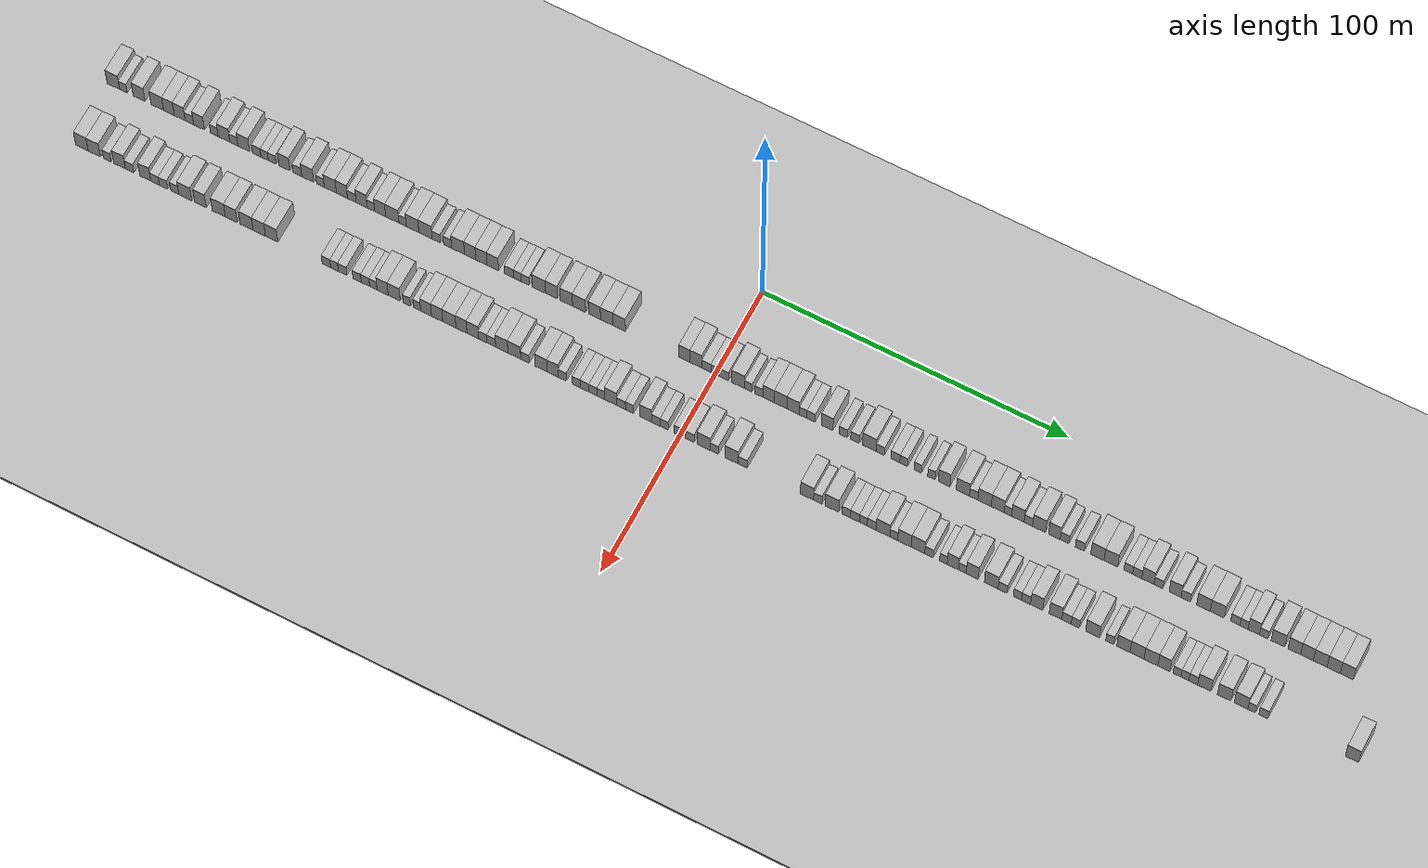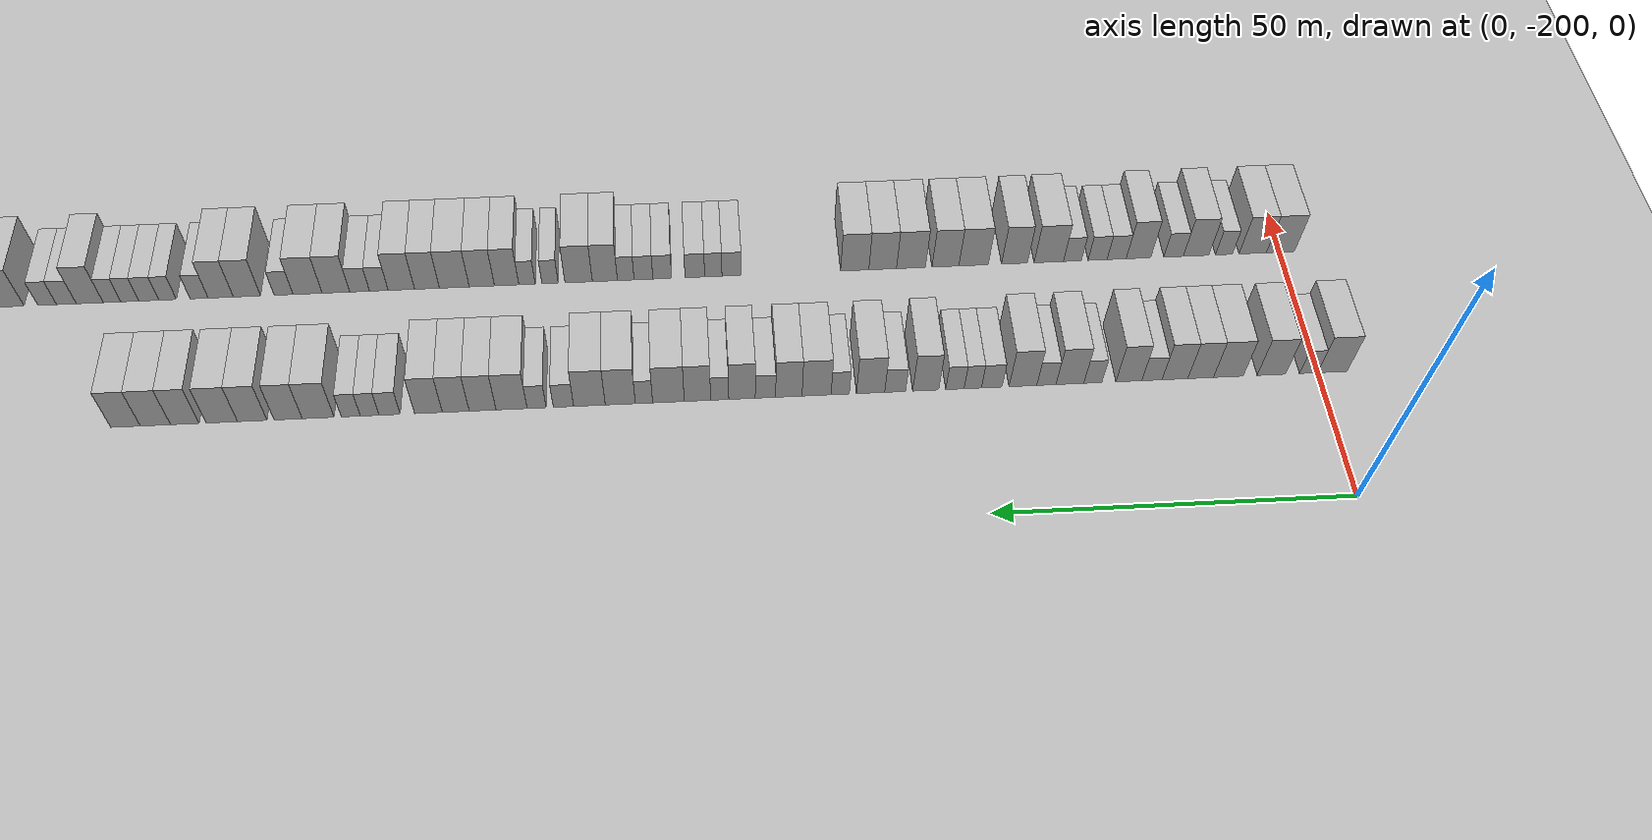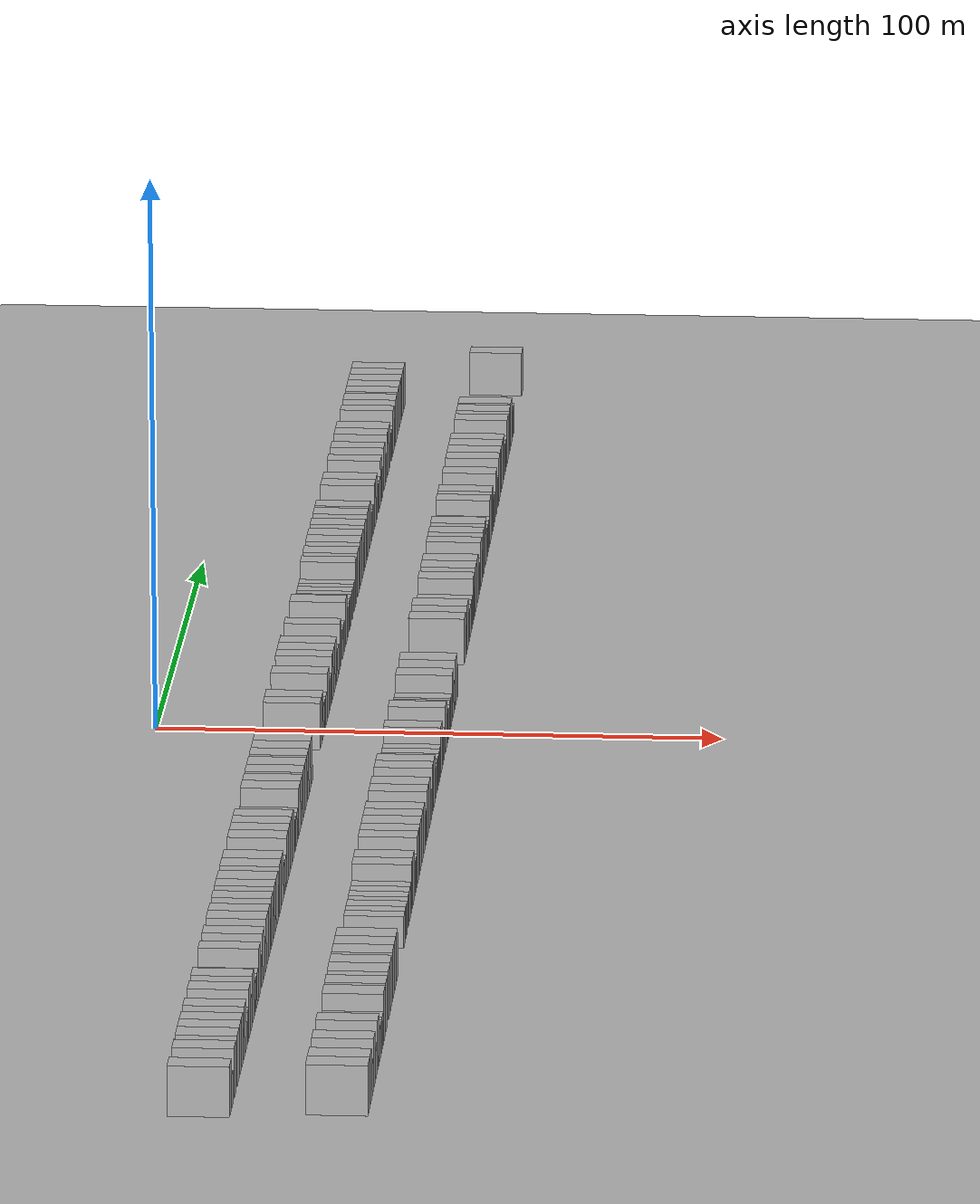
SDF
<?xml version="1.0" encoding="utf-8"?>

<sdf version="1.6">

   <world name="default">

      <gui fullscreen="0">

         <camera name="user_camera">

            <pose>-15 0 4.57585 0 0 0</pose>

            <view_controller>orbit</view_controller>

         </camera>

      </gui>

      <scene>

         <sky>

           <clouds>

             <speed>12</speed>

           </clouds>

         </sky>

         <ambient>0.4 0.4 0.4 1</ambient>

         <background>0.7 0.7 0.7 1</background>

         <shadows>1</shadows>

      </scene>

      <gravity>0 0 -9.8066</gravity>

      <magnetic_field>6e-06 2.3e-05 -4.2e-05</magnetic_field>

      <physics default="0" name="default_physics" type="ode">

         <ode>

            <solver>

               <type>quick</type>

               <iters>10</iters>

               <sor>1.0</sor>

               <use_dynamic_moi_rescaling>0</use_dynamic_moi_rescaling>

            </solver>

            <constraints>

               <cfm>0</cfm>

               <erp>0.2</erp>

               <contact_max_correcting_vel>100</contact_max_correcting_vel>

               <contact_surface_layer>0.001</contact_surface_layer>

            </constraints>

         </ode>

         <max_step_size>0.004</max_step_size>

         <real_time_factor>1</real_time_factor>

         <real_time_update_rate>250</real_time_update_rate>

      </physics>

      <light name="sun" type="directional">

         <cast_shadows>1</cast_shadows>

         <pose>0 0 10 0 0 0</pose>

         <diffuse>0.8 0.8 0.8 1</diffuse>

         <specular>0.2 0.2 0.2 1</specular>

         <attenuation>

            <range>1000</range>

            <constant>0.9</constant>

            <linear>0.01</linear>

            <quadratic>0.001</quadratic>

         </attenuation>

         <direction>-0.5 0.1 -0.9</direction>

      </light>

      <include>

         <name>ground_plane_1</name>

         <uri>model://HANNAS_ground_plane</uri>

         <pose>0 0 0  0 0 0</pose>

      </include>

      <include>

         <name>ground_plane_2</name>

         <uri>model://HANNAS_ground_plane</uri>

         <pose>100 0 0  0 0 0</pose>

      </include>

      <model name="building_1">

         <static>1</static>

         <pose frame="">25.0000 -201.8537 0 0.000000 0.000000 0.000000</pose>

         <link name="link">

            <pose frame="">0 0 4.50 0 0 0</pose>

            <collision name="collision">

               <geometry>

                  <box>

                     <size>10.0000 4.2926 9.0000</size>

                  </box>

               </geometry>

               <max_contacts>10</max_contacts>

               <surface>

                  <contact>

                     <ode/>

                  </contact>

                  <bounce/>

                  <friction>

                     <torsional>

                        <ode/>

                     </torsional>

                     <ode/>

                  </friction>

               </surface>

            </collision>

            <visual name="visual">

               <cast_shadows>0</cast_shadows>

               <geometry>

                  <box>

                     <size>10.0000 4.2926 9.0000</size>

                  </box>

               </geometry>

               <material>

                  <script>

                     <uri>model://HANNAS_wall/materials/scripts</uri>

                     <uri>model://HANNAS_wall/materials/textures</uri>

                     <name>vrc/HANNAS_wall</name>

                  </script>

               </material>

            </visual>

            <self_collide>0</self_collide>

            <enable_wind>0</enable_wind>

            <kinematic>0</kinematic>

         </link>

      </model>

      <model name="building_2">

         <static>1</static>

         <pose frame="">25.0000 -198.4065 0 0.000000 0.000000 0.000000</pose>

         <link name="link">

            <pose frame="">0 0 3.00 0 0 0</pose>

            <collision name="collision">

               <geometry>

                  <box>

                     <size>10.0000 2.6019 6.0000</size>

                  </box>

               </geometry>

               <max_contacts>10</max_contacts>

               <surface>

                  <contact>

                     <ode/>

                  </contact>

                  <bounce/>

                  <friction>

                     <torsional>

                        <ode/>

                     </torsional>

                     <ode/>

                  </friction>

               </surface>

            </collision>

            <visual name="visual">

               <cast_shadows>0</cast_shadows>

               <geometry>

                  <box>

                     <size>10.0000 2.6019 6.0000</size>

                  </box>

               </geometry>

               <material>

                  <script>

                     <uri>model://HANNAS_wall/materials/scripts</uri>

                     <uri>model://HANNAS_wall/materials/textures</uri>

                     <name>vrc/HANNAS_wall</name>

                  </script>

               </material>

            </visual>

            <self_collide>0</self_collide>

            <enable_wind>0</enable_wind>

            <kinematic>0</kinematic>

         </link>

      </model>

      <model name="building_3">

         <static>1</static>

         <pose frame="">25.0000 -193.0528 0 0.000000 0.000000 0.000000</pose>

         <link name="link">

            <pose frame="">0 0 4.50 0 0 0</pose>

            <collision name="collision">

               <geometry>

                  <box>

                     <size>10.0000 4.1055 9.0000</size>

                  </box>

               </geometry>

               <max_contacts>10</max_contacts>

               <surface>

                  <contact>

                     <ode/>

                  </contact>

                  <bounce/>

                  <friction>

                     <torsional>

                        <ode/>

                     </torsional>

                     <ode/>

                  </friction>

               </surface>

            </collision>

            <visual name="visual">

               <cast_shadows>0</cast_shadows>

               <geometry>

                  <box>

                     <size>10.0000 4.1055 9.0000</size>

                  </box>

               </geometry>

               <material>

                  <script>

                     <uri>model://HANNAS_wall/materials/scripts</uri>

                     <uri>model://HANNAS_wall/materials/textures</uri>

                     <name>vrc/HANNAS_wall</name>

                  </script>

               </material>

            </visual>

            <self_collide>0</self_collide>

            <enable_wind>0</enable_wind>

            <kinematic>0</kinematic>

         </link>

      </model>

      <model name="building_4">

         <static>1</static>

         <pose frame="">25.0000 -186.8608 0 0.000000 0.000000 0.000000</pose>

         <link name="link">

            <pose frame="">0 0 4.50 0 0 0</pose>

            <collision name="collision">

               <geometry>

                  <box>

                     <size>10.0000 4.2785 9.0000</size>

                  </box>

               </geometry>

               <max_contacts>10</max_contacts>

               <surface>

                  <contact>

                     <ode/>

                  </contact>

                  <bounce/>

                  <friction>

                     <torsional>

                        <ode/>

                     </torsional>

                     <ode/>

                  </friction>

               </surface>

            </collision>

            <visual name="visual">

               <cast_shadows>0</cast_shadows>

               <geometry>

                  <box>

                     <size>10.0000 4.2785 9.0000</size>

                  </box>

               </geometry>

               <material>

                  <script>

                     <uri>model://HANNAS_wall/materials/scripts</uri>

                     <uri>model://HANNAS_wall/materials/textures</uri>

                     <name>vrc/HANNAS_wall</name>

                  </script>

               </material>

            </visual>

            <self_collide>0</self_collide>

            <enable_wind>0</enable_wind>

            <kinematic>0</kinematic>

         </link>

      </model>

      <model name="building_5">

         <static>1</static>

         <pose frame="">25.0000 -182.8801 0 0.000000 0.000000 0.000000</pose>

         <link name="link">

            <pose frame="">0 0 4.50 0 0 0</pose>

            <collision name="collision">

               <geometry>

                  <box>

                     <size>10.0000 3.6829 9.0000</size>

                  </box>

               </geometry>

               <max_contacts>10</max_contacts>

               <surface>

                  <contact>

                     <ode/>

                  </contact>

                  <bounce/>

                  <friction>

                     <torsional>

                        <ode/>

                     </torsional>

                     <ode/>

                  </friction>

               </surface>

            </collision>

            <visual name="visual">

               <cast_shadows>0</cast_shadows>

               <geometry>

                  <box>

                     <size>10.0000 3.6829 9.0000</size>

                  </box>

               </geometry>

               <material>

                  <script>

                     <uri>model://HANNAS_wall/materials/scripts</uri>

                     <uri>model://HANNAS_wall/materials/textures</uri>

                     <name>vrc/HANNAS_wall</name>

                  </script>

               </material>

            </visual>

            <self_collide>0</self_collide>

            <enable_wind>0</enable_wind>

            <kinematic>0</kinematic>

         </link>

      </model>

      <model name="building_6">

         <static>1</static>

         <pose frame="">25.0000 -179.1842 0 0.000000 0.000000 0.000000</pose>

         <link name="link">

            <pose frame="">0 0 4.50 0 0 0</pose>

            <collision name="collision">

               <geometry>

                  <box>

                     <size>10.0000 3.7089 9.0000</size>

                  </box>

               </geometry>

               <max_contacts>10</max_contacts>

               <surface>

                  <contact>

                     <ode/>

                  </contact>

                  <bounce/>

                  <friction>

                     <torsional>

                        <ode/>

                     </torsional>

                     <ode/>

                  </friction>

               </surface>

            </collision>

            <visual name="visual">

               <cast_shadows>0</cast_shadows>

               <geometry>

                  <box>

                     <size>10.0000 3.7089 9.0000</size>

                  </box>

               </geometry>

               <material>

                  <script>

                     <uri>model://HANNAS_wall/materials/scripts</uri>

                     <uri>model://HANNAS_wall/materials/textures</uri>

                     <name>vrc/HANNAS_wall</name>

                  </script>

               </material>

            </visual>

            <self_collide>0</self_collide>

            <enable_wind>0</enable_wind>

            <kinematic>0</kinematic>

         </link>

      </model>

      <model name="building_7">

         <static>1</static>

         <pose frame="">25.0000 -175.8771 0 0.000000 0.000000 0.000000</pose>

         <link name="link">

            <pose frame="">0 0 3.00 0 0 0</pose>

            <collision name="collision">

               <geometry>

                  <box>

                     <size>10.0000 2.9053 6.0000</size>

                  </box>

               </geometry>

               <max_contacts>10</max_contacts>

               <surface>

                  <contact>

                     <ode/>

                  </contact>

                  <bounce/>

                  <friction>

                     <torsional>

                        <ode/>

                     </torsional>

                     <ode/>

                  </friction>

               </surface>

            </collision>

            <visual name="visual">

               <cast_shadows>0</cast_shadows>

               <geometry>

                  <box>

                     <size>10.0000 2.9053 6.0000</size>

                  </box>

               </geometry>

               <material>

                  <script>

                     <uri>model://HANNAS_wall/materials/scripts</uri>

                     <uri>model://HANNAS_wall/materials/textures</uri>

                     <name>vrc/HANNAS_wall</name>

                  </script>

               </material>

            </visual>

            <self_collide>0</self_collide>

            <enable_wind>0</enable_wind>

            <kinematic>0</kinematic>

         </link>

      </model>

      <model name="building_8">

         <static>1</static>

         <pose frame="">25.0000 -172.5661 0 0.000000 0.000000 0.000000</pose>

         <link name="link">

            <pose frame="">0 0 4.50 0 0 0</pose>

            <collision name="collision">

               <geometry>

                  <box>

                     <size>10.0000 3.7166 9.0000</size>

                  </box>

               </geometry>

               <max_contacts>10</max_contacts>

               <surface>

                  <contact>

                     <ode/>

                  </contact>

                  <bounce/>

                  <friction>

                     <torsional>

                        <ode/>

                     </torsional>

                     <ode/>

                  </friction>

               </surface>

            </collision>

            <visual name="visual">

               <cast_shadows>0</cast_shadows>

               <geometry>

                  <box>

                     <size>10.0000 3.7166 9.0000</size>

                  </box>

               </geometry>

               <material>

                  <script>

                     <uri>model://HANNAS_wall/materials/scripts</uri>

                     <uri>model://HANNAS_wall/materials/textures</uri>

                     <name>vrc/HANNAS_wall</name>

                  </script>

               </material>

            </visual>

            <self_collide>0</self_collide>

            <enable_wind>0</enable_wind>

            <kinematic>0</kinematic>

         </link>

      </model>

      <model name="building_9">

         <static>1</static>

         <pose frame="">25.0000 -167.4153 0 0.000000 0.000000 0.000000</pose>

         <link name="link">

            <pose frame="">0 0 3.00 0 0 0</pose>

            <collision name="collision">

               <geometry>

                  <box>

                     <size>10.0000 2.5850 6.0000</size>

                  </box>

               </geometry>

               <max_contacts>10</max_contacts>

               <surface>

                  <contact>

                     <ode/>

                  </contact>

                  <bounce/>

                  <friction>

                     <torsional>

                        <ode/>

                     </torsional>

                     <ode/>

                  </friction>

               </surface>

            </collision>

            <visual name="visual">

               <cast_shadows>0</cast_shadows>

               <geometry>

                  <box>

                     <size>10.0000 2.5850 6.0000</size>

                  </box>

               </geometry>

               <material>

                  <script>

                     <uri>model://HANNAS_wall/materials/scripts</uri>

                     <uri>model://HANNAS_wall/materials/textures</uri>

                     <name>vrc/HANNAS_wall</name>

                  </script>

               </material>

            </visual>

            <self_collide>0</self_collide>

            <enable_wind>0</enable_wind>

            <kinematic>0</kinematic>

         </link>

      </model>

      <model name="building_10">

         <static>1</static>

         <pose frame="">25.0000 -164.1304 0 0.000000 0.000000 0.000000</pose>

         <link name="link">

            <pose frame="">0 0 4.50 0 0 0</pose>

            <collision name="collision">

               <geometry>

                  <box>

                     <size>10.0000 3.9848 9.0000</size>

                  </box>

               </geometry>

               <max_contacts>10</max_contacts>

               <surface>

                  <contact>

                     <ode/>

                  </contact>

                  <bounce/>

                  <friction>

                     <torsional>

                        <ode/>

                     </torsional>

                     <ode/>

                  </friction>

               </surface>

            </collision>

            <visual name="visual">

               <cast_shadows>0</cast_shadows>

               <geometry>

                  <box>

                     <size>10.0000 3.9848 9.0000</size>

                  </box>

               </geometry>

               <material>

                  <script>

                     <uri>model://HANNAS_wall/materials/scripts</uri>

                     <uri>model://HANNAS_wall/materials/textures</uri>

                     <name>vrc/HANNAS_wall</name>

                  </script>

               </material>

            </visual>

            <self_collide>0</self_collide>

            <enable_wind>0</enable_wind>

            <kinematic>0</kinematic>

         </link>

      </model>

      <model name="building_11">

         <static>1</static>

         <pose frame="">25.0000 -160.7675 0 0.000000 0.000000 0.000000</pose>

         <link name="link">

            <pose frame="">0 0 3.00 0 0 0</pose>

            <collision name="collision">

               <geometry>

                  <box>

                     <size>10.0000 2.7411 6.0000</size>

                  </box>

               </geometry>

               <max_contacts>10</max_contacts>

               <surface>

                  <contact>

                     <ode/>

                  </contact>

                  <bounce/>

                  <friction>

                     <torsional>

                        <ode/>

                     </torsional>

                     <ode/>

                  </friction>

               </surface>

            </collision>

            <visual name="visual">

               <cast_shadows>0</cast_shadows>

               <geometry>

                  <box>

                     <size>10.0000 2.7411 6.0000</size>

                  </box>

               </geometry>

               <material>

                  <script>

                     <uri>model://HANNAS_wall/materials/scripts</uri>

                     <uri>model://HANNAS_wall/materials/textures</uri>

                     <name>vrc/HANNAS_wall</name>

                  </script>

               </material>

            </visual>

            <self_collide>0</self_collide>

            <enable_wind>0</enable_wind>

            <kinematic>0</kinematic>

         </link>

      </model>

      <model name="building_12">

         <static>1</static>

         <pose frame="">25.0000 -157.4138 0 0.000000 0.000000 0.000000</pose>

         <link name="link">

            <pose frame="">0 0 4.50 0 0 0</pose>

            <collision name="collision">

               <geometry>

                  <box>

                     <size>10.0000 3.9663 9.0000</size>

                  </box>

               </geometry>

               <max_contacts>10</max_contacts>

               <surface>

                  <contact>

                     <ode/>

                  </contact>

                  <bounce/>

                  <friction>

                     <torsional>

                        <ode/>

                     </torsional>

                     <ode/>

                  </friction>

               </surface>

            </collision>

            <visual name="visual">

               <cast_shadows>0</cast_shadows>

               <geometry>

                  <box>

                     <size>10.0000 3.9663 9.0000</size>

                  </box>

               </geometry>

               <material>

                  <script>

                     <uri>model://HANNAS_wall/materials/scripts</uri>

                     <uri>model://HANNAS_wall/materials/textures</uri>

                     <name>vrc/HANNAS_wall</name>

                  </script>

               </material>

            </visual>

            <self_collide>0</self_collide>

            <enable_wind>0</enable_wind>

            <kinematic>0</kinematic>

         </link>

      </model>

      <model name="building_13">

         <static>1</static>

         <pose frame="">25.0000 -152.9617 0 0.000000 0.000000 0.000000</pose>

         <link name="link">

            <pose frame="">0 0 3.00 0 0 0</pose>

            <collision name="collision">

               <geometry>

                  <box>

                     <size>10.0000 2.9379 6.0000</size>

                  </box>

               </geometry>

               <max_contacts>10</max_contacts>

               <surface>

                  <contact>

                     <ode/>

                  </contact>

                  <bounce/>

                  <friction>

                     <torsional>

                        <ode/>

                     </torsional>

                     <ode/>

                  </friction>

               </surface>

            </collision>

            <visual name="visual">

               <cast_shadows>0</cast_shadows>

               <geometry>

                  <box>

                     <size>10.0000 2.9379 6.0000</size>

                  </box>

               </geometry>

               <material>

                  <script>

                     <uri>model://HANNAS_wall/materials/scripts</uri>

                     <uri>model://HANNAS_wall/materials/textures</uri>

                     <name>vrc/HANNAS_wall</name>

                  </script>

               </material>

            </visual>

            <self_collide>0</self_collide>

            <enable_wind>0</enable_wind>

            <kinematic>0</kinematic>

         </link>

      </model>

      <model name="building_14">

         <static>1</static>

         <pose frame="">25.0000 -150.2623 0 0.000000 0.000000 0.000000</pose>

         <link name="link">

            <pose frame="">0 0 3.00 0 0 0</pose>

            <collision name="collision">

               <geometry>

                  <box>

                     <size>10.0000 2.4608 6.0000</size>

                  </box>

               </geometry>

               <max_contacts>10</max_contacts>

               <surface>

                  <contact>

                     <ode/>

                  </contact>

                  <bounce/>

                  <friction>

                     <torsional>

                        <ode/>

                     </torsional>

                     <ode/>

                  </friction>

               </surface>

            </collision>

            <visual name="visual">

               <cast_shadows>0</cast_shadows>

               <geometry>

                  <box>

                     <size>10.0000 2.4608 6.0000</size>

                  </box>

               </geometry>

               <material>

                  <script>

                     <uri>model://HANNAS_wall/materials/scripts</uri>

                     <uri>model://HANNAS_wall/materials/textures</uri>

                     <name>vrc/HANNAS_wall</name>

                  </script>

               </material>

            </visual>

            <self_collide>0</self_collide>

            <enable_wind>0</enable_wind>

            <kinematic>0</kinematic>

         </link>

      </model>

      <model name="building_15">

         <static>1</static>

         <pose frame="">25.0000 -147.7212 0 0.000000 0.000000 0.000000</pose>

         <link name="link">

            <pose frame="">0 0 3.00 0 0 0</pose>

            <collision name="collision">

               <geometry>

                  <box>

                     <size>10.0000 2.6214 6.0000</size>

                  </box>

               </geometry>

               <max_contacts>10</max_contacts>

               <surface>

                  <contact>

                     <ode/>

                  </contact>

                  <bounce/>

                  <friction>

                     <torsional>

                        <ode/>

                     </torsional>

                     <ode/>

                  </friction>

               </surface>

            </collision>

            <visual name="visual">

               <cast_shadows>0</cast_shadows>

               <geometry>

                  <box>

                     <size>10.0000 2.6214 6.0000</size>

                  </box>

               </geometry>

               <material>

                  <script>

                     <uri>model://HANNAS_wall/materials/scripts</uri>

                     <uri>model://HANNAS_wall/materials/textures</uri>

                     <name>vrc/HANNAS_wall</name>

                  </script>

               </material>

            </visual>

            <self_collide>0</self_collide>

            <enable_wind>0</enable_wind>

            <kinematic>0</kinematic>

         </link>

      </model>

      <model name="building_16">

         <static>1</static>

         <pose frame="">25.0000 -143.5604 0 0.000000 0.000000 0.000000</pose>

         <link name="link">

            <pose frame="">0 0 4.50 0 0 0</pose>

            <collision name="collision">

               <geometry>

                  <box>

                     <size>10.0000 3.7002 9.0000</size>

                  </box>

               </geometry>

               <max_contacts>10</max_contacts>

               <surface>

                  <contact>

                     <ode/>

                  </contact>

                  <bounce/>

                  <friction>

                     <torsional>

                        <ode/>

                     </torsional>

                     <ode/>

                  </friction>

               </surface>

            </collision>

            <visual name="visual">

               <cast_shadows>0</cast_shadows>

               <geometry>

                  <box>

                     <size>10.0000 3.7002 9.0000</size>

                  </box>

               </geometry>

               <material>

                  <script>

                     <uri>model://HANNAS_wall/materials/scripts</uri>

                     <uri>model://HANNAS_wall/materials/textures</uri>

                     <name>vrc/HANNAS_wall</name>

                  </script>

               </material>

            </visual>

            <self_collide>0</self_collide>

            <enable_wind>0</enable_wind>

            <kinematic>0</kinematic>

         </link>

      </model>

      <model name="building_17">

         <static>1</static>

         <pose frame="">25.0000 -139.2249 0 0.000000 0.000000 0.000000</pose>

         <link name="link">

            <pose frame="">0 0 3.00 0 0 0</pose>

            <collision name="collision">

               <geometry>

                  <box>

                     <size>10.0000 2.9709 6.0000</size>

                  </box>

               </geometry>

               <max_contacts>10</max_contacts>

               <surface>

                  <contact>

                     <ode/>

                  </contact>

                  <bounce/>

                  <friction>

                     <torsional>

                        <ode/>

                     </torsional>

                     <ode/>

                  </friction>

               </surface>

            </collision>

            <visual name="visual">

               <cast_shadows>0</cast_shadows>

               <geometry>

                  <box>

                     <size>10.0000 2.9709 6.0000</size>

                  </box>

               </geometry>

               <material>

                  <script>

                     <uri>model://HANNAS_wall/materials/scripts</uri>

                     <uri>model://HANNAS_wall/materials/textures</uri>

                     <name>vrc/HANNAS_wall</name>

                  </script>

               </material>

            </visual>

            <self_collide>0</self_collide>

            <enable_wind>0</enable_wind>

            <kinematic>0</kinematic>

         </link>

      </model>

      <model name="building_18">

         <static>1</static>

         <pose frame="">25.0000 -135.7327 0 0.000000 0.000000 0.000000</pose>

         <link name="link">

            <pose frame="">0 0 4.50 0 0 0</pose>

            <collision name="collision">

               <geometry>

                  <box>

                     <size>10.0000 4.0134 9.0000</size>

                  </box>

               </geometry>

               <max_contacts>10</max_contacts>

               <surface>

                  <contact>

                     <ode/>

                  </contact>

                  <bounce/>

                  <friction>

                     <torsional>

                        <ode/>

                     </torsional>

                     <ode/>

                  </friction>

               </surface>

            </collision>

            <visual name="visual">

               <cast_shadows>0</cast_shadows>

               <geometry>

                  <box>

                     <size>10.0000 4.0134 9.0000</size>

                  </box>

               </geometry>

               <material>

                  <script>

                     <uri>model://HANNAS_wall/materials/scripts</uri>

                     <uri>model://HANNAS_wall/materials/textures</uri>

                     <name>vrc/HANNAS_wall</name>

                  </script>

               </material>

            </visual>

            <self_collide>0</self_collide>

            <enable_wind>0</enable_wind>

            <kinematic>0</kinematic>

         </link>

      </model>

      <model name="building_19">

         <static>1</static>

         <pose frame="">25.0000 -131.4297 0 0.000000 0.000000 0.000000</pose>

         <link name="link">

            <pose frame="">0 0 3.00 0 0 0</pose>

            <collision name="collision">

               <geometry>

                  <box>

                     <size>10.0000 2.5926 6.0000</size>

                  </box>

               </geometry>

               <max_contacts>10</max_contacts>

               <surface>

                  <contact>

                     <ode/>

                  </contact>

                  <bounce/>

                  <friction>

                     <torsional>

                        <ode/>

                     </torsional>

                     <ode/>

                  </friction>

               </surface>

            </collision>

            <visual name="visual">

               <cast_shadows>0</cast_shadows>

               <geometry>

                  <box>

                     <size>10.0000 2.5926 6.0000</size>

                  </box>

               </geometry>

               <material>

                  <script>

                     <uri>model://HANNAS_wall/materials/scripts</uri>

                     <uri>model://HANNAS_wall/materials/textures</uri>

                     <name>vrc/HANNAS_wall</name>

                  </script>

               </material>

            </visual>

            <self_collide>0</self_collide>

            <enable_wind>0</enable_wind>

            <kinematic>0</kinematic>

         </link>

      </model>

      <model name="building_20">

         <static>1</static>

         <pose frame="">25.0000 -128.0775 0 0.000000 0.000000 0.000000</pose>

         <link name="link">

            <pose frame="">0 0 4.50 0 0 0</pose>

            <collision name="collision">

               <geometry>

                  <box>

                     <size>10.0000 4.1117 9.0000</size>

                  </box>

               </geometry>

               <max_contacts>10</max_contacts>

               <surface>

                  <contact>

                     <ode/>

                  </contact>

                  <bounce/>

                  <friction>

                     <torsional>

                        <ode/>

                     </torsional>

                     <ode/>

                  </friction>

               </surface>

            </collision>

            <visual name="visual">

               <cast_shadows>0</cast_shadows>

               <geometry>

                  <box>

                     <size>10.0000 4.1117 9.0000</size>

                  </box>

               </geometry>

               <material>

                  <script>

                     <uri>model://HANNAS_wall/materials/scripts</uri>

                     <uri>model://HANNAS_wall/materials/textures</uri>

                     <name>vrc/HANNAS_wall</name>

                  </script>

               </material>

            </visual>

            <self_collide>0</self_collide>

            <enable_wind>0</enable_wind>

            <kinematic>0</kinematic>

         </link>

      </model>

      <model name="building_21">

         <static>1</static>

         <pose frame="">25.0000 -124.1487 0 0.000000 0.000000 0.000000</pose>

         <link name="link">

            <pose frame="">0 0 4.50 0 0 0</pose>

            <collision name="collision">

               <geometry>

                  <box>

                     <size>10.0000 3.7458 9.0000</size>

                  </box>

               </geometry>

               <max_contacts>10</max_contacts>

               <surface>

                  <contact>

                     <ode/>

                  </contact>

                  <bounce/>

                  <friction>

                     <torsional>

                        <ode/>

                     </torsional>

                     <ode/>

                  </friction>

               </surface>

            </collision>

            <visual name="visual">

               <cast_shadows>0</cast_shadows>

               <geometry>

                  <box>

                     <size>10.0000 3.7458 9.0000</size>

                  </box>

               </geometry>

               <material>

                  <script>

                     <uri>model://HANNAS_wall/materials/scripts</uri>

                     <uri>model://HANNAS_wall/materials/textures</uri>

                     <name>vrc/HANNAS_wall</name>

                  </script>

               </material>

            </visual>

            <self_collide>0</self_collide>

            <enable_wind>0</enable_wind>

            <kinematic>0</kinematic>

         </link>

      </model>

      <model name="building_22">

         <static>1</static>

         <pose frame="">25.0000 -120.8417 0 0.000000 0.000000 0.000000</pose>

         <link name="link">

            <pose frame="">0 0 3.00 0 0 0</pose>

            <collision name="collision">

               <geometry>

                  <box>

                     <size>10.0000 2.8683 6.0000</size>

                  </box>

               </geometry>

               <max_contacts>10</max_contacts>

               <surface>

                  <contact>

                     <ode/>

                  </contact>

                  <bounce/>

                  <friction>

                     <torsional>

                        <ode/>

                     </torsional>

                     <ode/>

                  </friction>

               </surface>

            </collision>

            <visual name="visual">

               <cast_shadows>0</cast_shadows>

               <geometry>

                  <box>

                     <size>10.0000 2.8683 6.0000</size>

                  </box>

               </geometry>

               <material>

                  <script>

                     <uri>model://HANNAS_wall/materials/scripts</uri>

                     <uri>model://HANNAS_wall/materials/textures</uri>

                     <name>vrc/HANNAS_wall</name>

                  </script>

               </material>

            </visual>

            <self_collide>0</self_collide>

            <enable_wind>0</enable_wind>

            <kinematic>0</kinematic>

         </link>

      </model>

      <model name="building_23">

         <static>1</static>

         <pose frame="">25.0000 -117.5402 0 0.000000 0.000000 0.000000</pose>

         <link name="link">

            <pose frame="">0 0 4.50 0 0 0</pose>

            <collision name="collision">

               <geometry>

                  <box>

                     <size>10.0000 3.7347 9.0000</size>

                  </box>

               </geometry>

               <max_contacts>10</max_contacts>

               <surface>

                  <contact>

                     <ode/>

                  </contact>

                  <bounce/>

                  <friction>

                     <torsional>

                        <ode/>

                     </torsional>

                     <ode/>

                  </friction>

               </surface>

            </collision>

            <visual name="visual">

               <cast_shadows>0</cast_shadows>

               <geometry>

                  <box>

                     <size>10.0000 3.7347 9.0000</size>

                  </box>

               </geometry>

               <material>

                  <script>

                     <uri>model://HANNAS_wall/materials/scripts</uri>

                     <uri>model://HANNAS_wall/materials/textures</uri>

                     <name>vrc/HANNAS_wall</name>

                  </script>

               </material>

            </visual>

            <self_collide>0</self_collide>

            <enable_wind>0</enable_wind>

            <kinematic>0</kinematic>

         </link>

      </model>

      <model name="building_24">

         <static>1</static>

         <pose frame="">25.0000 -114.3938 0 0.000000 0.000000 0.000000</pose>

         <link name="link">

            <pose frame="">0 0 3.00 0 0 0</pose>

            <collision name="collision">

               <geometry>

                  <box>

                     <size>10.0000 2.5581 6.0000</size>

                  </box>

               </geometry>

               <max_contacts>10</max_contacts>

               <surface>

                  <contact>

                     <ode/>

                  </contact>

                  <bounce/>

                  <friction>

                     <torsional>

                        <ode/>

                     </torsional>

                     <ode/>

                  </friction>

               </surface>

            </collision>

            <visual name="visual">

               <cast_shadows>0</cast_shadows>

               <geometry>

                  <box>

                     <size>10.0000 2.5581 6.0000</size>

                  </box>

               </geometry>

               <material>

                  <script>

                     <uri>model://HANNAS_wall/materials/scripts</uri>

                     <uri>model://HANNAS_wall/materials/textures</uri>

                     <name>vrc/HANNAS_wall</name>

                  </script>

               </material>

            </visual>

            <self_collide>0</self_collide>

            <enable_wind>0</enable_wind>

            <kinematic>0</kinematic>

         </link>

      </model>

      <model name="building_25">

         <static>1</static>

         <pose frame="">25.0000 -111.2595 0 0.000000 0.000000 0.000000</pose>

         <link name="link">

            <pose frame="">0 0 4.50 0 0 0</pose>

            <collision name="collision">

               <geometry>

                  <box>

                     <size>10.0000 3.7104 9.0000</size>

                  </box>

               </geometry>

               <max_contacts>10</max_contacts>

               <surface>

                  <contact>

                     <ode/>

                  </contact>

                  <bounce/>

                  <friction>

                     <torsional>

                        <ode/>

                     </torsional>

                     <ode/>

                  </friction>

               </surface>

            </collision>

            <visual name="visual">

               <cast_shadows>0</cast_shadows>

               <geometry>

                  <box>

                     <size>10.0000 3.7104 9.0000</size>

                  </box>

               </geometry>

               <material>

                  <script>

                     <uri>model://HANNAS_wall/materials/scripts</uri>

                     <uri>model://HANNAS_wall/materials/textures</uri>

                     <name>vrc/HANNAS_wall</name>

                  </script>

               </material>

            </visual>

            <self_collide>0</self_collide>

            <enable_wind>0</enable_wind>

            <kinematic>0</kinematic>

         </link>

      </model>

      <model name="building_26">

         <static>1</static>

         <pose frame="">25.0000 -107.1808 0 0.000000 0.000000 0.000000</pose>

         <link name="link">

            <pose frame="">0 0 4.50 0 0 0</pose>

            <collision name="collision">

               <geometry>

                  <box>

                     <size>10.0000 4.4472 9.0000</size>

                  </box>

               </geometry>

               <max_contacts>10</max_contacts>

               <surface>

                  <contact>

                     <ode/>

                  </contact>

                  <bounce/>

                  <friction>

                     <torsional>

                        <ode/>

                     </torsional>

                     <ode/>

                  </friction>

               </surface>

            </collision>

            <visual name="visual">

               <cast_shadows>0</cast_shadows>

               <geometry>

                  <box>

                     <size>10.0000 4.4472 9.0000</size>

                  </box>

               </geometry>

               <material>

                  <script>

                     <uri>model://HANNAS_wall/materials/scripts</uri>

                     <uri>model://HANNAS_wall/materials/textures</uri>

                     <name>vrc/HANNAS_wall</name>

                  </script>

               </material>

            </visual>

            <self_collide>0</self_collide>

            <enable_wind>0</enable_wind>

            <kinematic>0</kinematic>

         </link>

      </model>

      <model name="building_27">

         <static>1</static>

         <pose frame="">25.0000 -103.7387 0 0.000000 0.000000 0.000000</pose>

         <link name="link">

            <pose frame="">0 0 3.00 0 0 0</pose>

            <collision name="collision">

               <geometry>

                  <box>

                     <size>10.0000 2.4370 6.0000</size>

                  </box>

               </geometry>

               <max_contacts>10</max_contacts>

               <surface>

                  <contact>

                     <ode/>

                  </contact>

                  <bounce/>

                  <friction>

                     <torsional>

                        <ode/>

                     </torsional>

                     <ode/>

                  </friction>

               </surface>

            </collision>

            <visual name="visual">

               <cast_shadows>0</cast_shadows>

               <geometry>

                  <box>

                     <size>10.0000 2.4370 6.0000</size>

                  </box>

               </geometry>

               <material>

                  <script>

                     <uri>model://HANNAS_wall/materials/scripts</uri>

                     <uri>model://HANNAS_wall/materials/textures</uri>

                     <name>vrc/HANNAS_wall</name>

                  </script>

               </material>

            </visual>

            <self_collide>0</self_collide>

            <enable_wind>0</enable_wind>

            <kinematic>0</kinematic>

         </link>

      </model>

      <model name="building_28">

         <static>1</static>

         <pose frame="">25.0000 -100.4080 0 0.000000 0.000000 0.000000</pose>

         <link name="link">

            <pose frame="">0 0 4.50 0 0 0</pose>

            <collision name="collision">

               <geometry>

                  <box>

                     <size>10.0000 4.2245 9.0000</size>

                  </box>

               </geometry>

               <max_contacts>10</max_contacts>

               <surface>

                  <contact>

                     <ode/>

                  </contact>

                  <bounce/>

                  <friction>

                     <torsional>

                        <ode/>

                     </torsional>

                     <ode/>

                  </friction>

               </surface>

            </collision>

            <visual name="visual">

               <cast_shadows>0</cast_shadows>

               <geometry>

                  <box>

                     <size>10.0000 4.2245 9.0000</size>

                  </box>

               </geometry>

               <material>

                  <script>

                     <uri>model://HANNAS_wall/materials/scripts</uri>

                     <uri>model://HANNAS_wall/materials/textures</uri>

                     <name>vrc/HANNAS_wall</name>

                  </script>

               </material>

            </visual>

            <self_collide>0</self_collide>

            <enable_wind>0</enable_wind>

            <kinematic>0</kinematic>

         </link>

      </model>

      <model name="building_29">

         <static>1</static>

         <pose frame="">25.0000 -96.0797 0 0.000000 0.000000 0.000000</pose>

         <link name="link">

            <pose frame="">0 0 4.50 0 0 0</pose>

            <collision name="collision">

               <geometry>

                  <box>

                     <size>10.0000 4.4322 9.0000</size>

                  </box>

               </geometry>

               <max_contacts>10</max_contacts>

               <surface>

                  <contact>

                     <ode/>

                  </contact>

                  <bounce/>

                  <friction>

                     <torsional>

                        <ode/>

                     </torsional>

                     <ode/>

                  </friction>

               </surface>

            </collision>

            <visual name="visual">

               <cast_shadows>0</cast_shadows>

               <geometry>

                  <box>

                     <size>10.0000 4.4322 9.0000</size>

                  </box>

               </geometry>

               <material>

                  <script>

                     <uri>model://HANNAS_wall/materials/scripts</uri>

                     <uri>model://HANNAS_wall/materials/textures</uri>

                     <name>vrc/HANNAS_wall</name>

                  </script>

               </material>

            </visual>

            <self_collide>0</self_collide>

            <enable_wind>0</enable_wind>

            <kinematic>0</kinematic>

         </link>

      </model>

      <model name="building_30">

         <static>1</static>

         <pose frame="">25.0000 -92.4406 0 0.000000 0.000000 0.000000</pose>

         <link name="link">

            <pose frame="">0 0 3.00 0 0 0</pose>

            <collision name="collision">

               <geometry>

                  <box>

                     <size>10.0000 2.8461 6.0000</size>

                  </box>

               </geometry>

               <max_contacts>10</max_contacts>

               <surface>

                  <contact>

                     <ode/>

                  </contact>

                  <bounce/>

                  <friction>

                     <torsional>

                        <ode/>

                     </torsional>

                     <ode/>

                  </friction>

               </surface>

            </collision>

            <visual name="visual">

               <cast_shadows>0</cast_shadows>

               <geometry>

                  <box>

                     <size>10.0000 2.8461 6.0000</size>

                  </box>

               </geometry>

               <material>

                  <script>

                     <uri>model://HANNAS_wall/materials/scripts</uri>

                     <uri>model://HANNAS_wall/materials/textures</uri>

                     <name>vrc/HANNAS_wall</name>

                  </script>

               </material>

            </visual>

            <self_collide>0</self_collide>

            <enable_wind>0</enable_wind>

            <kinematic>0</kinematic>

         </link>

      </model>

      <model name="building_31">

         <static>1</static>

         <pose frame="">25.0000 -88.6851 0 0.000000 0.000000 0.000000</pose>

         <link name="link">

            <pose frame="">0 0 3.00 0 0 0</pose>

            <collision name="collision">

               <geometry>

                  <box>

                     <size>10.0000 2.6649 6.0000</size>

                  </box>

               </geometry>

               <max_contacts>10</max_contacts>

               <surface>

                  <contact>

                     <ode/>

                  </contact>

                  <bounce/>

                  <friction>

                     <torsional>

                        <ode/>

                     </torsional>

                     <ode/>

                  </friction>

               </surface>

            </collision>

            <visual name="visual">

               <cast_shadows>0</cast_shadows>

               <geometry>

                  <box>

                     <size>10.0000 2.6649 6.0000</size>

                  </box>

               </geometry>

               <material>

                  <script>

                     <uri>model://HANNAS_wall/materials/scripts</uri>

                     <uri>model://HANNAS_wall/materials/textures</uri>

                     <name>vrc/HANNAS_wall</name>

                  </script>

               </material>

            </visual>

            <self_collide>0</self_collide>

            <enable_wind>0</enable_wind>

            <kinematic>0</kinematic>

         </link>

      </model>

      <model name="building_32">

         <static>1</static>

         <pose frame="">25.0000 -85.1751 0 0.000000 0.000000 0.000000</pose>

         <link name="link">

            <pose frame="">0 0 4.50 0 0 0</pose>

            <collision name="collision">

               <geometry>

                  <box>

                     <size>10.0000 4.3550 9.0000</size>

                  </box>

               </geometry>

               <max_contacts>10</max_contacts>

               <surface>

                  <contact>

                     <ode/>

                  </contact>

                  <bounce/>

                  <friction>

                     <torsional>

                        <ode/>

                     </torsional>

                     <ode/>

                  </friction>

               </surface>

            </collision>

            <visual name="visual">

               <cast_shadows>0</cast_shadows>

               <geometry>

                  <box>

                     <size>10.0000 4.3550 9.0000</size>

                  </box>

               </geometry>

               <material>

                  <script>

                     <uri>model://HANNAS_wall/materials/scripts</uri>

                     <uri>model://HANNAS_wall/materials/textures</uri>

                     <name>vrc/HANNAS_wall</name>

                  </script>

               </material>

            </visual>

            <self_collide>0</self_collide>

            <enable_wind>0</enable_wind>

            <kinematic>0</kinematic>

         </link>

      </model>

      <model name="building_33">

         <static>1</static>

         <pose frame="">25.0000 -81.1255 0 0.000000 0.000000 0.000000</pose>

         <link name="link">

            <pose frame="">0 0 4.50 0 0 0</pose>

            <collision name="collision">

               <geometry>

                  <box>

                     <size>10.0000 3.7442 9.0000</size>

                  </box>

               </geometry>

               <max_contacts>10</max_contacts>

               <surface>

                  <contact>

                     <ode/>

                  </contact>

                  <bounce/>

                  <friction>

                     <torsional>

                        <ode/>

                     </torsional>

                     <ode/>

                  </friction>

               </surface>

            </collision>

            <visual name="visual">

               <cast_shadows>0</cast_shadows>

               <geometry>

                  <box>

                     <size>10.0000 3.7442 9.0000</size>

                  </box>

               </geometry>

               <material>

                  <script>

                     <uri>model://HANNAS_wall/materials/scripts</uri>

                     <uri>model://HANNAS_wall/materials/textures</uri>

                     <name>vrc/HANNAS_wall</name>

                  </script>

               </material>

            </visual>

            <self_collide>0</self_collide>

            <enable_wind>0</enable_wind>

            <kinematic>0</kinematic>

         </link>

      </model>

      <model name="building_34">

         <static>1</static>

         <pose frame="">25.0000 -77.3756 0 0.000000 0.000000 0.000000</pose>

         <link name="link">

            <pose frame="">0 0 4.50 0 0 0</pose>

            <collision name="collision">

               <geometry>

                  <box>

                     <size>10.0000 3.7556 9.0000</size>

                  </box>

               </geometry>

               <max_contacts>10</max_contacts>

               <surface>

                  <contact>

                     <ode/>

                  </contact>

                  <bounce/>

                  <friction>

                     <torsional>

                        <ode/>

                     </torsional>

                     <ode/>

                  </friction>

               </surface>

            </collision>

            <visual name="visual">

               <cast_shadows>0</cast_shadows>

               <geometry>

                  <box>

                     <size>10.0000 3.7556 9.0000</size>

                  </box>

               </geometry>

               <material>

                  <script>

                     <uri>model://HANNAS_wall/materials/scripts</uri>

                     <uri>model://HANNAS_wall/materials/textures</uri>

                     <name>vrc/HANNAS_wall</name>

                  </script>

               </material>

            </visual>

            <self_collide>0</self_collide>

            <enable_wind>0</enable_wind>

            <kinematic>0</kinematic>

         </link>

      </model>

      <model name="building_35">

         <static>1</static>

         <pose frame="">25.0000 -73.5626 0 0.000000 0.000000 0.000000</pose>

         <link name="link">

            <pose frame="">0 0 4.50 0 0 0</pose>

            <collision name="collision">

               <geometry>

                  <box>

                     <size>10.0000 3.8703 9.0000</size>

                  </box>

               </geometry>

               <max_contacts>10</max_contacts>

               <surface>

                  <contact>

                     <ode/>

                  </contact>

                  <bounce/>

                  <friction>

                     <torsional>

                        <ode/>

                     </torsional>

                     <ode/>

                  </friction>

               </surface>

            </collision>

            <visual name="visual">

               <cast_shadows>0</cast_shadows>

               <geometry>

                  <box>

                     <size>10.0000 3.8703 9.0000</size>

                  </box>

               </geometry>

               <material>

                  <script>

                     <uri>model://HANNAS_wall/materials/scripts</uri>

                     <uri>model://HANNAS_wall/materials/textures</uri>

                     <name>vrc/HANNAS_wall</name>

                  </script>

               </material>

            </visual>

            <self_collide>0</self_collide>

            <enable_wind>0</enable_wind>

            <kinematic>0</kinematic>

         </link>

      </model>

      <model name="building_36">

         <static>1</static>

         <pose frame="">25.0000 -68.1511 0 0.000000 0.000000 0.000000</pose>

         <link name="link">

            <pose frame="">0 0 3.00 0 0 0</pose>

            <collision name="collision">

               <geometry>

                  <box>

                     <size>10.0000 2.9527 6.0000</size>

                  </box>

               </geometry>

               <max_contacts>10</max_contacts>

               <surface>

                  <contact>

                     <ode/>

                  </contact>

                  <bounce/>

                  <friction>

                     <torsional>

                        <ode/>

                     </torsional>

                     <ode/>

                  </friction>

               </surface>

            </collision>

            <visual name="visual">

               <cast_shadows>0</cast_shadows>

               <geometry>

                  <box>

                     <size>10.0000 2.9527 6.0000</size>

                  </box>

               </geometry>

               <material>

                  <script>

                     <uri>model://HANNAS_wall/materials/scripts</uri>

                     <uri>model://HANNAS_wall/materials/textures</uri>

                     <name>vrc/HANNAS_wall</name>

                  </script>

               </material>

            </visual>

            <self_collide>0</self_collide>

            <enable_wind>0</enable_wind>

            <kinematic>0</kinematic>

         </link>

      </model>

      <model name="building_37">

         <static>1</static>

         <pose frame="">25.0000 -65.3780 0 0.000000 0.000000 0.000000</pose>

         <link name="link">

            <pose frame="">0 0 3.00 0 0 0</pose>

            <collision name="collision">

               <geometry>

                  <box>

                     <size>10.0000 2.5935 6.0000</size>

                  </box>

               </geometry>

               <max_contacts>10</max_contacts>

               <surface>

                  <contact>

                     <ode/>

                  </contact>

                  <bounce/>

                  <friction>

                     <torsional>

                        <ode/>

                     </torsional>

                     <ode/>

                  </friction>

               </surface>

            </collision>

            <visual name="visual">

               <cast_shadows>0</cast_shadows>

               <geometry>

                  <box>

                     <size>10.0000 2.5935 6.0000</size>

                  </box>

               </geometry>

               <material>

                  <script>

                     <uri>model://HANNAS_wall/materials/scripts</uri>

                     <uri>model://HANNAS_wall/materials/textures</uri>

                     <name>vrc/HANNAS_wall</name>

                  </script>

               </material>

            </visual>

            <self_collide>0</self_collide>

            <enable_wind>0</enable_wind>

            <kinematic>0</kinematic>

         </link>

      </model>

      <model name="building_38">

         <static>1</static>

         <pose frame="">25.0000 -62.7557 0 0.000000 0.000000 0.000000</pose>

         <link name="link">

            <pose frame="">0 0 3.00 0 0 0</pose>

            <collision name="collision">

               <geometry>

                  <box>

                     <size>10.0000 2.6513 6.0000</size>

                  </box>

               </geometry>

               <max_contacts>10</max_contacts>

               <surface>

                  <contact>

                     <ode/>

                  </contact>

                  <bounce/>

                  <friction>

                     <torsional>

                        <ode/>

                     </torsional>

                     <ode/>

                  </friction>

               </surface>

            </collision>

            <visual name="visual">

               <cast_shadows>0</cast_shadows>

               <geometry>

                  <box>

                     <size>10.0000 2.6513 6.0000</size>

                  </box>

               </geometry>

               <material>

                  <script>

                     <uri>model://HANNAS_wall/materials/scripts</uri>

                     <uri>model://HANNAS_wall/materials/textures</uri>

                     <name>vrc/HANNAS_wall</name>

                  </script>

               </material>

            </visual>

            <self_collide>0</self_collide>

            <enable_wind>0</enable_wind>

            <kinematic>0</kinematic>

         </link>

      </model>

      <model name="building_39">

         <static>1</static>

         <pose frame="">25.0000 -58.2150 0 0.000000 0.000000 0.000000</pose>

         <link name="link">

            <pose frame="">0 0 4.50 0 0 0</pose>

            <collision name="collision">

               <geometry>

                  <box>

                     <size>10.0000 4.4300 9.0000</size>

                  </box>

               </geometry>

               <max_contacts>10</max_contacts>

               <surface>

                  <contact>

                     <ode/>

                  </contact>

                  <bounce/>

                  <friction>

                     <torsional>

                        <ode/>

                     </torsional>

                     <ode/>

                  </friction>

               </surface>

            </collision>

            <visual name="visual">

               <cast_shadows>0</cast_shadows>

               <geometry>

                  <box>

                     <size>10.0000 4.4300 9.0000</size>

                  </box>

               </geometry>

               <material>

                  <script>

                     <uri>model://HANNAS_wall/materials/scripts</uri>

                     <uri>model://HANNAS_wall/materials/textures</uri>

                     <name>vrc/HANNAS_wall</name>

                  </script>

               </material>

            </visual>

            <self_collide>0</self_collide>

            <enable_wind>0</enable_wind>

            <kinematic>0</kinematic>

         </link>

      </model>

      <model name="building_40">

         <static>1</static>

         <pose frame="">25.0000 -54.0537 0 0.000000 0.000000 0.000000</pose>

         <link name="link">

            <pose frame="">0 0 4.50 0 0 0</pose>

            <collision name="collision">

               <geometry>

                  <box>

                     <size>10.0000 3.8926 9.0000</size>

                  </box>

               </geometry>

               <max_contacts>10</max_contacts>

               <surface>

                  <contact>

                     <ode/>

                  </contact>

                  <bounce/>

                  <friction>

                     <torsional>

                        <ode/>

                     </torsional>

                     <ode/>

                  </friction>

               </surface>

            </collision>

            <visual name="visual">

               <cast_shadows>0</cast_shadows>

               <geometry>

                  <box>

                     <size>10.0000 3.8926 9.0000</size>

                  </box>

               </geometry>

               <material>

                  <script>

                     <uri>model://HANNAS_wall/materials/scripts</uri>

                     <uri>model://HANNAS_wall/materials/textures</uri>

                     <name>vrc/HANNAS_wall</name>

                  </script>

               </material>

            </visual>

            <self_collide>0</self_collide>

            <enable_wind>0</enable_wind>

            <kinematic>0</kinematic>

         </link>

      </model>

      <model name="building_41">

         <static>1</static>

         <pose frame="">25.0000 -49.0728 0 0.000000 0.000000 0.000000</pose>

         <link name="link">

            <pose frame="">0 0 4.50 0 0 0</pose>

            <collision name="collision">

               <geometry>

                  <box>

                     <size>10.0000 4.0693 9.0000</size>

                  </box>

               </geometry>

               <max_contacts>10</max_contacts>

               <surface>

                  <contact>

                     <ode/>

                  </contact>

                  <bounce/>

                  <friction>

                     <torsional>

                        <ode/>

                     </torsional>

                     <ode/>

                  </friction>

               </surface>

            </collision>

            <visual name="visual">

               <cast_shadows>0</cast_shadows>

               <geometry>

                  <box>

                     <size>10.0000 4.0693 9.0000</size>

                  </box>

               </geometry>

               <material>

                  <script>

                     <uri>model://HANNAS_wall/materials/scripts</uri>

                     <uri>model://HANNAS_wall/materials/textures</uri>

                     <name>vrc/HANNAS_wall</name>

                  </script>

               </material>

            </visual>

            <self_collide>0</self_collide>

            <enable_wind>0</enable_wind>

            <kinematic>0</kinematic>

         </link>

      </model>

      <model name="building_42">

         <static>1</static>

         <pose frame="">25.0000 -44.8768 0 0.000000 0.000000 0.000000</pose>

         <link name="link">

            <pose frame="">0 0 4.50 0 0 0</pose>

            <collision name="collision">

               <geometry>

                  <box>

                     <size>10.0000 4.3227 9.0000</size>

                  </box>

               </geometry>

               <max_contacts>10</max_contacts>

               <surface>

                  <contact>

                     <ode/>

                  </contact>

                  <bounce/>

                  <friction>

                     <torsional>

                        <ode/>

                     </torsional>

                     <ode/>

                  </friction>

               </surface>

            </collision>

            <visual name="visual">

               <cast_shadows>0</cast_shadows>

               <geometry>

                  <box>

                     <size>10.0000 4.3227 9.0000</size>

                  </box>

               </geometry>

               <material>

                  <script>

                     <uri>model://HANNAS_wall/materials/scripts</uri>

                     <uri>model://HANNAS_wall/materials/textures</uri>

                     <name>vrc/HANNAS_wall</name>

                  </script>

               </material>

            </visual>

            <self_collide>0</self_collide>

            <enable_wind>0</enable_wind>

            <kinematic>0</kinematic>

         </link>

      </model>

      <model name="building_43">

         <static>1</static>

         <pose frame="">25.0000 -39.7487 0 0.000000 0.000000 0.000000</pose>

         <link name="link">

            <pose frame="">0 0 4.50 0 0 0</pose>

            <collision name="collision">

               <geometry>

                  <box>

                     <size>10.0000 3.9335 9.0000</size>

                  </box>

               </geometry>

               <max_contacts>10</max_contacts>

               <surface>

                  <contact>

                     <ode/>

                  </contact>

                  <bounce/>

                  <friction>

                     <torsional>

                        <ode/>

                     </torsional>

                     <ode/>

                  </friction>

               </surface>

            </collision>

            <visual name="visual">

               <cast_shadows>0</cast_shadows>

               <geometry>

                  <box>

                     <size>10.0000 3.9335 9.0000</size>

                  </box>

               </geometry>

               <material>

                  <script>

                     <uri>model://HANNAS_wall/materials/scripts</uri>

                     <uri>model://HANNAS_wall/materials/textures</uri>

                     <name>vrc/HANNAS_wall</name>

                  </script>

               </material>

            </visual>

            <self_collide>0</self_collide>

            <enable_wind>0</enable_wind>

            <kinematic>0</kinematic>

         </link>

      </model>

      <model name="building_44">

         <static>1</static>

         <pose frame="">25.0000 -35.6956 0 0.000000 0.000000 0.000000</pose>

         <link name="link">

            <pose frame="">0 0 4.50 0 0 0</pose>

            <collision name="collision">

               <geometry>

                  <box>

                     <size>10.0000 4.1726 9.0000</size>

                  </box>

               </geometry>

               <max_contacts>10</max_contacts>

               <surface>

                  <contact>

                     <ode/>

                  </contact>

                  <bounce/>

                  <friction>

                     <torsional>

                        <ode/>

                     </torsional>

                     <ode/>

                  </friction>

               </surface>

            </collision>

            <visual name="visual">

               <cast_shadows>0</cast_shadows>

               <geometry>

                  <box>

                     <size>10.0000 4.1726 9.0000</size>

                  </box>

               </geometry>

               <material>

                  <script>

                     <uri>model://HANNAS_wall/materials/scripts</uri>

                     <uri>model://HANNAS_wall/materials/textures</uri>

                     <name>vrc/HANNAS_wall</name>

                  </script>

               </material>

            </visual>

            <self_collide>0</self_collide>

            <enable_wind>0</enable_wind>

            <kinematic>0</kinematic>

         </link>

      </model>

      <model name="building_45">

         <static>1</static>

         <pose frame="">25.0000 -31.5699 0 0.000000 0.000000 0.000000</pose>

         <link name="link">

            <pose frame="">0 0 4.50 0 0 0</pose>

            <collision name="collision">

               <geometry>

                  <box>

                     <size>10.0000 4.0788 9.0000</size>

                  </box>

               </geometry>

               <max_contacts>10</max_contacts>

               <surface>

                  <contact>

                     <ode/>

                  </contact>

                  <bounce/>

                  <friction>

                     <torsional>

                        <ode/>

                     </torsional>

                     <ode/>

                  </friction>

               </surface>

            </collision>

            <visual name="visual">

               <cast_shadows>0</cast_shadows>

               <geometry>

                  <box>

                     <size>10.0000 4.0788 9.0000</size>

                  </box>

               </geometry>

               <material>

                  <script>

                     <uri>model://HANNAS_wall/materials/scripts</uri>

                     <uri>model://HANNAS_wall/materials/textures</uri>

                     <name>vrc/HANNAS_wall</name>

                  </script>

               </material>

            </visual>

            <self_collide>0</self_collide>

            <enable_wind>0</enable_wind>

            <kinematic>0</kinematic>

         </link>

      </model>

      <model name="building_46">

         <static>1</static>

         <pose frame="">25.0000 -10.1007 0 0.000000 0.000000 0.000000</pose>

         <link name="link">

            <pose frame="">0 0 4.50 0 0 0</pose>

            <collision name="collision">

               <geometry>

                  <box>

                     <size>10.0000 3.6199 9.0000</size>

                  </box>

               </geometry>

               <max_contacts>10</max_contacts>

               <surface>

                  <contact>

                     <ode/>

                  </contact>

                  <bounce/>

                  <friction>

                     <torsional>

                        <ode/>

                     </torsional>

                     <ode/>

                  </friction>

               </surface>

            </collision>

            <visual name="visual">

               <cast_shadows>0</cast_shadows>

               <geometry>

                  <box>

                     <size>10.0000 3.6199 9.0000</size>

                  </box>

               </geometry>

               <material>

                  <script>

                     <uri>model://HANNAS_wall/materials/scripts</uri>

                     <uri>model://HANNAS_wall/materials/textures</uri>

                     <name>vrc/HANNAS_wall</name>

                  </script>

               </material>

            </visual>

            <self_collide>0</self_collide>

            <enable_wind>0</enable_wind>

            <kinematic>0</kinematic>

         </link>

      </model>

      <model name="building_47">

         <static>1</static>

         <pose frame="">25.0000 -6.3358 0 0.000000 0.000000 0.000000</pose>

         <link name="link">

            <pose frame="">0 0 4.50 0 0 0</pose>

            <collision name="collision">

               <geometry>

                  <box>

                     <size>10.0000 3.9100 9.0000</size>

                  </box>

               </geometry>

               <max_contacts>10</max_contacts>

               <surface>

                  <contact>

                     <ode/>

                  </contact>

                  <bounce/>

                  <friction>

                     <torsional>

                        <ode/>

                     </torsional>

                     <ode/>

                  </friction>

               </surface>

            </collision>

            <visual name="visual">

               <cast_shadows>0</cast_shadows>

               <geometry>

                  <box>

                     <size>10.0000 3.9100 9.0000</size>

                  </box>

               </geometry>

               <material>

                  <script>

                     <uri>model://HANNAS_wall/materials/scripts</uri>

                     <uri>model://HANNAS_wall/materials/textures</uri>

                     <name>vrc/HANNAS_wall</name>

                  </script>

               </material>

            </visual>

            <self_collide>0</self_collide>

            <enable_wind>0</enable_wind>

            <kinematic>0</kinematic>

         </link>

      </model>

      <model name="building_48">

         <static>1</static>

         <pose frame="">25.0000 -2.8860 0 0.000000 0.000000 0.000000</pose>

         <link name="link">

            <pose frame="">0 0 3.00 0 0 0</pose>

            <collision name="collision">

               <geometry>

                  <box>

                     <size>10.0000 2.9895 6.0000</size>

                  </box>

               </geometry>

               <max_contacts>10</max_contacts>

               <surface>

                  <contact>

                     <ode/>

                  </contact>

                  <bounce/>

                  <friction>

                     <torsional>

                        <ode/>

                     </torsional>

                     <ode/>

                  </friction>

               </surface>

            </collision>

            <visual name="visual">

               <cast_shadows>0</cast_shadows>

               <geometry>

                  <box>

                     <size>10.0000 2.9895 6.0000</size>

                  </box>

               </geometry>

               <material>

                  <script>

                     <uri>model://HANNAS_wall/materials/scripts</uri>

                     <uri>model://HANNAS_wall/materials/textures</uri>

                     <name>vrc/HANNAS_wall</name>

                  </script>

               </material>

            </visual>

            <self_collide>0</self_collide>

            <enable_wind>0</enable_wind>

            <kinematic>0</kinematic>

         </link>

      </model>

      <model name="building_49">

         <static>1</static>

         <pose frame="">25.0000 0.0297 0 0.000000 0.000000 0.000000</pose>

         <link name="link">

            <pose frame="">0 0 3.00 0 0 0</pose>

            <collision name="collision">

               <geometry>

                  <box>

                     <size>10.0000 2.8418 6.0000</size>

                  </box>

               </geometry>

               <max_contacts>10</max_contacts>

               <surface>

                  <contact>

                     <ode/>

                  </contact>

                  <bounce/>

                  <friction>

                     <torsional>

                        <ode/>

                     </torsional>

                     <ode/>

                  </friction>

               </surface>

            </collision>

            <visual name="visual">

               <cast_shadows>0</cast_shadows>

               <geometry>

                  <box>

                     <size>10.0000 2.8418 6.0000</size>

                  </box>

               </geometry>

               <material>

                  <script>

                     <uri>model://HANNAS_wall/materials/scripts</uri>

                     <uri>model://HANNAS_wall/materials/textures</uri>

                     <name>vrc/HANNAS_wall</name>

                  </script>

               </material>

            </visual>

            <self_collide>0</self_collide>

            <enable_wind>0</enable_wind>

            <kinematic>0</kinematic>

         </link>

      </model>

      <model name="building_50">

         <static>1</static>

         <pose frame="">25.0000 2.9103 0 0.000000 0.000000 0.000000</pose>

         <link name="link">

            <pose frame="">0 0 3.00 0 0 0</pose>

            <collision name="collision">

               <geometry>

                  <box>

                     <size>10.0000 2.9194 6.0000</size>

                  </box>

               </geometry>

               <max_contacts>10</max_contacts>

               <surface>

                  <contact>

                     <ode/>

                  </contact>

                  <bounce/>

                  <friction>

                     <torsional>

                        <ode/>

                     </torsional>

                     <ode/>

                  </friction>

               </surface>

            </collision>

            <visual name="visual">

               <cast_shadows>0</cast_shadows>

               <geometry>

                  <box>

                     <size>10.0000 2.9194 6.0000</size>

                  </box>

               </geometry>

               <material>

                  <script>

                     <uri>model://HANNAS_wall/materials/scripts</uri>

                     <uri>model://HANNAS_wall/materials/textures</uri>

                     <name>vrc/HANNAS_wall</name>

                  </script>

               </material>

            </visual>

            <self_collide>0</self_collide>

            <enable_wind>0</enable_wind>

            <kinematic>0</kinematic>

         </link>

      </model>

      <model name="building_51">

         <static>1</static>

         <pose frame="">25.0000 7.5090 0 0.000000 0.000000 0.000000</pose>

         <link name="link">

            <pose frame="">0 0 4.50 0 0 0</pose>

            <collision name="collision">

               <geometry>

                  <box>

                     <size>10.0000 4.2781 9.0000</size>

                  </box>

               </geometry>

               <max_contacts>10</max_contacts>

               <surface>

                  <contact>

                     <ode/>

                  </contact>

                  <bounce/>

                  <friction>

                     <torsional>

                        <ode/>

                     </torsional>

                     <ode/>

                  </friction>

               </surface>

            </collision>

            <visual name="visual">

               <cast_shadows>0</cast_shadows>

               <geometry>

                  <box>

                     <size>10.0000 4.2781 9.0000</size>

                  </box>

               </geometry>

               <material>

                  <script>

                     <uri>model://HANNAS_wall/materials/scripts</uri>

                     <uri>model://HANNAS_wall/materials/textures</uri>

                     <name>vrc/HANNAS_wall</name>

                  </script>

               </material>

            </visual>

            <self_collide>0</self_collide>

            <enable_wind>0</enable_wind>

            <kinematic>0</kinematic>

         </link>

      </model>

      <model name="building_52">

         <static>1</static>

         <pose frame="">25.0000 10.8763 0 0.000000 0.000000 0.000000</pose>

         <link name="link">

            <pose frame="">0 0 3.00 0 0 0</pose>

            <collision name="collision">

               <geometry>

                  <box>

                     <size>10.0000 2.4564 6.0000</size>

                  </box>

               </geometry>

               <max_contacts>10</max_contacts>

               <surface>

                  <contact>

                     <ode/>

                  </contact>

                  <bounce/>

                  <friction>

                     <torsional>

                        <ode/>

                     </torsional>

                     <ode/>

                  </friction>

               </surface>

            </collision>

            <visual name="visual">

               <cast_shadows>0</cast_shadows>

               <geometry>

                  <box>

                     <size>10.0000 2.4564 6.0000</size>

                  </box>

               </geometry>

               <material>

                  <script>

                     <uri>model://HANNAS_wall/materials/scripts</uri>

                     <uri>model://HANNAS_wall/materials/textures</uri>

                     <name>vrc/HANNAS_wall</name>

                  </script>

               </material>

            </visual>

            <self_collide>0</self_collide>

            <enable_wind>0</enable_wind>

            <kinematic>0</kinematic>

         </link>

      </model>

      <model name="building_53">

         <static>1</static>

         <pose frame="">25.0000 14.3415 0 0.000000 0.000000 0.000000</pose>

         <link name="link">

            <pose frame="">0 0 3.00 0 0 0</pose>

            <collision name="collision">

               <geometry>

                  <box>

                     <size>10.0000 2.4740 6.0000</size>

                  </box>

               </geometry>

               <max_contacts>10</max_contacts>

               <surface>

                  <contact>

                     <ode/>

                  </contact>

                  <bounce/>

                  <friction>

                     <torsional>

                        <ode/>

                     </torsional>

                     <ode/>

                  </friction>

               </surface>

            </collision>

            <visual name="visual">

               <cast_shadows>0</cast_shadows>

               <geometry>

                  <box>

                     <size>10.0000 2.4740 6.0000</size>

                  </box>

               </geometry>

               <material>

                  <script>

                     <uri>model://HANNAS_wall/materials/scripts</uri>

                     <uri>model://HANNAS_wall/materials/textures</uri>

                     <name>vrc/HANNAS_wall</name>

                  </script>

               </material>

            </visual>

            <self_collide>0</self_collide>

            <enable_wind>0</enable_wind>

            <kinematic>0</kinematic>

         </link>

      </model>

      <model name="building_54">

         <static>1</static>

         <pose frame="">25.0000 17.4514 0 0.000000 0.000000 0.000000</pose>

         <link name="link">

            <pose frame="">0 0 4.50 0 0 0</pose>

            <collision name="collision">

               <geometry>

                  <box>

                     <size>10.0000 3.7459 9.0000</size>

                  </box>

               </geometry>

               <max_contacts>10</max_contacts>

               <surface>

                  <contact>

                     <ode/>

                  </contact>

                  <bounce/>

                  <friction>

                     <torsional>

                        <ode/>

                     </torsional>

                     <ode/>

                  </friction>

               </surface>

            </collision>

            <visual name="visual">

               <cast_shadows>0</cast_shadows>

               <geometry>

                  <box>

                     <size>10.0000 3.7459 9.0000</size>

                  </box>

               </geometry>

               <material>

                  <script>

                     <uri>model://HANNAS_wall/materials/scripts</uri>

                     <uri>model://HANNAS_wall/materials/textures</uri>

                     <name>vrc/HANNAS_wall</name>

                  </script>

               </material>

            </visual>

            <self_collide>0</self_collide>

            <enable_wind>0</enable_wind>

            <kinematic>0</kinematic>

         </link>

      </model>

      <model name="building_55">

         <static>1</static>

         <pose frame="">25.0000 21.4215 0 0.000000 0.000000 0.000000</pose>

         <link name="link">

            <pose frame="">0 0 4.50 0 0 0</pose>

            <collision name="collision">

               <geometry>

                  <box>

                     <size>10.0000 4.1944 9.0000</size>

                  </box>

               </geometry>

               <max_contacts>10</max_contacts>

               <surface>

                  <contact>

                     <ode/>

                  </contact>

                  <bounce/>

                  <friction>

                     <torsional>

                        <ode/>

                     </torsional>

                     <ode/>

                  </friction>

               </surface>

            </collision>

            <visual name="visual">

               <cast_shadows>0</cast_shadows>

               <geometry>

                  <box>

                     <size>10.0000 4.1944 9.0000</size>

                  </box>

               </geometry>

               <material>

                  <script>

                     <uri>model://HANNAS_wall/materials/scripts</uri>

                     <uri>model://HANNAS_wall/materials/textures</uri>

                     <name>vrc/HANNAS_wall</name>

                  </script>

               </material>

            </visual>

            <self_collide>0</self_collide>

            <enable_wind>0</enable_wind>

            <kinematic>0</kinematic>

         </link>

      </model>

      <model name="building_56">

         <static>1</static>

         <pose frame="">25.0000 25.5476 0 0.000000 0.000000 0.000000</pose>

         <link name="link">

            <pose frame="">0 0 4.50 0 0 0</pose>

            <collision name="collision">

               <geometry>

                  <box>

                     <size>10.0000 4.0577 9.0000</size>

                  </box>

               </geometry>

               <max_contacts>10</max_contacts>

               <surface>

                  <contact>

                     <ode/>

                  </contact>

                  <bounce/>

                  <friction>

                     <torsional>

                        <ode/>

                     </torsional>

                     <ode/>

                  </friction>

               </surface>

            </collision>

            <visual name="visual">

               <cast_shadows>0</cast_shadows>

               <geometry>

                  <box>

                     <size>10.0000 4.0577 9.0000</size>

                  </box>

               </geometry>

               <material>

                  <script>

                     <uri>model://HANNAS_wall/materials/scripts</uri>

                     <uri>model://HANNAS_wall/materials/textures</uri>

                     <name>vrc/HANNAS_wall</name>

                  </script>

               </material>

            </visual>

            <self_collide>0</self_collide>

            <enable_wind>0</enable_wind>

            <kinematic>0</kinematic>

         </link>

      </model>

      <model name="building_57">

         <static>1</static>

         <pose frame="">25.0000 28.7807 0 0.000000 0.000000 0.000000</pose>

         <link name="link">

            <pose frame="">0 0 3.00 0 0 0</pose>

            <collision name="collision">

               <geometry>

                  <box>

                     <size>10.0000 2.4084 6.0000</size>

                  </box>

               </geometry>

               <max_contacts>10</max_contacts>

               <surface>

                  <contact>

                     <ode/>

                  </contact>

                  <bounce/>

                  <friction>

                     <torsional>

                        <ode/>

                     </torsional>

                     <ode/>

                  </friction>

               </surface>

            </collision>

            <visual name="visual">

               <cast_shadows>0</cast_shadows>

               <geometry>

                  <box>

                     <size>10.0000 2.4084 6.0000</size>

                  </box>

               </geometry>

               <material>

                  <script>

                     <uri>model://HANNAS_wall/materials/scripts</uri>

                     <uri>model://HANNAS_wall/materials/textures</uri>

                     <name>vrc/HANNAS_wall</name>

                  </script>

               </material>

            </visual>

            <self_collide>0</self_collide>

            <enable_wind>0</enable_wind>

            <kinematic>0</kinematic>

         </link>

      </model>

      <model name="building_58">

         <static>1</static>

         <pose frame="">25.0000 31.3648 0 0.000000 0.000000 0.000000</pose>

         <link name="link">

            <pose frame="">0 0 3.00 0 0 0</pose>

            <collision name="collision">

               <geometry>

                  <box>

                     <size>10.0000 2.7599 6.0000</size>

                  </box>

               </geometry>

               <max_contacts>10</max_contacts>

               <surface>

                  <contact>

                     <ode/>

                  </contact>

                  <bounce/>

                  <friction>

                     <torsional>

                        <ode/>

                     </torsional>

                     <ode/>

                  </friction>

               </surface>

            </collision>

            <visual name="visual">

               <cast_shadows>0</cast_shadows>

               <geometry>

                  <box>

                     <size>10.0000 2.7599 6.0000</size>

                  </box>

               </geometry>

               <material>

                  <script>

                     <uri>model://HANNAS_wall/materials/scripts</uri>

                     <uri>model://HANNAS_wall/materials/textures</uri>

                     <name>vrc/HANNAS_wall</name>

                  </script>

               </material>

            </visual>

            <self_collide>0</self_collide>

            <enable_wind>0</enable_wind>

            <kinematic>0</kinematic>

         </link>

      </model>

      <model name="building_59">

         <static>1</static>

         <pose frame="">25.0000 36.6271 0 0.000000 0.000000 0.000000</pose>

         <link name="link">

            <pose frame="">0 0 4.50 0 0 0</pose>

            <collision name="collision">

               <geometry>

                  <box>

                     <size>10.0000 3.7646 9.0000</size>

                  </box>

               </geometry>

               <max_contacts>10</max_contacts>

               <surface>

                  <contact>

                     <ode/>

                  </contact>

                  <bounce/>

                  <friction>

                     <torsional>

                        <ode/>

                     </torsional>

                     <ode/>

                  </friction>

               </surface>

            </collision>

            <visual name="visual">

               <cast_shadows>0</cast_shadows>

               <geometry>

                  <box>

                     <size>10.0000 3.7646 9.0000</size>

                  </box>

               </geometry>

               <material>

                  <script>

                     <uri>model://HANNAS_wall/materials/scripts</uri>

                     <uri>model://HANNAS_wall/materials/textures</uri>

                     <name>vrc/HANNAS_wall</name>

                  </script>

               </material>

            </visual>

            <self_collide>0</self_collide>

            <enable_wind>0</enable_wind>

            <kinematic>0</kinematic>

         </link>

      </model>

      <model name="building_60">

         <static>1</static>

         <pose frame="">25.0000 41.8939 0 0.000000 0.000000 0.000000</pose>

         <link name="link">

            <pose frame="">0 0 3.00 0 0 0</pose>

            <collision name="collision">

               <geometry>

                  <box>

                     <size>10.0000 2.7690 6.0000</size>

                  </box>

               </geometry>

               <max_contacts>10</max_contacts>

               <surface>

                  <contact>

                     <ode/>

                  </contact>

                  <bounce/>

                  <friction>

                     <torsional>

                        <ode/>

                     </torsional>

                     <ode/>

                  </friction>

               </surface>

            </collision>

            <visual name="visual">

               <cast_shadows>0</cast_shadows>

               <geometry>

                  <box>

                     <size>10.0000 2.7690 6.0000</size>

                  </box>

               </geometry>

               <material>

                  <script>

                     <uri>model://HANNAS_wall/materials/scripts</uri>

                     <uri>model://HANNAS_wall/materials/textures</uri>

                     <name>vrc/HANNAS_wall</name>

                  </script>

               </material>

            </visual>

            <self_collide>0</self_collide>

            <enable_wind>0</enable_wind>

            <kinematic>0</kinematic>

         </link>

      </model>

      <model name="building_61">

         <static>1</static>

         <pose frame="">25.0000 45.6931 0 0.000000 0.000000 0.000000</pose>

         <link name="link">

            <pose frame="">0 0 3.00 0 0 0</pose>

            <collision name="collision">

               <geometry>

                  <box>

                     <size>10.0000 2.8296 6.0000</size>

                  </box>

               </geometry>

               <max_contacts>10</max_contacts>

               <surface>

                  <contact>

                     <ode/>

                  </contact>

                  <bounce/>

                  <friction>

                     <torsional>

                        <ode/>

                     </torsional>

                     <ode/>

                  </friction>

               </surface>

            </collision>

            <visual name="visual">

               <cast_shadows>0</cast_shadows>

               <geometry>

                  <box>

                     <size>10.0000 2.8296 6.0000</size>

                  </box>

               </geometry>

               <material>

                  <script>

                     <uri>model://HANNAS_wall/materials/scripts</uri>

                     <uri>model://HANNAS_wall/materials/textures</uri>

                     <name>vrc/HANNAS_wall</name>

                  </script>

               </material>

            </visual>

            <self_collide>0</self_collide>

            <enable_wind>0</enable_wind>

            <kinematic>0</kinematic>

         </link>

      </model>

      <model name="building_62">

         <static>1</static>

         <pose frame="">25.0000 50.3358 0 0.000000 0.000000 0.000000</pose>

         <link name="link">

            <pose frame="">0 0 4.50 0 0 0</pose>

            <collision name="collision">

               <geometry>

                  <box>

                     <size>10.0000 4.4559 9.0000</size>

                  </box>

               </geometry>

               <max_contacts>10</max_contacts>

               <surface>

                  <contact>

                     <ode/>

                  </contact>

                  <bounce/>

                  <friction>

                     <torsional>

                        <ode/>

                     </torsional>

                     <ode/>

                  </friction>

               </surface>

            </collision>

            <visual name="visual">

               <cast_shadows>0</cast_shadows>

               <geometry>

                  <box>

                     <size>10.0000 4.4559 9.0000</size>

                  </box>

               </geometry>

               <material>

                  <script>

                     <uri>model://HANNAS_wall/materials/scripts</uri>

                     <uri>model://HANNAS_wall/materials/textures</uri>

                     <name>vrc/HANNAS_wall</name>

                  </script>

               </material>

            </visual>

            <self_collide>0</self_collide>

            <enable_wind>0</enable_wind>

            <kinematic>0</kinematic>

         </link>

      </model>

      <model name="building_63">

         <static>1</static>

         <pose frame="">25.0000 53.9256 0 0.000000 0.000000 0.000000</pose>

         <link name="link">

            <pose frame="">0 0 3.00 0 0 0</pose>

            <collision name="collision">

               <geometry>

                  <box>

                     <size>10.0000 2.7237 6.0000</size>

                  </box>

               </geometry>

               <max_contacts>10</max_contacts>

               <surface>

                  <contact>

                     <ode/>

                  </contact>

                  <bounce/>

                  <friction>

                     <torsional>

                        <ode/>

                     </torsional>

                     <ode/>

                  </friction>

               </surface>

            </collision>

            <visual name="visual">

               <cast_shadows>0</cast_shadows>

               <geometry>

                  <box>

                     <size>10.0000 2.7237 6.0000</size>

                  </box>

               </geometry>

               <material>

                  <script>

                     <uri>model://HANNAS_wall/materials/scripts</uri>

                     <uri>model://HANNAS_wall/materials/textures</uri>

                     <name>vrc/HANNAS_wall</name>

                  </script>

               </material>

            </visual>

            <self_collide>0</self_collide>

            <enable_wind>0</enable_wind>

            <kinematic>0</kinematic>

         </link>

      </model>

      <model name="building_64">

         <static>1</static>

         <pose frame="">25.0000 58.7681 0 0.000000 0.000000 0.000000</pose>

         <link name="link">

            <pose frame="">0 0 3.00 0 0 0</pose>

            <collision name="collision">

               <geometry>

                  <box>

                     <size>10.0000 2.9613 6.0000</size>

                  </box>

               </geometry>

               <max_contacts>10</max_contacts>

               <surface>

                  <contact>

                     <ode/>

                  </contact>

                  <bounce/>

                  <friction>

                     <torsional>

                        <ode/>

                     </torsional>

                     <ode/>

                  </friction>

               </surface>

            </collision>

            <visual name="visual">

               <cast_shadows>0</cast_shadows>

               <geometry>

                  <box>

                     <size>10.0000 2.9613 6.0000</size>

                  </box>

               </geometry>

               <material>

                  <script>

                     <uri>model://HANNAS_wall/materials/scripts</uri>

                     <uri>model://HANNAS_wall/materials/textures</uri>

                     <name>vrc/HANNAS_wall</name>

                  </script>

               </material>

            </visual>

            <self_collide>0</self_collide>

            <enable_wind>0</enable_wind>

            <kinematic>0</kinematic>

         </link>

      </model>

      <model name="building_65">

         <static>1</static>

         <pose frame="">25.0000 61.5337 0 0.000000 0.000000 0.000000</pose>

         <link name="link">

            <pose frame="">0 0 3.00 0 0 0</pose>

            <collision name="collision">

               <geometry>

                  <box>

                     <size>10.0000 2.5700 6.0000</size>

                  </box>

               </geometry>

               <max_contacts>10</max_contacts>

               <surface>

                  <contact>

                     <ode/>

                  </contact>

                  <bounce/>

                  <friction>

                     <torsional>

                        <ode/>

                     </torsional>

                     <ode/>

                  </friction>

               </surface>

            </collision>

            <visual name="visual">

               <cast_shadows>0</cast_shadows>

               <geometry>

                  <box>

                     <size>10.0000 2.5700 6.0000</size>

                  </box>

               </geometry>

               <material>

                  <script>

                     <uri>model://HANNAS_wall/materials/scripts</uri>

                     <uri>model://HANNAS_wall/materials/textures</uri>

                     <name>vrc/HANNAS_wall</name>

                  </script>

               </material>

            </visual>

            <self_collide>0</self_collide>

            <enable_wind>0</enable_wind>

            <kinematic>0</kinematic>

         </link>

      </model>

      <model name="building_66">

         <static>1</static>

         <pose frame="">25.0000 66.0421 0 0.000000 0.000000 0.000000</pose>

         <link name="link">

            <pose frame="">0 0 3.00 0 0 0</pose>

            <collision name="collision">

               <geometry>

                  <box>

                     <size>10.0000 2.4468 6.0000</size>

                  </box>

               </geometry>

               <max_contacts>10</max_contacts>

               <surface>

                  <contact>

                     <ode/>

                  </contact>

                  <bounce/>

                  <friction>

                     <torsional>

                        <ode/>

                     </torsional>

                     <ode/>

                  </friction>

               </surface>

            </collision>

            <visual name="visual">

               <cast_shadows>0</cast_shadows>

               <geometry>

                  <box>

                     <size>10.0000 2.4468 6.0000</size>

                  </box>

               </geometry>

               <material>

                  <script>

                     <uri>model://HANNAS_wall/materials/scripts</uri>

                     <uri>model://HANNAS_wall/materials/textures</uri>

                     <name>vrc/HANNAS_wall</name>

                  </script>

               </material>

            </visual>

            <self_collide>0</self_collide>

            <enable_wind>0</enable_wind>

            <kinematic>0</kinematic>

         </link>

      </model>

      <model name="building_67">

         <static>1</static>

         <pose frame="">25.0000 70.4713 0 0.000000 0.000000 0.000000</pose>

         <link name="link">

            <pose frame="">0 0 3.00 0 0 0</pose>

            <collision name="collision">

               <geometry>

                  <box>

                     <size>10.0000 2.4115 6.0000</size>

                  </box>

               </geometry>

               <max_contacts>10</max_contacts>

               <surface>

                  <contact>

                     <ode/>

                  </contact>

                  <bounce/>

                  <friction>

                     <torsional>

                        <ode/>

                     </torsional>

                     <ode/>

                  </friction>

               </surface>

            </collision>

            <visual name="visual">

               <cast_shadows>0</cast_shadows>

               <geometry>

                  <box>

                     <size>10.0000 2.4115 6.0000</size>

                  </box>

               </geometry>

               <material>

                  <script>

                     <uri>model://HANNAS_wall/materials/scripts</uri>

                     <uri>model://HANNAS_wall/materials/textures</uri>

                     <name>vrc/HANNAS_wall</name>

                  </script>

               </material>

            </visual>

            <self_collide>0</self_collide>

            <enable_wind>0</enable_wind>

            <kinematic>0</kinematic>

         </link>

      </model>

      <model name="building_68">

         <static>1</static>

         <pose frame="">25.0000 74.5765 0 0.000000 0.000000 0.000000</pose>

         <link name="link">

            <pose frame="">0 0 4.50 0 0 0</pose>

            <collision name="collision">

               <geometry>

                  <box>

                     <size>10.0000 3.7988 9.0000</size>

                  </box>

               </geometry>

               <max_contacts>10</max_contacts>

               <surface>

                  <contact>

                     <ode/>

                  </contact>

                  <bounce/>

                  <friction>

                     <torsional>

                        <ode/>

                     </torsional>

                     <ode/>

                  </friction>

               </surface>

            </collision>

            <visual name="visual">

               <cast_shadows>0</cast_shadows>

               <geometry>

                  <box>

                     <size>10.0000 3.7988 9.0000</size>

                  </box>

               </geometry>

               <material>

                  <script>

                     <uri>model://HANNAS_wall/materials/scripts</uri>

                     <uri>model://HANNAS_wall/materials/textures</uri>

                     <name>vrc/HANNAS_wall</name>

                  </script>

               </material>

            </visual>

            <self_collide>0</self_collide>

            <enable_wind>0</enable_wind>

            <kinematic>0</kinematic>

         </link>

      </model>

      <model name="building_69">

         <static>1</static>

         <pose frame="">25.0000 80.6186 0 0.000000 0.000000 0.000000</pose>

         <link name="link">

            <pose frame="">0 0 4.50 0 0 0</pose>

            <collision name="collision">

               <geometry>

                  <box>

                     <size>10.0000 4.2855 9.0000</size>

                  </box>

               </geometry>

               <max_contacts>10</max_contacts>

               <surface>

                  <contact>

                     <ode/>

                  </contact>

                  <bounce/>

                  <friction>

                     <torsional>

                        <ode/>

                     </torsional>

                     <ode/>

                  </friction>

               </surface>

            </collision>

            <visual name="visual">

               <cast_shadows>0</cast_shadows>

               <geometry>

                  <box>

                     <size>10.0000 4.2855 9.0000</size>

                  </box>

               </geometry>

               <material>

                  <script>

                     <uri>model://HANNAS_wall/materials/scripts</uri>

                     <uri>model://HANNAS_wall/materials/textures</uri>

                     <name>vrc/HANNAS_wall</name>

                  </script>

               </material>

            </visual>

            <self_collide>0</self_collide>

            <enable_wind>0</enable_wind>

            <kinematic>0</kinematic>

         </link>

      </model>

      <model name="building_70">

         <static>1</static>

         <pose frame="">25.0000 84.1155 0 0.000000 0.000000 0.000000</pose>

         <link name="link">

            <pose frame="">0 0 3.00 0 0 0</pose>

            <collision name="collision">

               <geometry>

                  <box>

                     <size>10.0000 2.7082 6.0000</size>

                  </box>

               </geometry>

               <max_contacts>10</max_contacts>

               <surface>

                  <contact>

                     <ode/>

                  </contact>

                  <bounce/>

                  <friction>

                     <torsional>

                        <ode/>

                     </torsional>

                     <ode/>

                  </friction>

               </surface>

            </collision>

            <visual name="visual">

               <cast_shadows>0</cast_shadows>

               <geometry>

                  <box>

                     <size>10.0000 2.7082 6.0000</size>

                  </box>

               </geometry>

               <material>

                  <script>

                     <uri>model://HANNAS_wall/materials/scripts</uri>

                     <uri>model://HANNAS_wall/materials/textures</uri>

                     <name>vrc/HANNAS_wall</name>

                  </script>

               </material>

            </visual>

            <self_collide>0</self_collide>

            <enable_wind>0</enable_wind>

            <kinematic>0</kinematic>

         </link>

      </model>

      <model name="building_71">

         <static>1</static>

         <pose frame="">25.0000 87.6182 0 0.000000 0.000000 0.000000</pose>

         <link name="link">

            <pose frame="">0 0 4.50 0 0 0</pose>

            <collision name="collision">

               <geometry>

                  <box>

                     <size>10.0000 4.2970 9.0000</size>

                  </box>

               </geometry>

               <max_contacts>10</max_contacts>

               <surface>

                  <contact>

                     <ode/>

                  </contact>

                  <bounce/>

                  <friction>

                     <torsional>

                        <ode/>

                     </torsional>

                     <ode/>

                  </friction>

               </surface>

            </collision>

            <visual name="visual">

               <cast_shadows>0</cast_shadows>

               <geometry>

                  <box>

                     <size>10.0000 4.2970 9.0000</size>

                  </box>

               </geometry>

               <material>

                  <script>

                     <uri>model://HANNAS_wall/materials/scripts</uri>

                     <uri>model://HANNAS_wall/materials/textures</uri>

                     <name>vrc/HANNAS_wall</name>

                  </script>

               </material>

            </visual>

            <self_collide>0</self_collide>

            <enable_wind>0</enable_wind>

            <kinematic>0</kinematic>

         </link>

      </model>

      <model name="building_72">

         <static>1</static>

         <pose frame="">25.0000 91.8586 0 0.000000 0.000000 0.000000</pose>

         <link name="link">

            <pose frame="">0 0 4.50 0 0 0</pose>

            <collision name="collision">

               <geometry>

                  <box>

                     <size>10.0000 4.1838 9.0000</size>

                  </box>

               </geometry>

               <max_contacts>10</max_contacts>

               <surface>

                  <contact>

                     <ode/>

                  </contact>

                  <bounce/>

                  <friction>

                     <torsional>

                        <ode/>

                     </torsional>

                     <ode/>

                  </friction>

               </surface>

            </collision>

            <visual name="visual">

               <cast_shadows>0</cast_shadows>

               <geometry>

                  <box>

                     <size>10.0000 4.1838 9.0000</size>

                  </box>

               </geometry>

               <material>

                  <script>

                     <uri>model://HANNAS_wall/materials/scripts</uri>

                     <uri>model://HANNAS_wall/materials/textures</uri>

                     <name>vrc/HANNAS_wall</name>

                  </script>

               </material>

            </visual>

            <self_collide>0</self_collide>

            <enable_wind>0</enable_wind>

            <kinematic>0</kinematic>

         </link>

      </model>

      <model name="building_73">

         <static>1</static>

         <pose frame="">25.0000 95.1588 0 0.000000 0.000000 0.000000</pose>

         <link name="link">

            <pose frame="">0 0 3.00 0 0 0</pose>

            <collision name="collision">

               <geometry>

                  <box>

                     <size>10.0000 2.4167 6.0000</size>

                  </box>

               </geometry>

               <max_contacts>10</max_contacts>

               <surface>

                  <contact>

                     <ode/>

                  </contact>

                  <bounce/>

                  <friction>

                     <torsional>

                        <ode/>

                     </torsional>

                     <ode/>

                  </friction>

               </surface>

            </collision>

            <visual name="visual">

               <cast_shadows>0</cast_shadows>

               <geometry>

                  <box>

                     <size>10.0000 2.4167 6.0000</size>

                  </box>

               </geometry>

               <material>

                  <script>

                     <uri>model://HANNAS_wall/materials/scripts</uri>

                     <uri>model://HANNAS_wall/materials/textures</uri>

                     <name>vrc/HANNAS_wall</name>

                  </script>

               </material>

            </visual>

            <self_collide>0</self_collide>

            <enable_wind>0</enable_wind>

            <kinematic>0</kinematic>

         </link>

      </model>

      <model name="building_74">

         <static>1</static>

         <pose frame="">25.0000 98.3634 0 0.000000 0.000000 0.000000</pose>

         <link name="link">

            <pose frame="">0 0 4.50 0 0 0</pose>

            <collision name="collision">

               <geometry>

                  <box>

                     <size>10.0000 3.9925 9.0000</size>

                  </box>

               </geometry>

               <max_contacts>10</max_contacts>

               <surface>

                  <contact>

                     <ode/>

                  </contact>

                  <bounce/>

                  <friction>

                     <torsional>

                        <ode/>

                     </torsional>

                     <ode/>

                  </friction>

               </surface>

            </collision>

            <visual name="visual">

               <cast_shadows>0</cast_shadows>

               <geometry>

                  <box>

                     <size>10.0000 3.9925 9.0000</size>

                  </box>

               </geometry>

               <material>

                  <script>

                     <uri>model://HANNAS_wall/materials/scripts</uri>

                     <uri>model://HANNAS_wall/materials/textures</uri>

                     <name>vrc/HANNAS_wall</name>

                  </script>

               </material>

            </visual>

            <self_collide>0</self_collide>

            <enable_wind>0</enable_wind>

            <kinematic>0</kinematic>

         </link>

      </model>

      <model name="building_75">

         <static>1</static>

         <pose frame="">25.0000 101.7082 0 0.000000 0.000000 0.000000</pose>

         <link name="link">

            <pose frame="">0 0 3.00 0 0 0</pose>

            <collision name="collision">

               <geometry>

                  <box>

                     <size>10.0000 2.6971 6.0000</size>

                  </box>

               </geometry>

               <max_contacts>10</max_contacts>

               <surface>

                  <contact>

                     <ode/>

                  </contact>

                  <bounce/>

                  <friction>

                     <torsional>

                        <ode/>

                     </torsional>

                     <ode/>

                  </friction>

               </surface>

            </collision>

            <visual name="visual">

               <cast_shadows>0</cast_shadows>

               <geometry>

                  <box>

                     <size>10.0000 2.6971 6.0000</size>

                  </box>

               </geometry>

               <material>

                  <script>

                     <uri>model://HANNAS_wall/materials/scripts</uri>

                     <uri>model://HANNAS_wall/materials/textures</uri>

                     <name>vrc/HANNAS_wall</name>

                  </script>

               </material>

            </visual>

            <self_collide>0</self_collide>

            <enable_wind>0</enable_wind>

            <kinematic>0</kinematic>

         </link>

      </model>

      <model name="building_76">

         <static>1</static>

         <pose frame="">25.0000 105.1471 0 0.000000 0.000000 0.000000</pose>

         <link name="link">

            <pose frame="">0 0 4.50 0 0 0</pose>

            <collision name="collision">

               <geometry>

                  <box>

                     <size>10.0000 4.1807 9.0000</size>

                  </box>

               </geometry>

               <max_contacts>10</max_contacts>

               <surface>

                  <contact>

                     <ode/>

                  </contact>

                  <bounce/>

                  <friction>

                     <torsional>

                        <ode/>

                     </torsional>

                     <ode/>

                  </friction>

               </surface>

            </collision>

            <visual name="visual">

               <cast_shadows>0</cast_shadows>

               <geometry>

                  <box>

                     <size>10.0000 4.1807 9.0000</size>

                  </box>

               </geometry>

               <material>

                  <script>

                     <uri>model://HANNAS_wall/materials/scripts</uri>

                     <uri>model://HANNAS_wall/materials/textures</uri>

                     <name>vrc/HANNAS_wall</name>

                  </script>

               </material>

            </visual>

            <self_collide>0</self_collide>

            <enable_wind>0</enable_wind>

            <kinematic>0</kinematic>

         </link>

      </model>

      <model name="building_77">

         <static>1</static>

         <pose frame="">25.0000 110.0863 0 0.000000 0.000000 0.000000</pose>

         <link name="link">

            <pose frame="">0 0 4.50 0 0 0</pose>

            <collision name="collision">

               <geometry>

                  <box>

                     <size>10.0000 3.6975 9.0000</size>

                  </box>

               </geometry>

               <max_contacts>10</max_contacts>

               <surface>

                  <contact>

                     <ode/>

                  </contact>

                  <bounce/>

                  <friction>

                     <torsional>

                        <ode/>

                     </torsional>

                     <ode/>

                  </friction>

               </surface>

            </collision>

            <visual name="visual">

               <cast_shadows>0</cast_shadows>

               <geometry>

                  <box>

                     <size>10.0000 3.6975 9.0000</size>

                  </box>

               </geometry>

               <material>

                  <script>

                     <uri>model://HANNAS_wall/materials/scripts</uri>

                     <uri>model://HANNAS_wall/materials/textures</uri>

                     <name>vrc/HANNAS_wall</name>

                  </script>

               </material>

            </visual>

            <self_collide>0</self_collide>

            <enable_wind>0</enable_wind>

            <kinematic>0</kinematic>

         </link>

      </model>

      <model name="building_78">

         <static>1</static>

         <pose frame="">25.0000 113.3490 0 0.000000 0.000000 0.000000</pose>

         <link name="link">

            <pose frame="">0 0 3.00 0 0 0</pose>

            <collision name="collision">

               <geometry>

                  <box>

                     <size>10.0000 2.8279 6.0000</size>

                  </box>

               </geometry>

               <max_contacts>10</max_contacts>

               <surface>

                  <contact>

                     <ode/>

                  </contact>

                  <bounce/>

                  <friction>

                     <torsional>

                        <ode/>

                     </torsional>

                     <ode/>

                  </friction>

               </surface>

            </collision>

            <visual name="visual">

               <cast_shadows>0</cast_shadows>

               <geometry>

                  <box>

                     <size>10.0000 2.8279 6.0000</size>

                  </box>

               </geometry>

               <material>

                  <script>

                     <uri>model://HANNAS_wall/materials/scripts</uri>

                     <uri>model://HANNAS_wall/materials/textures</uri>

                     <name>vrc/HANNAS_wall</name>

                  </script>

               </material>

            </visual>

            <self_collide>0</self_collide>

            <enable_wind>0</enable_wind>

            <kinematic>0</kinematic>

         </link>

      </model>

      <model name="building_79">

         <static>1</static>

         <pose frame="">25.0000 118.2401 0 0.000000 0.000000 0.000000</pose>

         <link name="link">

            <pose frame="">0 0 3.00 0 0 0</pose>

            <collision name="collision">

               <geometry>

                  <box>

                     <size>10.0000 2.9542 6.0000</size>

                  </box>

               </geometry>

               <max_contacts>10</max_contacts>

               <surface>

                  <contact>

                     <ode/>

                  </contact>

                  <bounce/>

                  <friction>

                     <torsional>

                        <ode/>

                     </torsional>

                     <ode/>

                  </friction>

               </surface>

            </collision>

            <visual name="visual">

               <cast_shadows>0</cast_shadows>

               <geometry>

                  <box>

                     <size>10.0000 2.9542 6.0000</size>

                  </box>

               </geometry>

               <material>

                  <script>

                     <uri>model://HANNAS_wall/materials/scripts</uri>

                     <uri>model://HANNAS_wall/materials/textures</uri>

                     <name>vrc/HANNAS_wall</name>

                  </script>

               </material>

            </visual>

            <self_collide>0</self_collide>

            <enable_wind>0</enable_wind>

            <kinematic>0</kinematic>

         </link>

      </model>

      <model name="building_80">

         <static>1</static>

         <pose frame="">25.0000 123.8369 0 0.000000 0.000000 0.000000</pose>

         <link name="link">

            <pose frame="">0 0 4.50 0 0 0</pose>

            <collision name="collision">

               <geometry>

                  <box>

                     <size>10.0000 4.2394 9.0000</size>

                  </box>

               </geometry>

               <max_contacts>10</max_contacts>

               <surface>

                  <contact>

                     <ode/>

                  </contact>

                  <bounce/>

                  <friction>

                     <torsional>

                        <ode/>

                     </torsional>

                     <ode/>

                  </friction>

               </surface>

            </collision>

            <visual name="visual">

               <cast_shadows>0</cast_shadows>

               <geometry>

                  <box>

                     <size>10.0000 4.2394 9.0000</size>

                  </box>

               </geometry>

               <material>

                  <script>

                     <uri>model://HANNAS_wall/materials/scripts</uri>

                     <uri>model://HANNAS_wall/materials/textures</uri>

                     <name>vrc/HANNAS_wall</name>

                  </script>

               </material>

            </visual>

            <self_collide>0</self_collide>

            <enable_wind>0</enable_wind>

            <kinematic>0</kinematic>

         </link>

      </model>

      <model name="building_81">

         <static>1</static>

         <pose frame="">25.0000 128.1379 0 0.000000 0.000000 0.000000</pose>

         <link name="link">

            <pose frame="">0 0 4.50 0 0 0</pose>

            <collision name="collision">

               <geometry>

                  <box>

                     <size>10.0000 4.3627 9.0000</size>

                  </box>

               </geometry>

               <max_contacts>10</max_contacts>

               <surface>

                  <contact>

                     <ode/>

                  </contact>

                  <bounce/>

                  <friction>

                     <torsional>

                        <ode/>

                     </torsional>

                     <ode/>

                  </friction>

               </surface>

            </collision>

            <visual name="visual">

               <cast_shadows>0</cast_shadows>

               <geometry>

                  <box>

                     <size>10.0000 4.3627 9.0000</size>

                  </box>

               </geometry>

               <material>

                  <script>

                     <uri>model://HANNAS_wall/materials/scripts</uri>

                     <uri>model://HANNAS_wall/materials/textures</uri>

                     <name>vrc/HANNAS_wall</name>

                  </script>

               </material>

            </visual>

            <self_collide>0</self_collide>

            <enable_wind>0</enable_wind>

            <kinematic>0</kinematic>

         </link>

      </model>

      <model name="building_82">

         <static>1</static>

         <pose frame="">25.0000 133.6990 0 0.000000 0.000000 0.000000</pose>

         <link name="link">

            <pose frame="">0 0 3.00 0 0 0</pose>

            <collision name="collision">

               <geometry>

                  <box>

                     <size>10.0000 2.7595 6.0000</size>

                  </box>

               </geometry>

               <max_contacts>10</max_contacts>

               <surface>

                  <contact>

                     <ode/>

                  </contact>

                  <bounce/>

                  <friction>

                     <torsional>

                        <ode/>

                     </torsional>

                     <ode/>

                  </friction>

               </surface>

            </collision>

            <visual name="visual">

               <cast_shadows>0</cast_shadows>

               <geometry>

                  <box>

                     <size>10.0000 2.7595 6.0000</size>

                  </box>

               </geometry>

               <material>

                  <script>

                     <uri>model://HANNAS_wall/materials/scripts</uri>

                     <uri>model://HANNAS_wall/materials/textures</uri>

                     <name>vrc/HANNAS_wall</name>

                  </script>

               </material>

            </visual>

            <self_collide>0</self_collide>

            <enable_wind>0</enable_wind>

            <kinematic>0</kinematic>

         </link>

      </model>

      <model name="building_83">

         <static>1</static>

         <pose frame="">25.0000 136.5353 0 0.000000 0.000000 0.000000</pose>

         <link name="link">

            <pose frame="">0 0 3.00 0 0 0</pose>

            <collision name="collision">

               <geometry>

                  <box>

                     <size>10.0000 2.9131 6.0000</size>

                  </box>

               </geometry>

               <max_contacts>10</max_contacts>

               <surface>

                  <contact>

                     <ode/>

                  </contact>

                  <bounce/>

                  <friction>

                     <torsional>

                        <ode/>

                     </torsional>

                     <ode/>

                  </friction>

               </surface>

            </collision>

            <visual name="visual">

               <cast_shadows>0</cast_shadows>

               <geometry>

                  <box>

                     <size>10.0000 2.9131 6.0000</size>

                  </box>

               </geometry>

               <material>

                  <script>

                     <uri>model://HANNAS_wall/materials/scripts</uri>

                     <uri>model://HANNAS_wall/materials/textures</uri>

                     <name>vrc/HANNAS_wall</name>

                  </script>

               </material>

            </visual>

            <self_collide>0</self_collide>

            <enable_wind>0</enable_wind>

            <kinematic>0</kinematic>

         </link>

      </model>

      <model name="building_84">

         <static>1</static>

         <pose frame="">25.0000 139.9664 0 0.000000 0.000000 0.000000</pose>

         <link name="link">

            <pose frame="">0 0 4.50 0 0 0</pose>

            <collision name="collision">

               <geometry>

                  <box>

                     <size>10.0000 3.9490 9.0000</size>

                  </box>

               </geometry>

               <max_contacts>10</max_contacts>

               <surface>

                  <contact>

                     <ode/>

                  </contact>

                  <bounce/>

                  <friction>

                     <torsional>

                        <ode/>

                     </torsional>

                     <ode/>

                  </friction>

               </surface>

            </collision>

            <visual name="visual">

               <cast_shadows>0</cast_shadows>

               <geometry>

                  <box>

                     <size>10.0000 3.9490 9.0000</size>

                  </box>

               </geometry>

               <material>

                  <script>

                     <uri>model://HANNAS_wall/materials/scripts</uri>

                     <uri>model://HANNAS_wall/materials/textures</uri>

                     <name>vrc/HANNAS_wall</name>

                  </script>

               </material>

            </visual>

            <self_collide>0</self_collide>

            <enable_wind>0</enable_wind>

            <kinematic>0</kinematic>

         </link>

      </model>

      <model name="building_85">

         <static>1</static>

         <pose frame="">25.0000 143.3175 0 0.000000 0.000000 0.000000</pose>

         <link name="link">

            <pose frame="">0 0 3.00 0 0 0</pose>

            <collision name="collision">

               <geometry>

                  <box>

                     <size>10.0000 2.7533 6.0000</size>

                  </box>

               </geometry>

               <max_contacts>10</max_contacts>

               <surface>

                  <contact>

                     <ode/>

                  </contact>

                  <bounce/>

                  <friction>

                     <torsional>

                        <ode/>

                     </torsional>

                     <ode/>

                  </friction>

               </surface>

            </collision>

            <visual name="visual">

               <cast_shadows>0</cast_shadows>

               <geometry>

                  <box>

                     <size>10.0000 2.7533 6.0000</size>

                  </box>

               </geometry>

               <material>

                  <script>

                     <uri>model://HANNAS_wall/materials/scripts</uri>

                     <uri>model://HANNAS_wall/materials/textures</uri>

                     <name>vrc/HANNAS_wall</name>

                  </script>

               </material>

            </visual>

            <self_collide>0</self_collide>

            <enable_wind>0</enable_wind>

            <kinematic>0</kinematic>

         </link>

      </model>

      <model name="building_86">

         <static>1</static>

         <pose frame="">25.0000 148.6133 0 0.000000 0.000000 0.000000</pose>

         <link name="link">

            <pose frame="">0 0 4.50 0 0 0</pose>

            <collision name="collision">

               <geometry>

                  <box>

                     <size>10.0000 3.8383 9.0000</size>

                  </box>

               </geometry>

               <max_contacts>10</max_contacts>

               <surface>

                  <contact>

                     <ode/>

                  </contact>

                  <bounce/>

                  <friction>

                     <torsional>

                        <ode/>

                     </torsional>

                     <ode/>

                  </friction>

               </surface>

            </collision>

            <visual name="visual">

               <cast_shadows>0</cast_shadows>

               <geometry>

                  <box>

                     <size>10.0000 3.8383 9.0000</size>

                  </box>

               </geometry>

               <material>

                  <script>

                     <uri>model://HANNAS_wall/materials/scripts</uri>

                     <uri>model://HANNAS_wall/materials/textures</uri>

                     <name>vrc/HANNAS_wall</name>

                  </script>

               </material>

            </visual>

            <self_collide>0</self_collide>

            <enable_wind>0</enable_wind>

            <kinematic>0</kinematic>

         </link>

      </model>

      <model name="building_87">

         <static>1</static>

         <pose frame="">25.0000 151.9871 0 0.000000 0.000000 0.000000</pose>

         <link name="link">

            <pose frame="">0 0 3.00 0 0 0</pose>

            <collision name="collision">

               <geometry>

                  <box>

                     <size>10.0000 2.9091 6.0000</size>

                  </box>

               </geometry>

               <max_contacts>10</max_contacts>

               <surface>

                  <contact>

                     <ode/>

                  </contact>

                  <bounce/>

                  <friction>

                     <torsional>

                        <ode/>

                     </torsional>

                     <ode/>

                  </friction>

               </surface>

            </collision>

            <visual name="visual">

               <cast_shadows>0</cast_shadows>

               <geometry>

                  <box>

                     <size>10.0000 2.9091 6.0000</size>

                  </box>

               </geometry>

               <material>

                  <script>

                     <uri>model://HANNAS_wall/materials/scripts</uri>

                     <uri>model://HANNAS_wall/materials/textures</uri>

                     <name>vrc/HANNAS_wall</name>

                  </script>

               </material>

            </visual>

            <self_collide>0</self_collide>

            <enable_wind>0</enable_wind>

            <kinematic>0</kinematic>

         </link>

      </model>

      <model name="building_88">

         <static>1</static>

         <pose frame="">25.0000 157.6048 0 0.000000 0.000000 0.000000</pose>

         <link name="link">

            <pose frame="">0 0 4.50 0 0 0</pose>

            <collision name="collision">

               <geometry>

                  <box>

                     <size>10.0000 4.3264 9.0000</size>

                  </box>

               </geometry>

               <max_contacts>10</max_contacts>

               <surface>

                  <contact>

                     <ode/>

                  </contact>

                  <bounce/>

                  <friction>

                     <torsional>

                        <ode/>

                     </torsional>

                     <ode/>

                  </friction>

               </surface>

            </collision>

            <visual name="visual">

               <cast_shadows>0</cast_shadows>

               <geometry>

                  <box>

                     <size>10.0000 4.3264 9.0000</size>

                  </box>

               </geometry>

               <material>

                  <script>

                     <uri>model://HANNAS_wall/materials/scripts</uri>

                     <uri>model://HANNAS_wall/materials/textures</uri>

                     <name>vrc/HANNAS_wall</name>

                  </script>

               </material>

            </visual>

            <self_collide>0</self_collide>

            <enable_wind>0</enable_wind>

            <kinematic>0</kinematic>

         </link>

      </model>

      <model name="building_89">

         <static>1</static>

         <pose frame="">25.0000 162.0022 0 0.000000 0.000000 0.000000</pose>

         <link name="link">

            <pose frame="">0 0 4.50 0 0 0</pose>

            <collision name="collision">

               <geometry>

                  <box>

                     <size>10.0000 4.4683 9.0000</size>

                  </box>

               </geometry>

               <max_contacts>10</max_contacts>

               <surface>

                  <contact>

                     <ode/>

                  </contact>

                  <bounce/>

                  <friction>

                     <torsional>

                        <ode/>

                     </torsional>

                     <ode/>

                  </friction>

               </surface>

            </collision>

            <visual name="visual">

               <cast_shadows>0</cast_shadows>

               <geometry>

                  <box>

                     <size>10.0000 4.4683 9.0000</size>

                  </box>

               </geometry>

               <material>

                  <script>

                     <uri>model://HANNAS_wall/materials/scripts</uri>

                     <uri>model://HANNAS_wall/materials/textures</uri>

                     <name>vrc/HANNAS_wall</name>

                  </script>

               </material>

            </visual>

            <self_collide>0</self_collide>

            <enable_wind>0</enable_wind>

            <kinematic>0</kinematic>

         </link>

      </model>

      <model name="building_90">

         <static>1</static>

         <pose frame="">25.0000 167.7228 0 0.000000 0.000000 0.000000</pose>

         <link name="link">

            <pose frame="">0 0 3.00 0 0 0</pose>

            <collision name="collision">

               <geometry>

                  <box>

                     <size>10.0000 2.9728 6.0000</size>

                  </box>

               </geometry>

               <max_contacts>10</max_contacts>

               <surface>

                  <contact>

                     <ode/>

                  </contact>

                  <bounce/>

                  <friction>

                     <torsional>

                        <ode/>

                     </torsional>

                     <ode/>

                  </friction>

               </surface>

            </collision>

            <visual name="visual">

               <cast_shadows>0</cast_shadows>

               <geometry>

                  <box>

                     <size>10.0000 2.9728 6.0000</size>

                  </box>

               </geometry>

               <material>

                  <script>

                     <uri>model://HANNAS_wall/materials/scripts</uri>

                     <uri>model://HANNAS_wall/materials/textures</uri>

                     <name>vrc/HANNAS_wall</name>

                  </script>

               </material>

            </visual>

            <self_collide>0</self_collide>

            <enable_wind>0</enable_wind>

            <kinematic>0</kinematic>

         </link>

      </model>

      <model name="building_91">

         <static>1</static>

         <pose frame="">25.0000 170.4842 0 0.000000 0.000000 0.000000</pose>

         <link name="link">

            <pose frame="">0 0 3.00 0 0 0</pose>

            <collision name="collision">

               <geometry>

                  <box>

                     <size>10.0000 2.5502 6.0000</size>

                  </box>

               </geometry>

               <max_contacts>10</max_contacts>

               <surface>

                  <contact>

                     <ode/>

                  </contact>

                  <bounce/>

                  <friction>

                     <torsional>

                        <ode/>

                     </torsional>

                     <ode/>

                  </friction>

               </surface>

            </collision>

            <visual name="visual">

               <cast_shadows>0</cast_shadows>

               <geometry>

                  <box>

                     <size>10.0000 2.5502 6.0000</size>

                  </box>

               </geometry>

               <material>

                  <script>

                     <uri>model://HANNAS_wall/materials/scripts</uri>

                     <uri>model://HANNAS_wall/materials/textures</uri>

                     <name>vrc/HANNAS_wall</name>

                  </script>

               </material>

            </visual>

            <self_collide>0</self_collide>

            <enable_wind>0</enable_wind>

            <kinematic>0</kinematic>

         </link>

      </model>

      <model name="building_92">

         <static>1</static>

         <pose frame="">25.0000 173.5657 0 0.000000 0.000000 0.000000</pose>

         <link name="link">

            <pose frame="">0 0 4.50 0 0 0</pose>

            <collision name="collision">

               <geometry>

                  <box>

                     <size>10.0000 3.6128 9.0000</size>

                  </box>

               </geometry>

               <max_contacts>10</max_contacts>

               <surface>

                  <contact>

                     <ode/>

                  </contact>

                  <bounce/>

                  <friction>

                     <torsional>

                        <ode/>

                     </torsional>

                     <ode/>

                  </friction>

               </surface>

            </collision>

            <visual name="visual">

               <cast_shadows>0</cast_shadows>

               <geometry>

                  <box>

                     <size>10.0000 3.6128 9.0000</size>

                  </box>

               </geometry>

               <material>

                  <script>

                     <uri>model://HANNAS_wall/materials/scripts</uri>

                     <uri>model://HANNAS_wall/materials/textures</uri>

                     <name>vrc/HANNAS_wall</name>

                  </script>

               </material>

            </visual>

            <self_collide>0</self_collide>

            <enable_wind>0</enable_wind>

            <kinematic>0</kinematic>

         </link>

      </model>

      <model name="building_93">

         <static>1</static>

         <pose frame="">25.0000 176.7097 0 0.000000 0.000000 0.000000</pose>

         <link name="link">

            <pose frame="">0 0 3.00 0 0 0</pose>

            <collision name="collision">

               <geometry>

                  <box>

                     <size>10.0000 2.6752 6.0000</size>

                  </box>

               </geometry>

               <max_contacts>10</max_contacts>

               <surface>

                  <contact>

                     <ode/>

                  </contact>

                  <bounce/>

                  <friction>

                     <torsional>

                        <ode/>

                     </torsional>

                     <ode/>

                  </friction>

               </surface>

            </collision>

            <visual name="visual">

               <cast_shadows>0</cast_shadows>

               <geometry>

                  <box>

                     <size>10.0000 2.6752 6.0000</size>

                  </box>

               </geometry>

               <material>

                  <script>

                     <uri>model://HANNAS_wall/materials/scripts</uri>

                     <uri>model://HANNAS_wall/materials/textures</uri>

                     <name>vrc/HANNAS_wall</name>

                  </script>

               </material>

            </visual>

            <self_collide>0</self_collide>

            <enable_wind>0</enable_wind>

            <kinematic>0</kinematic>

         </link>

      </model>

      <model name="building_94">

         <static>1</static>

         <pose frame="">25.0000 181.1969 0 0.000000 0.000000 0.000000</pose>

         <link name="link">

            <pose frame="">0 0 4.50 0 0 0</pose>

            <collision name="collision">

               <geometry>

                  <box>

                     <size>10.0000 4.2992 9.0000</size>

                  </box>

               </geometry>

               <max_contacts>10</max_contacts>

               <surface>

                  <contact>

                     <ode/>

                  </contact>

                  <bounce/>

                  <friction>

                     <torsional>

                        <ode/>

                     </torsional>

                     <ode/>

                  </friction>

               </surface>

            </collision>

            <visual name="visual">

               <cast_shadows>0</cast_shadows>

               <geometry>

                  <box>

                     <size>10.0000 4.2992 9.0000</size>

                  </box>

               </geometry>

               <material>

                  <script>

                     <uri>model://HANNAS_wall/materials/scripts</uri>

                     <uri>model://HANNAS_wall/materials/textures</uri>

                     <name>vrc/HANNAS_wall</name>

                  </script>

               </material>

            </visual>

            <self_collide>0</self_collide>

            <enable_wind>0</enable_wind>

            <kinematic>0</kinematic>

         </link>

      </model>

      <model name="building_95">

         <static>1</static>

         <pose frame="">25.0000 186.3532 0 0.000000 0.000000 0.000000</pose>

         <link name="link">

            <pose frame="">0 0 4.50 0 0 0</pose>

            <collision name="collision">

               <geometry>

                  <box>

                     <size>10.0000 4.0134 9.0000</size>

                  </box>

               </geometry>

               <max_contacts>10</max_contacts>

               <surface>

                  <contact>

                     <ode/>

                  </contact>

                  <bounce/>

                  <friction>

                     <torsional>

                        <ode/>

                     </torsional>

                     <ode/>

                  </friction>

               </surface>

            </collision>

            <visual name="visual">

               <cast_shadows>0</cast_shadows>

               <geometry>

                  <box>

                     <size>10.0000 4.0134 9.0000</size>

                  </box>

               </geometry>

               <material>

                  <script>

                     <uri>model://HANNAS_wall/materials/scripts</uri>

                     <uri>model://HANNAS_wall/materials/textures</uri>

                     <name>vrc/HANNAS_wall</name>

                  </script>

               </material>

            </visual>

            <self_collide>0</self_collide>

            <enable_wind>0</enable_wind>

            <kinematic>0</kinematic>

         </link>

      </model>

      <model name="building_96">

         <static>1</static>

         <pose frame="">25.0000 190.3770 0 0.000000 0.000000 0.000000</pose>

         <link name="link">

            <pose frame="">0 0 4.50 0 0 0</pose>

            <collision name="collision">

               <geometry>

                  <box>

                     <size>10.0000 4.0343 9.0000</size>

                  </box>

               </geometry>

               <max_contacts>10</max_contacts>

               <surface>

                  <contact>

                     <ode/>

                  </contact>

                  <bounce/>

                  <friction>

                     <torsional>

                        <ode/>

                     </torsional>

                     <ode/>

                  </friction>

               </surface>

            </collision>

            <visual name="visual">

               <cast_shadows>0</cast_shadows>

               <geometry>

                  <box>

                     <size>10.0000 4.0343 9.0000</size>

                  </box>

               </geometry>

               <material>

                  <script>

                     <uri>model://HANNAS_wall/materials/scripts</uri>

                     <uri>model://HANNAS_wall/materials/textures</uri>

                     <name>vrc/HANNAS_wall</name>

                  </script>

               </material>

            </visual>

            <self_collide>0</self_collide>

            <enable_wind>0</enable_wind>

            <kinematic>0</kinematic>

         </link>

      </model>

      <model name="building_97">

         <static>1</static>

         <pose frame="">25.0000 194.5191 0 0.000000 0.000000 0.000000</pose>

         <link name="link">

            <pose frame="">0 0 4.50 0 0 0</pose>

            <collision name="collision">

               <geometry>

                  <box>

                     <size>10.0000 4.2497 9.0000</size>

                  </box>

               </geometry>

               <max_contacts>10</max_contacts>

               <surface>

                  <contact>

                     <ode/>

                  </contact>

                  <bounce/>

                  <friction>

                     <torsional>

                        <ode/>

                     </torsional>

                     <ode/>

                  </friction>

               </surface>

            </collision>

            <visual name="visual">

               <cast_shadows>0</cast_shadows>

               <geometry>

                  <box>

                     <size>10.0000 4.2497 9.0000</size>

                  </box>

               </geometry>

               <material>

                  <script>

                     <uri>model://HANNAS_wall/materials/scripts</uri>

                     <uri>model://HANNAS_wall/materials/textures</uri>

                     <name>vrc/HANNAS_wall</name>

                  </script>

               </material>

            </visual>

            <self_collide>0</self_collide>

            <enable_wind>0</enable_wind>

            <kinematic>0</kinematic>

         </link>

      </model>

      <model name="building_98">

         <static>1</static>

         <pose frame="">25.0000 198.7316 0 0.000000 0.000000 0.000000</pose>

         <link name="link">

            <pose frame="">0 0 4.50 0 0 0</pose>

            <collision name="collision">

               <geometry>

                  <box>

                     <size>10.0000 4.1753 9.0000</size>

                  </box>

               </geometry>

               <max_contacts>10</max_contacts>

               <surface>

                  <contact>

                     <ode/>

                  </contact>

                  <bounce/>

                  <friction>

                     <torsional>

                        <ode/>

                     </torsional>

                     <ode/>

                  </friction>

               </surface>

            </collision>

            <visual name="visual">

               <cast_shadows>0</cast_shadows>

               <geometry>

                  <box>

                     <size>10.0000 4.1753 9.0000</size>

                  </box>

               </geometry>

               <material>

                  <script>

                     <uri>model://HANNAS_wall/materials/scripts</uri>

                     <uri>model://HANNAS_wall/materials/textures</uri>

                     <name>vrc/HANNAS_wall</name>

                  </script>

               </material>

            </visual>

            <self_collide>0</self_collide>

            <enable_wind>0</enable_wind>

            <kinematic>0</kinematic>

         </link>

      </model>

      <model name="building_99">

         <static>1</static>

         <pose frame="">25.0000 202.8824 0 0.000000 0.000000 0.000000</pose>

         <link name="link">

            <pose frame="">0 0 4.50 0 0 0</pose>

            <collision name="collision">

               <geometry>

                  <box>

                     <size>10.0000 4.1264 9.0000</size>

                  </box>

               </geometry>

               <max_contacts>10</max_contacts>

               <surface>

                  <contact>

                     <ode/>

                  </contact>

                  <bounce/>

                  <friction>

                     <torsional>

                        <ode/>

                     </torsional>

                     <ode/>

                  </friction>

               </surface>

            </collision>

            <visual name="visual">

               <cast_shadows>0</cast_shadows>

               <geometry>

                  <box>

                     <size>10.0000 4.1264 9.0000</size>

                  </box>

               </geometry>

               <material>

                  <script>

                     <uri>model://HANNAS_wall/materials/scripts</uri>

                     <uri>model://HANNAS_wall/materials/textures</uri>

                     <name>vrc/HANNAS_wall</name>

                  </script>

               </material>

            </visual>

            <self_collide>0</self_collide>

            <enable_wind>0</enable_wind>

            <kinematic>0</kinematic>

         </link>

      </model>

      <model name="building_100">

         <static>1</static>

         <pose frame="">47.0000 -199.8662 0 0.000000 0.000000 0.000000</pose>

         <link name="link">

            <pose frame="">0 0 4.50 0 0 0</pose>

            <collision name="collision">

               <geometry>

                  <box>

                     <size>10.0000 4.2677 9.0000</size>

                  </box>

               </geometry>

               <max_contacts>10</max_contacts>

               <surface>

                  <contact>

                     <ode/>

                  </contact>

                  <bounce/>

                  <friction>

                     <torsional>

                        <ode/>

                     </torsional>

                     <ode/>

                  </friction>

               </surface>

            </collision>

            <visual name="visual">

               <cast_shadows>0</cast_shadows>

               <geometry>

                  <box>

                     <size>10.0000 4.2677 9.0000</size>

                  </box>

               </geometry>

               <material>

                  <script>

                     <uri>model://HANNAS_wall/materials/scripts</uri>

                     <uri>model://HANNAS_wall/materials/textures</uri>

                     <name>vrc/HANNAS_wall</name>

                  </script>

               </material>

            </visual>

            <self_collide>0</self_collide>

            <enable_wind>0</enable_wind>

            <kinematic>0</kinematic>

         </link>

      </model>

      <model name="building_101">

         <static>1</static>

         <pose frame="">47.0000 -195.6428 0 0.000000 0.000000 0.000000</pose>

         <link name="link">

            <pose frame="">0 0 4.50 0 0 0</pose>

            <collision name="collision">

               <geometry>

                  <box>

                     <size>10.0000 4.1791 9.0000</size>

                  </box>

               </geometry>

               <max_contacts>10</max_contacts>

               <surface>

                  <contact>

                     <ode/>

                  </contact>

                  <bounce/>

                  <friction>

                     <torsional>

                        <ode/>

                     </torsional>

                     <ode/>

                  </friction>

               </surface>

            </collision>

            <visual name="visual">

               <cast_shadows>0</cast_shadows>

               <geometry>

                  <box>

                     <size>10.0000 4.1791 9.0000</size>

                  </box>

               </geometry>

               <material>

                  <script>

                     <uri>model://HANNAS_wall/materials/scripts</uri>

                     <uri>model://HANNAS_wall/materials/textures</uri>

                     <name>vrc/HANNAS_wall</name>

                  </script>

               </material>

            </visual>

            <self_collide>0</self_collide>

            <enable_wind>0</enable_wind>

            <kinematic>0</kinematic>

         </link>

      </model>

      <model name="building_102">

         <static>1</static>

         <pose frame="">47.0000 -191.2650 0 0.000000 0.000000 0.000000</pose>

         <link name="link">

            <pose frame="">0 0 3.00 0 0 0</pose>

            <collision name="collision">

               <geometry>

                  <box>

                     <size>10.0000 2.5765 6.0000</size>

                  </box>

               </geometry>

               <max_contacts>10</max_contacts>

               <surface>

                  <contact>

                     <ode/>

                  </contact>

                  <bounce/>

                  <friction>

                     <torsional>

                        <ode/>

                     </torsional>

                     <ode/>

                  </friction>

               </surface>

            </collision>

            <visual name="visual">

               <cast_shadows>0</cast_shadows>

               <geometry>

                  <box>

                     <size>10.0000 2.5765 6.0000</size>

                  </box>

               </geometry>

               <material>

                  <script>

                     <uri>model://HANNAS_wall/materials/scripts</uri>

                     <uri>model://HANNAS_wall/materials/textures</uri>

                     <name>vrc/HANNAS_wall</name>

                  </script>

               </material>

            </visual>

            <self_collide>0</self_collide>

            <enable_wind>0</enable_wind>

            <kinematic>0</kinematic>

         </link>

      </model>

      <model name="building_103">

         <static>1</static>

         <pose frame="">47.0000 -187.0367 0 0.000000 0.000000 0.000000</pose>

         <link name="link">

            <pose frame="">0 0 4.50 0 0 0</pose>

            <collision name="collision">

               <geometry>

                  <box>

                     <size>10.0000 3.8802 9.0000</size>

                  </box>

               </geometry>

               <max_contacts>10</max_contacts>

               <surface>

                  <contact>

                     <ode/>

                  </contact>

                  <bounce/>

                  <friction>

                     <torsional>

                        <ode/>

                     </torsional>

                     <ode/>

                  </friction>

               </surface>

            </collision>

            <visual name="visual">

               <cast_shadows>0</cast_shadows>

               <geometry>

                  <box>

                     <size>10.0000 3.8802 9.0000</size>

                  </box>

               </geometry>

               <material>

                  <script>

                     <uri>model://HANNAS_wall/materials/scripts</uri>

                     <uri>model://HANNAS_wall/materials/textures</uri>

                     <name>vrc/HANNAS_wall</name>

                  </script>

               </material>

            </visual>

            <self_collide>0</self_collide>

            <enable_wind>0</enable_wind>

            <kinematic>0</kinematic>

         </link>

      </model>

      <model name="building_104">

         <static>1</static>

         <pose frame="">47.0000 -183.6220 0 0.000000 0.000000 0.000000</pose>

         <link name="link">

            <pose frame="">0 0 3.00 0 0 0</pose>

            <collision name="collision">

               <geometry>

                  <box>

                     <size>10.0000 2.9492 6.0000</size>

                  </box>

               </geometry>

               <max_contacts>10</max_contacts>

               <surface>

                  <contact>

                     <ode/>

                  </contact>

                  <bounce/>

                  <friction>

                     <torsional>

                        <ode/>

                     </torsional>

                     <ode/>

                  </friction>

               </surface>

            </collision>

            <visual name="visual">

               <cast_shadows>0</cast_shadows>

               <geometry>

                  <box>

                     <size>10.0000 2.9492 6.0000</size>

                  </box>

               </geometry>

               <material>

                  <script>

                     <uri>model://HANNAS_wall/materials/scripts</uri>

                     <uri>model://HANNAS_wall/materials/textures</uri>

                     <name>vrc/HANNAS_wall</name>

                  </script>

               </material>

            </visual>

            <self_collide>0</self_collide>

            <enable_wind>0</enable_wind>

            <kinematic>0</kinematic>

         </link>

      </model>

      <model name="building_105">

         <static>1</static>

         <pose frame="">47.0000 -178.2881 0 0.000000 0.000000 0.000000</pose>

         <link name="link">

            <pose frame="">0 0 4.50 0 0 0</pose>

            <collision name="collision">

               <geometry>

                  <box>

                     <size>10.0000 3.7186 9.0000</size>

                  </box>

               </geometry>

               <max_contacts>10</max_contacts>

               <surface>

                  <contact>

                     <ode/>

                  </contact>

                  <bounce/>

                  <friction>

                     <torsional>

                        <ode/>

                     </torsional>

                     <ode/>

                  </friction>

               </surface>

            </collision>

            <visual name="visual">

               <cast_shadows>0</cast_shadows>

               <geometry>

                  <box>

                     <size>10.0000 3.7186 9.0000</size>

                  </box>

               </geometry>

               <material>

                  <script>

                     <uri>model://HANNAS_wall/materials/scripts</uri>

                     <uri>model://HANNAS_wall/materials/textures</uri>

                     <name>vrc/HANNAS_wall</name>

                  </script>

               </material>

            </visual>

            <self_collide>0</self_collide>

            <enable_wind>0</enable_wind>

            <kinematic>0</kinematic>

         </link>

      </model>

      <model name="building_106">

         <static>1</static>

         <pose frame="">47.0000 -174.9837 0 0.000000 0.000000 0.000000</pose>

         <link name="link">

            <pose frame="">0 0 3.00 0 0 0</pose>

            <collision name="collision">

               <geometry>

                  <box>

                     <size>10.0000 2.8901 6.0000</size>

                  </box>

               </geometry>

               <max_contacts>10</max_contacts>

               <surface>

                  <contact>

                     <ode/>

                  </contact>

                  <bounce/>

                  <friction>

                     <torsional>

                        <ode/>

                     </torsional>

                     <ode/>

                  </friction>

               </surface>

            </collision>

            <visual name="visual">

               <cast_shadows>0</cast_shadows>

               <geometry>

                  <box>

                     <size>10.0000 2.8901 6.0000</size>

                  </box>

               </geometry>

               <material>

                  <script>

                     <uri>model://HANNAS_wall/materials/scripts</uri>

                     <uri>model://HANNAS_wall/materials/textures</uri>

                     <name>vrc/HANNAS_wall</name>

                  </script>

               </material>

            </visual>

            <self_collide>0</self_collide>

            <enable_wind>0</enable_wind>

            <kinematic>0</kinematic>

         </link>

      </model>

      <model name="building_107">

         <static>1</static>

         <pose frame="">47.0000 -172.1006 0 0.000000 0.000000 0.000000</pose>

         <link name="link">

            <pose frame="">0 0 3.00 0 0 0</pose>

            <collision name="collision">

               <geometry>

                  <box>

                     <size>10.0000 2.8761 6.0000</size>

                  </box>

               </geometry>

               <max_contacts>10</max_contacts>

               <surface>

                  <contact>

                     <ode/>

                  </contact>

                  <bounce/>

                  <friction>

                     <torsional>

                        <ode/>

                     </torsional>

                     <ode/>

                  </friction>

               </surface>

            </collision>

            <visual name="visual">

               <cast_shadows>0</cast_shadows>

               <geometry>

                  <box>

                     <size>10.0000 2.8761 6.0000</size>

                  </box>

               </geometry>

               <material>

                  <script>

                     <uri>model://HANNAS_wall/materials/scripts</uri>

                     <uri>model://HANNAS_wall/materials/textures</uri>

                     <name>vrc/HANNAS_wall</name>

                  </script>

               </material>

            </visual>

            <self_collide>0</self_collide>

            <enable_wind>0</enable_wind>

            <kinematic>0</kinematic>

         </link>

      </model>

      <model name="building_108">

         <static>1</static>

         <pose frame="">47.0000 -168.3079 0 0.000000 0.000000 0.000000</pose>

         <link name="link">

            <pose frame="">0 0 3.00 0 0 0</pose>

            <collision name="collision">

               <geometry>

                  <box>

                     <size>10.0000 2.7094 6.0000</size>

                  </box>

               </geometry>

               <max_contacts>10</max_contacts>

               <surface>

                  <contact>

                     <ode/>

                  </contact>

                  <bounce/>

                  <friction>

                     <torsional>

                        <ode/>

                     </torsional>

                     <ode/>

                  </friction>

               </surface>

            </collision>

            <visual name="visual">

               <cast_shadows>0</cast_shadows>

               <geometry>

                  <box>

                     <size>10.0000 2.7094 6.0000</size>

                  </box>

               </geometry>

               <material>

                  <script>

                     <uri>model://HANNAS_wall/materials/scripts</uri>

                     <uri>model://HANNAS_wall/materials/textures</uri>

                     <name>vrc/HANNAS_wall</name>

                  </script>

               </material>

            </visual>

            <self_collide>0</self_collide>

            <enable_wind>0</enable_wind>

            <kinematic>0</kinematic>

         </link>

      </model>

      <model name="building_109">

         <static>1</static>

         <pose frame="">47.0000 -164.7314 0 0.000000 0.000000 0.000000</pose>

         <link name="link">

            <pose frame="">0 0 4.50 0 0 0</pose>

            <collision name="collision">

               <geometry>

                  <box>

                     <size>10.0000 4.4436 9.0000</size>

                  </box>

               </geometry>

               <max_contacts>10</max_contacts>

               <surface>

                  <contact>

                     <ode/>

                  </contact>

                  <bounce/>

                  <friction>

                     <torsional>

                        <ode/>

                     </torsional>

                     <ode/>

                  </friction>

               </surface>

            </collision>

            <visual name="visual">

               <cast_shadows>0</cast_shadows>

               <geometry>

                  <box>

                     <size>10.0000 4.4436 9.0000</size>

                  </box>

               </geometry>

               <material>

                  <script>

                     <uri>model://HANNAS_wall/materials/scripts</uri>

                     <uri>model://HANNAS_wall/materials/textures</uri>

                     <name>vrc/HANNAS_wall</name>

                  </script>

               </material>

            </visual>

            <self_collide>0</self_collide>

            <enable_wind>0</enable_wind>

            <kinematic>0</kinematic>

         </link>

      </model>

      <model name="building_110">

         <static>1</static>

         <pose frame="">47.0000 -159.5524 0 0.000000 0.000000 0.000000</pose>

         <link name="link">

            <pose frame="">0 0 4.50 0 0 0</pose>

            <collision name="collision">

               <geometry>

                  <box>

                     <size>10.0000 3.9143 9.0000</size>

                  </box>

               </geometry>

               <max_contacts>10</max_contacts>

               <surface>

                  <contact>

                     <ode/>

                  </contact>

                  <bounce/>

                  <friction>

                     <torsional>

                        <ode/>

                     </torsional>

                     <ode/>

                  </friction>

               </surface>

            </collision>

            <visual name="visual">

               <cast_shadows>0</cast_shadows>

               <geometry>

                  <box>

                     <size>10.0000 3.9143 9.0000</size>

                  </box>

               </geometry>

               <material>

                  <script>

                     <uri>model://HANNAS_wall/materials/scripts</uri>

                     <uri>model://HANNAS_wall/materials/textures</uri>

                     <name>vrc/HANNAS_wall</name>

                  </script>

               </material>

            </visual>

            <self_collide>0</self_collide>

            <enable_wind>0</enable_wind>

            <kinematic>0</kinematic>

         </link>

      </model>

      <model name="building_111">

         <static>1</static>

         <pose frame="">47.0000 -153.3856 0 0.000000 0.000000 0.000000</pose>

         <link name="link">

            <pose frame="">0 0 4.50 0 0 0</pose>

            <collision name="collision">

               <geometry>

                  <box>

                     <size>10.0000 4.4193 9.0000</size>

                  </box>

               </geometry>

               <max_contacts>10</max_contacts>

               <surface>

                  <contact>

                     <ode/>

                  </contact>

                  <bounce/>

                  <friction>

                     <torsional>

                        <ode/>

                     </torsional>

                     <ode/>

                  </friction>

               </surface>

            </collision>

            <visual name="visual">

               <cast_shadows>0</cast_shadows>

               <geometry>

                  <box>

                     <size>10.0000 4.4193 9.0000</size>

                  </box>

               </geometry>

               <material>

                  <script>

                     <uri>model://HANNAS_wall/materials/scripts</uri>

                     <uri>model://HANNAS_wall/materials/textures</uri>

                     <name>vrc/HANNAS_wall</name>

                  </script>

               </material>

            </visual>

            <self_collide>0</self_collide>

            <enable_wind>0</enable_wind>

            <kinematic>0</kinematic>

         </link>

      </model>

      <model name="building_112">

         <static>1</static>

         <pose frame="">47.0000 -149.1533 0 0.000000 0.000000 0.000000</pose>

         <link name="link">

            <pose frame="">0 0 4.50 0 0 0</pose>

            <collision name="collision">

               <geometry>

                  <box>

                     <size>10.0000 4.0453 9.0000</size>

                  </box>

               </geometry>

               <max_contacts>10</max_contacts>

               <surface>

                  <contact>

                     <ode/>

                  </contact>

                  <bounce/>

                  <friction>

                     <torsional>

                        <ode/>

                     </torsional>

                     <ode/>

                  </friction>

               </surface>

            </collision>

            <visual name="visual">

               <cast_shadows>0</cast_shadows>

               <geometry>

                  <box>

                     <size>10.0000 4.0453 9.0000</size>

                  </box>

               </geometry>

               <material>

                  <script>

                     <uri>model://HANNAS_wall/materials/scripts</uri>

                     <uri>model://HANNAS_wall/materials/textures</uri>

                     <name>vrc/HANNAS_wall</name>

                  </script>

               </material>

            </visual>

            <self_collide>0</self_collide>

            <enable_wind>0</enable_wind>

            <kinematic>0</kinematic>

         </link>

      </model>

      <model name="building_113">

         <static>1</static>

         <pose frame="">47.0000 -143.9666 0 0.000000 0.000000 0.000000</pose>

         <link name="link">

            <pose frame="">0 0 4.50 0 0 0</pose>

            <collision name="collision">

               <geometry>

                  <box>

                     <size>10.0000 4.3280 9.0000</size>

                  </box>

               </geometry>

               <max_contacts>10</max_contacts>

               <surface>

                  <contact>

                     <ode/>

                  </contact>

                  <bounce/>

                  <friction>

                     <torsional>

                        <ode/>

                     </torsional>

                     <ode/>

                  </friction>

               </surface>

            </collision>

            <visual name="visual">

               <cast_shadows>0</cast_shadows>

               <geometry>

                  <box>

                     <size>10.0000 4.3280 9.0000</size>

                  </box>

               </geometry>

               <material>

                  <script>

                     <uri>model://HANNAS_wall/materials/scripts</uri>

                     <uri>model://HANNAS_wall/materials/textures</uri>

                     <name>vrc/HANNAS_wall</name>

                  </script>

               </material>

            </visual>

            <self_collide>0</self_collide>

            <enable_wind>0</enable_wind>

            <kinematic>0</kinematic>

         </link>

      </model>

      <model name="building_114">

         <static>1</static>

         <pose frame="">47.0000 -139.7237 0 0.000000 0.000000 0.000000</pose>

         <link name="link">

            <pose frame="">0 0 4.50 0 0 0</pose>

            <collision name="collision">

               <geometry>

                  <box>

                     <size>10.0000 4.1579 9.0000</size>

                  </box>

               </geometry>

               <max_contacts>10</max_contacts>

               <surface>

                  <contact>

                     <ode/>

                  </contact>

                  <bounce/>

                  <friction>

                     <torsional>

                        <ode/>

                     </torsional>

                     <ode/>

                  </friction>

               </surface>

            </collision>

            <visual name="visual">

               <cast_shadows>0</cast_shadows>

               <geometry>

                  <box>

                     <size>10.0000 4.1579 9.0000</size>

                  </box>

               </geometry>

               <material>

                  <script>

                     <uri>model://HANNAS_wall/materials/scripts</uri>

                     <uri>model://HANNAS_wall/materials/textures</uri>

                     <name>vrc/HANNAS_wall</name>

                  </script>

               </material>

            </visual>

            <self_collide>0</self_collide>

            <enable_wind>0</enable_wind>

            <kinematic>0</kinematic>

         </link>

      </model>

      <model name="building_115">

         <static>1</static>

         <pose frame="">47.0000 -135.5289 0 0.000000 0.000000 0.000000</pose>

         <link name="link">

            <pose frame="">0 0 4.50 0 0 0</pose>

            <collision name="collision">

               <geometry>

                  <box>

                     <size>10.0000 4.2317 9.0000</size>

                  </box>

               </geometry>

               <max_contacts>10</max_contacts>

               <surface>

                  <contact>

                     <ode/>

                  </contact>

                  <bounce/>

                  <friction>

                     <torsional>

                        <ode/>

                     </torsional>

                     <ode/>

                  </friction>

               </surface>

            </collision>

            <visual name="visual">

               <cast_shadows>0</cast_shadows>

               <geometry>

                  <box>

                     <size>10.0000 4.2317 9.0000</size>

                  </box>

               </geometry>

               <material>

                  <script>

                     <uri>model://HANNAS_wall/materials/scripts</uri>

                     <uri>model://HANNAS_wall/materials/textures</uri>

                     <name>vrc/HANNAS_wall</name>

                  </script>

               </material>

            </visual>

            <self_collide>0</self_collide>

            <enable_wind>0</enable_wind>

            <kinematic>0</kinematic>

         </link>

      </model>

      <model name="building_116">

         <static>1</static>

         <pose frame="">47.0000 -117.1264 0 0.000000 0.000000 0.000000</pose>

         <link name="link">

            <pose frame="">0 0 3.00 0 0 0</pose>

            <collision name="collision">

               <geometry>

                  <box>

                     <size>10.0000 2.8578 6.0000</size>

                  </box>

               </geometry>

               <max_contacts>10</max_contacts>

               <surface>

                  <contact>

                     <ode/>

                  </contact>

                  <bounce/>

                  <friction>

                     <torsional>

                        <ode/>

                     </torsional>

                     <ode/>

                  </friction>

               </surface>

            </collision>

            <visual name="visual">

               <cast_shadows>0</cast_shadows>

               <geometry>

                  <box>

                     <size>10.0000 2.8578 6.0000</size>

                  </box>

               </geometry>

               <material>

                  <script>

                     <uri>model://HANNAS_wall/materials/scripts</uri>

                     <uri>model://HANNAS_wall/materials/textures</uri>

                     <name>vrc/HANNAS_wall</name>

                  </script>

               </material>

            </visual>

            <self_collide>0</self_collide>

            <enable_wind>0</enable_wind>

            <kinematic>0</kinematic>

         </link>

      </model>

      <model name="building_117">

         <static>1</static>

         <pose frame="">47.0000 -114.4094 0 0.000000 0.000000 0.000000</pose>

         <link name="link">

            <pose frame="">0 0 3.00 0 0 0</pose>

            <collision name="collision">

               <geometry>

                  <box>

                     <size>10.0000 2.5762 6.0000</size>

                  </box>

               </geometry>

               <max_contacts>10</max_contacts>

               <surface>

                  <contact>

                     <ode/>

                  </contact>

                  <bounce/>

                  <friction>

                     <torsional>

                        <ode/>

                     </torsional>

                     <ode/>

                  </friction>

               </surface>

            </collision>

            <visual name="visual">

               <cast_shadows>0</cast_shadows>

               <geometry>

                  <box>

                     <size>10.0000 2.5762 6.0000</size>

                  </box>

               </geometry>

               <material>

                  <script>

                     <uri>model://HANNAS_wall/materials/scripts</uri>

                     <uri>model://HANNAS_wall/materials/textures</uri>

                     <name>vrc/HANNAS_wall</name>

                  </script>

               </material>

            </visual>

            <self_collide>0</self_collide>

            <enable_wind>0</enable_wind>

            <kinematic>0</kinematic>

         </link>

      </model>

      <model name="building_118">

         <static>1</static>

         <pose frame="">47.0000 -111.6615 0 0.000000 0.000000 0.000000</pose>

         <link name="link">

            <pose frame="">0 0 3.00 0 0 0</pose>

            <collision name="collision">

               <geometry>

                  <box>

                     <size>10.0000 2.9197 6.0000</size>

                  </box>

               </geometry>

               <max_contacts>10</max_contacts>

               <surface>

                  <contact>

                     <ode/>

                  </contact>

                  <bounce/>

                  <friction>

                     <torsional>

                        <ode/>

                     </torsional>

                     <ode/>

                  </friction>

               </surface>

            </collision>

            <visual name="visual">

               <cast_shadows>0</cast_shadows>

               <geometry>

                  <box>

                     <size>10.0000 2.9197 6.0000</size>

                  </box>

               </geometry>

               <material>

                  <script>

                     <uri>model://HANNAS_wall/materials/scripts</uri>

                     <uri>model://HANNAS_wall/materials/textures</uri>

                     <name>vrc/HANNAS_wall</name>

                  </script>

               </material>

            </visual>

            <self_collide>0</self_collide>

            <enable_wind>0</enable_wind>

            <kinematic>0</kinematic>

         </link>

      </model>

      <model name="building_119">

         <static>1</static>

         <pose frame="">47.0000 -106.8124 0 0.000000 0.000000 0.000000</pose>

         <link name="link">

            <pose frame="">0 0 3.00 0 0 0</pose>

            <collision name="collision">

               <geometry>

                  <box>

                     <size>10.0000 2.7784 6.0000</size>

                  </box>

               </geometry>

               <max_contacts>10</max_contacts>

               <surface>

                  <contact>

                     <ode/>

                  </contact>

                  <bounce/>

                  <friction>

                     <torsional>

                        <ode/>

                     </torsional>

                     <ode/>

                  </friction>

               </surface>

            </collision>

            <visual name="visual">

               <cast_shadows>0</cast_shadows>

               <geometry>

                  <box>

                     <size>10.0000 2.7784 6.0000</size>

                  </box>

               </geometry>

               <material>

                  <script>

                     <uri>model://HANNAS_wall/materials/scripts</uri>

                     <uri>model://HANNAS_wall/materials/textures</uri>

                     <name>vrc/HANNAS_wall</name>

                  </script>

               </material>

            </visual>

            <self_collide>0</self_collide>

            <enable_wind>0</enable_wind>

            <kinematic>0</kinematic>

         </link>

      </model>

      <model name="building_120">

         <static>1</static>

         <pose frame="">47.0000 -104.0270 0 0.000000 0.000000 0.000000</pose>

         <link name="link">

            <pose frame="">0 0 3.00 0 0 0</pose>

            <collision name="collision">

               <geometry>

                  <box>

                     <size>10.0000 2.7924 6.0000</size>

                  </box>

               </geometry>

               <max_contacts>10</max_contacts>

               <surface>

                  <contact>

                     <ode/>

                  </contact>

                  <bounce/>

                  <friction>

                     <torsional>

                        <ode/>

                     </torsional>

                     <ode/>

                  </friction>

               </surface>

            </collision>

            <visual name="visual">

               <cast_shadows>0</cast_shadows>

               <geometry>

                  <box>

                     <size>10.0000 2.7924 6.0000</size>

                  </box>

               </geometry>

               <material>

                  <script>

                     <uri>model://HANNAS_wall/materials/scripts</uri>

                     <uri>model://HANNAS_wall/materials/textures</uri>

                     <name>vrc/HANNAS_wall</name>

                  </script>

               </material>

            </visual>

            <self_collide>0</self_collide>

            <enable_wind>0</enable_wind>

            <kinematic>0</kinematic>

         </link>

      </model>

      <model name="building_121">

         <static>1</static>

         <pose frame="">47.0000 -101.3953 0 0.000000 0.000000 0.000000</pose>

         <link name="link">

            <pose frame="">0 0 3.00 0 0 0</pose>

            <collision name="collision">

               <geometry>

                  <box>

                     <size>10.0000 2.4710 6.0000</size>

                  </box>

               </geometry>

               <max_contacts>10</max_contacts>

               <surface>

                  <contact>

                     <ode/>

                  </contact>

                  <bounce/>

                  <friction>

                     <torsional>

                        <ode/>

                     </torsional>

                     <ode/>

                  </friction>

               </surface>

            </collision>

            <visual name="visual">

               <cast_shadows>0</cast_shadows>

               <geometry>

                  <box>

                     <size>10.0000 2.4710 6.0000</size>

                  </box>

               </geometry>

               <material>

                  <script>

                     <uri>model://HANNAS_wall/materials/scripts</uri>

                     <uri>model://HANNAS_wall/materials/textures</uri>

                     <name>vrc/HANNAS_wall</name>

                  </script>

               </material>

            </visual>

            <self_collide>0</self_collide>

            <enable_wind>0</enable_wind>

            <kinematic>0</kinematic>

         </link>

      </model>

      <model name="building_122">

         <static>1</static>

         <pose frame="">47.0000 -98.3011 0 0.000000 0.000000 0.000000</pose>

         <link name="link">

            <pose frame="">0 0 4.50 0 0 0</pose>

            <collision name="collision">

               <geometry>

                  <box>

                     <size>10.0000 3.7176 9.0000</size>

                  </box>

               </geometry>

               <max_contacts>10</max_contacts>

               <surface>

                  <contact>

                     <ode/>

                  </contact>

                  <bounce/>

                  <friction>

                     <torsional>

                        <ode/>

                     </torsional>

                     <ode/>

                  </friction>

               </surface>

            </collision>

            <visual name="visual">

               <cast_shadows>0</cast_shadows>

               <geometry>

                  <box>

                     <size>10.0000 3.7176 9.0000</size>

                  </box>

               </geometry>

               <material>

                  <script>

                     <uri>model://HANNAS_wall/materials/scripts</uri>

                     <uri>model://HANNAS_wall/materials/textures</uri>

                     <name>vrc/HANNAS_wall</name>

                  </script>

               </material>

            </visual>

            <self_collide>0</self_collide>

            <enable_wind>0</enable_wind>

            <kinematic>0</kinematic>

         </link>

      </model>

      <model name="building_123">

         <static>1</static>

         <pose frame="">47.0000 -94.4114 0 0.000000 0.000000 0.000000</pose>

         <link name="link">

            <pose frame="">0 0 4.50 0 0 0</pose>

            <collision name="collision">

               <geometry>

                  <box>

                     <size>10.0000 4.0618 9.0000</size>

                  </box>

               </geometry>

               <max_contacts>10</max_contacts>

               <surface>

                  <contact>

                     <ode/>

                  </contact>

                  <bounce/>

                  <friction>

                     <torsional>

                        <ode/>

                     </torsional>

                     <ode/>

                  </friction>

               </surface>

            </collision>

            <visual name="visual">

               <cast_shadows>0</cast_shadows>

               <geometry>

                  <box>

                     <size>10.0000 4.0618 9.0000</size>

                  </box>

               </geometry>

               <material>

                  <script>

                     <uri>model://HANNAS_wall/materials/scripts</uri>

                     <uri>model://HANNAS_wall/materials/textures</uri>

                     <name>vrc/HANNAS_wall</name>

                  </script>

               </material>

            </visual>

            <self_collide>0</self_collide>

            <enable_wind>0</enable_wind>

            <kinematic>0</kinematic>

         </link>

      </model>

      <model name="building_124">

         <static>1</static>

         <pose frame="">47.0000 -90.1785 0 0.000000 0.000000 0.000000</pose>

         <link name="link">

            <pose frame="">0 0 3.00 0 0 0</pose>

            <collision name="collision">

               <geometry>

                  <box>

                     <size>10.0000 2.4039 6.0000</size>

                  </box>

               </geometry>

               <max_contacts>10</max_contacts>

               <surface>

                  <contact>

                     <ode/>

                  </contact>

                  <bounce/>

                  <friction>

                     <torsional>

                        <ode/>

                     </torsional>

                     <ode/>

                  </friction>

               </surface>

            </collision>

            <visual name="visual">

               <cast_shadows>0</cast_shadows>

               <geometry>

                  <box>

                     <size>10.0000 2.4039 6.0000</size>

                  </box>

               </geometry>

               <material>

                  <script>

                     <uri>model://HANNAS_wall/materials/scripts</uri>

                     <uri>model://HANNAS_wall/materials/textures</uri>

                     <name>vrc/HANNAS_wall</name>

                  </script>

               </material>

            </visual>

            <self_collide>0</self_collide>

            <enable_wind>0</enable_wind>

            <kinematic>0</kinematic>

         </link>

      </model>

      <model name="building_125">

         <static>1</static>

         <pose frame="">47.0000 -86.7685 0 0.000000 0.000000 0.000000</pose>

         <link name="link">

            <pose frame="">0 0 3.00 0 0 0</pose>

            <collision name="collision">

               <geometry>

                  <box>

                     <size>10.0000 2.4161 6.0000</size>

                  </box>

               </geometry>

               <max_contacts>10</max_contacts>

               <surface>

                  <contact>

                     <ode/>

                  </contact>

                  <bounce/>

                  <friction>

                     <torsional>

                        <ode/>

                     </torsional>

                     <ode/>

                  </friction>

               </surface>

            </collision>

            <visual name="visual">

               <cast_shadows>0</cast_shadows>

               <geometry>

                  <box>

                     <size>10.0000 2.4161 6.0000</size>

                  </box>

               </geometry>

               <material>

                  <script>

                     <uri>model://HANNAS_wall/materials/scripts</uri>

                     <uri>model://HANNAS_wall/materials/textures</uri>

                     <name>vrc/HANNAS_wall</name>

                  </script>

               </material>

            </visual>

            <self_collide>0</self_collide>

            <enable_wind>0</enable_wind>

            <kinematic>0</kinematic>

         </link>

      </model>

      <model name="building_126">

         <static>1</static>

         <pose frame="">47.0000 -83.7591 0 0.000000 0.000000 0.000000</pose>

         <link name="link">

            <pose frame="">0 0 4.50 0 0 0</pose>

            <collision name="collision">

               <geometry>

                  <box>

                     <size>10.0000 3.6026 9.0000</size>

                  </box>

               </geometry>

               <max_contacts>10</max_contacts>

               <surface>

                  <contact>

                     <ode/>

                  </contact>

                  <bounce/>

                  <friction>

                     <torsional>

                        <ode/>

                     </torsional>

                     <ode/>

                  </friction>

               </surface>

            </collision>

            <visual name="visual">

               <cast_shadows>0</cast_shadows>

               <geometry>

                  <box>

                     <size>10.0000 3.6026 9.0000</size>

                  </box>

               </geometry>

               <material>

                  <script>

                     <uri>model://HANNAS_wall/materials/scripts</uri>

                     <uri>model://HANNAS_wall/materials/textures</uri>

                     <name>vrc/HANNAS_wall</name>

                  </script>

               </material>

            </visual>

            <self_collide>0</self_collide>

            <enable_wind>0</enable_wind>

            <kinematic>0</kinematic>

         </link>

      </model>

      <model name="building_127">

         <static>1</static>

         <pose frame="">47.0000 -80.0917 0 0.000000 0.000000 0.000000</pose>

         <link name="link">

            <pose frame="">0 0 4.50 0 0 0</pose>

            <collision name="collision">

               <geometry>

                  <box>

                     <size>10.0000 3.7323 9.0000</size>

                  </box>

               </geometry>

               <max_contacts>10</max_contacts>

               <surface>

                  <contact>

                     <ode/>

                  </contact>

                  <bounce/>

                  <friction>

                     <torsional>

                        <ode/>

                     </torsional>

                     <ode/>

                  </friction>

               </surface>

            </collision>

            <visual name="visual">

               <cast_shadows>0</cast_shadows>

               <geometry>

                  <box>

                     <size>10.0000 3.7323 9.0000</size>

                  </box>

               </geometry>

               <material>

                  <script>

                     <uri>model://HANNAS_wall/materials/scripts</uri>

                     <uri>model://HANNAS_wall/materials/textures</uri>

                     <name>vrc/HANNAS_wall</name>

                  </script>

               </material>

            </visual>

            <self_collide>0</self_collide>

            <enable_wind>0</enable_wind>

            <kinematic>0</kinematic>

         </link>

      </model>

      <model name="building_128">

         <static>1</static>

         <pose frame="">47.0000 -76.0294 0 0.000000 0.000000 0.000000</pose>

         <link name="link">

            <pose frame="">0 0 4.50 0 0 0</pose>

            <collision name="collision">

               <geometry>

                  <box>

                     <size>10.0000 4.3921 9.0000</size>

                  </box>

               </geometry>

               <max_contacts>10</max_contacts>

               <surface>

                  <contact>

                     <ode/>

                  </contact>

                  <bounce/>

                  <friction>

                     <torsional>

                        <ode/>

                     </torsional>

                     <ode/>

                  </friction>

               </surface>

            </collision>

            <visual name="visual">

               <cast_shadows>0</cast_shadows>

               <geometry>

                  <box>

                     <size>10.0000 4.3921 9.0000</size>

                  </box>

               </geometry>

               <material>

                  <script>

                     <uri>model://HANNAS_wall/materials/scripts</uri>

                     <uri>model://HANNAS_wall/materials/textures</uri>

                     <name>vrc/HANNAS_wall</name>

                  </script>

               </material>

            </visual>

            <self_collide>0</self_collide>

            <enable_wind>0</enable_wind>

            <kinematic>0</kinematic>

         </link>

      </model>

      <model name="building_129">

         <static>1</static>

         <pose frame="">47.0000 -72.0022 0 0.000000 0.000000 0.000000</pose>

         <link name="link">

            <pose frame="">0 0 4.50 0 0 0</pose>

            <collision name="collision">

               <geometry>

                  <box>

                     <size>10.0000 3.6623 9.0000</size>

                  </box>

               </geometry>

               <max_contacts>10</max_contacts>

               <surface>

                  <contact>

                     <ode/>

                  </contact>

                  <bounce/>

                  <friction>

                     <torsional>

                        <ode/>

                     </torsional>

                     <ode/>

                  </friction>

               </surface>

            </collision>

            <visual name="visual">

               <cast_shadows>0</cast_shadows>

               <geometry>

                  <box>

                     <size>10.0000 3.6623 9.0000</size>

                  </box>

               </geometry>

               <material>

                  <script>

                     <uri>model://HANNAS_wall/materials/scripts</uri>

                     <uri>model://HANNAS_wall/materials/textures</uri>

                     <name>vrc/HANNAS_wall</name>

                  </script>

               </material>

            </visual>

            <self_collide>0</self_collide>

            <enable_wind>0</enable_wind>

            <kinematic>0</kinematic>

         </link>

      </model>

      <model name="building_130">

         <static>1</static>

         <pose frame="">47.0000 -68.2267 0 0.000000 0.000000 0.000000</pose>

         <link name="link">

            <pose frame="">0 0 4.50 0 0 0</pose>

            <collision name="collision">

               <geometry>

                  <box>

                     <size>10.0000 3.8888 9.0000</size>

                  </box>

               </geometry>

               <max_contacts>10</max_contacts>

               <surface>

                  <contact>

                     <ode/>

                  </contact>

                  <bounce/>

                  <friction>

                     <torsional>

                        <ode/>

                     </torsional>

                     <ode/>

                  </friction>

               </surface>

            </collision>

            <visual name="visual">

               <cast_shadows>0</cast_shadows>

               <geometry>

                  <box>

                     <size>10.0000 3.8888 9.0000</size>

                  </box>

               </geometry>

               <material>

                  <script>

                     <uri>model://HANNAS_wall/materials/scripts</uri>

                     <uri>model://HANNAS_wall/materials/textures</uri>

                     <name>vrc/HANNAS_wall</name>

                  </script>

               </material>

            </visual>

            <self_collide>0</self_collide>

            <enable_wind>0</enable_wind>

            <kinematic>0</kinematic>

         </link>

      </model>

      <model name="building_131">

         <static>1</static>

         <pose frame="">47.0000 -64.9093 0 0.000000 0.000000 0.000000</pose>

         <link name="link">

            <pose frame="">0 0 3.00 0 0 0</pose>

            <collision name="collision">

               <geometry>

                  <box>

                     <size>10.0000 2.7459 6.0000</size>

                  </box>

               </geometry>

               <max_contacts>10</max_contacts>

               <surface>

                  <contact>

                     <ode/>

                  </contact>

                  <bounce/>

                  <friction>

                     <torsional>

                        <ode/>

                     </torsional>

                     <ode/>

                  </friction>

               </surface>

            </collision>

            <visual name="visual">

               <cast_shadows>0</cast_shadows>

               <geometry>

                  <box>

                     <size>10.0000 2.7459 6.0000</size>

                  </box>

               </geometry>

               <material>

                  <script>

                     <uri>model://HANNAS_wall/materials/scripts</uri>

                     <uri>model://HANNAS_wall/materials/textures</uri>

                     <name>vrc/HANNAS_wall</name>

                  </script>

               </material>

            </visual>

            <self_collide>0</self_collide>

            <enable_wind>0</enable_wind>

            <kinematic>0</kinematic>

         </link>

      </model>

      <model name="building_132">

         <static>1</static>

         <pose frame="">47.0000 -62.0876 0 0.000000 0.000000 0.000000</pose>

         <link name="link">

            <pose frame="">0 0 3.00 0 0 0</pose>

            <collision name="collision">

               <geometry>

                  <box>

                     <size>10.0000 2.8974 6.0000</size>

                  </box>

               </geometry>

               <max_contacts>10</max_contacts>

               <surface>

                  <contact>

                     <ode/>

                  </contact>

                  <bounce/>

                  <friction>

                     <torsional>

                        <ode/>

                     </torsional>

                     <ode/>

                  </friction>

               </surface>

            </collision>

            <visual name="visual">

               <cast_shadows>0</cast_shadows>

               <geometry>

                  <box>

                     <size>10.0000 2.8974 6.0000</size>

                  </box>

               </geometry>

               <material>

                  <script>

                     <uri>model://HANNAS_wall/materials/scripts</uri>

                     <uri>model://HANNAS_wall/materials/textures</uri>

                     <name>vrc/HANNAS_wall</name>

                  </script>

               </material>

            </visual>

            <self_collide>0</self_collide>

            <enable_wind>0</enable_wind>

            <kinematic>0</kinematic>

         </link>

      </model>

      <model name="building_133">

         <static>1</static>

         <pose frame="">47.0000 -58.6100 0 0.000000 0.000000 0.000000</pose>

         <link name="link">

            <pose frame="">0 0 4.50 0 0 0</pose>

            <collision name="collision">

               <geometry>

                  <box>

                     <size>10.0000 4.0579 9.0000</size>

                  </box>

               </geometry>

               <max_contacts>10</max_contacts>

               <surface>

                  <contact>

                     <ode/>

                  </contact>

                  <bounce/>

                  <friction>

                     <torsional>

                        <ode/>

                     </torsional>

                     <ode/>

                  </friction>

               </surface>

            </collision>

            <visual name="visual">

               <cast_shadows>0</cast_shadows>

               <geometry>

                  <box>

                     <size>10.0000 4.0579 9.0000</size>

                  </box>

               </geometry>

               <material>

                  <script>

                     <uri>model://HANNAS_wall/materials/scripts</uri>

                     <uri>model://HANNAS_wall/materials/textures</uri>

                     <name>vrc/HANNAS_wall</name>

                  </script>

               </material>

            </visual>

            <self_collide>0</self_collide>

            <enable_wind>0</enable_wind>

            <kinematic>0</kinematic>

         </link>

      </model>

      <model name="building_134">

         <static>1</static>

         <pose frame="">47.0000 -54.4496 0 0.000000 0.000000 0.000000</pose>

         <link name="link">

            <pose frame="">0 0 4.50 0 0 0</pose>

            <collision name="collision">

               <geometry>

                  <box>

                     <size>10.0000 4.2629 9.0000</size>

                  </box>

               </geometry>

               <max_contacts>10</max_contacts>

               <surface>

                  <contact>

                     <ode/>

                  </contact>

                  <bounce/>

                  <friction>

                     <torsional>

                        <ode/>

                     </torsional>

                     <ode/>

                  </friction>

               </surface>

            </collision>

            <visual name="visual">

               <cast_shadows>0</cast_shadows>

               <geometry>

                  <box>

                     <size>10.0000 4.2629 9.0000</size>

                  </box>

               </geometry>

               <material>

                  <script>

                     <uri>model://HANNAS_wall/materials/scripts</uri>

                     <uri>model://HANNAS_wall/materials/textures</uri>

                     <name>vrc/HANNAS_wall</name>

                  </script>

               </material>

            </visual>

            <self_collide>0</self_collide>

            <enable_wind>0</enable_wind>

            <kinematic>0</kinematic>

         </link>

      </model>

      <model name="building_135">

         <static>1</static>

         <pose frame="">47.0000 -50.9359 0 0.000000 0.000000 0.000000</pose>

         <link name="link">

            <pose frame="">0 0 3.00 0 0 0</pose>

            <collision name="collision">

               <geometry>

                  <box>

                     <size>10.0000 2.7646 6.0000</size>

                  </box>

               </geometry>

               <max_contacts>10</max_contacts>

               <surface>

                  <contact>

                     <ode/>

                  </contact>

                  <bounce/>

                  <friction>

                     <torsional>

                        <ode/>

                     </torsional>

                     <ode/>

                  </friction>

               </surface>

            </collision>

            <visual name="visual">

               <cast_shadows>0</cast_shadows>

               <geometry>

                  <box>

                     <size>10.0000 2.7646 6.0000</size>

                  </box>

               </geometry>

               <material>

                  <script>

                     <uri>model://HANNAS_wall/materials/scripts</uri>

                     <uri>model://HANNAS_wall/materials/textures</uri>

                     <name>vrc/HANNAS_wall</name>

                  </script>

               </material>

            </visual>

            <self_collide>0</self_collide>

            <enable_wind>0</enable_wind>

            <kinematic>0</kinematic>

         </link>

      </model>

      <model name="building_136">

         <static>1</static>

         <pose frame="">47.0000 -45.5665 0 0.000000 0.000000 0.000000</pose>

         <link name="link">

            <pose frame="">0 0 4.50 0 0 0</pose>

            <collision name="collision">

               <geometry>

                  <box>

                     <size>10.0000 3.9741 9.0000</size>

                  </box>

               </geometry>

               <max_contacts>10</max_contacts>

               <surface>

                  <contact>

                     <ode/>

                  </contact>

                  <bounce/>

                  <friction>

                     <torsional>

                        <ode/>

                     </torsional>

                     <ode/>

                  </friction>

               </surface>

            </collision>

            <visual name="visual">

               <cast_shadows>0</cast_shadows>

               <geometry>

                  <box>

                     <size>10.0000 3.9741 9.0000</size>

                  </box>

               </geometry>

               <material>

                  <script>

                     <uri>model://HANNAS_wall/materials/scripts</uri>

                     <uri>model://HANNAS_wall/materials/textures</uri>

                     <name>vrc/HANNAS_wall</name>

                  </script>

               </material>

            </visual>

            <self_collide>0</self_collide>

            <enable_wind>0</enable_wind>

            <kinematic>0</kinematic>

         </link>

      </model>

      <model name="building_137">

         <static>1</static>

         <pose frame="">47.0000 -41.7358 0 0.000000 0.000000 0.000000</pose>

         <link name="link">

            <pose frame="">0 0 4.50 0 0 0</pose>

            <collision name="collision">

               <geometry>

                  <box>

                     <size>10.0000 3.6873 9.0000</size>

                  </box>

               </geometry>

               <max_contacts>10</max_contacts>

               <surface>

                  <contact>

                     <ode/>

                  </contact>

                  <bounce/>

                  <friction>

                     <torsional>

                        <ode/>

                     </torsional>

                     <ode/>

                  </friction>

               </surface>

            </collision>

            <visual name="visual">

               <cast_shadows>0</cast_shadows>

               <geometry>

                  <box>

                     <size>10.0000 3.6873 9.0000</size>

                  </box>

               </geometry>

               <material>

                  <script>

                     <uri>model://HANNAS_wall/materials/scripts</uri>

                     <uri>model://HANNAS_wall/materials/textures</uri>

                     <name>vrc/HANNAS_wall</name>

                  </script>

               </material>

            </visual>

            <self_collide>0</self_collide>

            <enable_wind>0</enable_wind>

            <kinematic>0</kinematic>

         </link>

      </model>

      <model name="building_138">

         <static>1</static>

         <pose frame="">47.0000 -38.5753 0 0.000000 0.000000 0.000000</pose>

         <link name="link">

            <pose frame="">0 0 3.00 0 0 0</pose>

            <collision name="collision">

               <geometry>

                  <box>

                     <size>10.0000 2.6337 6.0000</size>

                  </box>

               </geometry>

               <max_contacts>10</max_contacts>

               <surface>

                  <contact>

                     <ode/>

                  </contact>

                  <bounce/>

                  <friction>

                     <torsional>

                        <ode/>

                     </torsional>

                     <ode/>

                  </friction>

               </surface>

            </collision>

            <visual name="visual">

               <cast_shadows>0</cast_shadows>

               <geometry>

                  <box>

                     <size>10.0000 2.6337 6.0000</size>

                  </box>

               </geometry>

               <material>

                  <script>

                     <uri>model://HANNAS_wall/materials/scripts</uri>

                     <uri>model://HANNAS_wall/materials/textures</uri>

                     <name>vrc/HANNAS_wall</name>

                  </script>

               </material>

            </visual>

            <self_collide>0</self_collide>

            <enable_wind>0</enable_wind>

            <kinematic>0</kinematic>

         </link>

      </model>

      <model name="building_139">

         <static>1</static>

         <pose frame="">47.0000 -33.9891 0 0.000000 0.000000 0.000000</pose>

         <link name="link">

            <pose frame="">0 0 3.00 0 0 0</pose>

            <collision name="collision">

               <geometry>

                  <box>

                     <size>10.0000 2.5389 6.0000</size>

                  </box>

               </geometry>

               <max_contacts>10</max_contacts>

               <surface>

                  <contact>

                     <ode/>

                  </contact>

                  <bounce/>

                  <friction>

                     <torsional>

                        <ode/>

                     </torsional>

                     <ode/>

                  </friction>

               </surface>

            </collision>

            <visual name="visual">

               <cast_shadows>0</cast_shadows>

               <geometry>

                  <box>

                     <size>10.0000 2.5389 6.0000</size>

                  </box>

               </geometry>

               <material>

                  <script>

                     <uri>model://HANNAS_wall/materials/scripts</uri>

                     <uri>model://HANNAS_wall/materials/textures</uri>

                     <name>vrc/HANNAS_wall</name>

                  </script>

               </material>

            </visual>

            <self_collide>0</self_collide>

            <enable_wind>0</enable_wind>

            <kinematic>0</kinematic>

         </link>

      </model>

      <model name="building_140">

         <static>1</static>

         <pose frame="">47.0000 -31.2521 0 0.000000 0.000000 0.000000</pose>

         <link name="link">

            <pose frame="">0 0 3.00 0 0 0</pose>

            <collision name="collision">

               <geometry>

                  <box>

                     <size>10.0000 2.9350 6.0000</size>

                  </box>

               </geometry>

               <max_contacts>10</max_contacts>

               <surface>

                  <contact>

                     <ode/>

                  </contact>

                  <bounce/>

                  <friction>

                     <torsional>

                        <ode/>

                     </torsional>

                     <ode/>

                  </friction>

               </surface>

            </collision>

            <visual name="visual">

               <cast_shadows>0</cast_shadows>

               <geometry>

                  <box>

                     <size>10.0000 2.9350 6.0000</size>

                  </box>

               </geometry>

               <material>

                  <script>

                     <uri>model://HANNAS_wall/materials/scripts</uri>

                     <uri>model://HANNAS_wall/materials/textures</uri>

                     <name>vrc/HANNAS_wall</name>

                  </script>

               </material>

            </visual>

            <self_collide>0</self_collide>

            <enable_wind>0</enable_wind>

            <kinematic>0</kinematic>

         </link>

      </model>

      <model name="building_141">

         <static>1</static>

         <pose frame="">47.0000 -28.4707 0 0.000000 0.000000 0.000000</pose>

         <link name="link">

            <pose frame="">0 0 3.00 0 0 0</pose>

            <collision name="collision">

               <geometry>

                  <box>

                     <size>10.0000 2.6278 6.0000</size>

                  </box>

               </geometry>

               <max_contacts>10</max_contacts>

               <surface>

                  <contact>

                     <ode/>

                  </contact>

                  <bounce/>

                  <friction>

                     <torsional>

                        <ode/>

                     </torsional>

                     <ode/>

                  </friction>

               </surface>

            </collision>

            <visual name="visual">

               <cast_shadows>0</cast_shadows>

               <geometry>

                  <box>

                     <size>10.0000 2.6278 6.0000</size>

                  </box>

               </geometry>

               <material>

                  <script>

                     <uri>model://HANNAS_wall/materials/scripts</uri>

                     <uri>model://HANNAS_wall/materials/textures</uri>

                     <name>vrc/HANNAS_wall</name>

                  </script>

               </material>

            </visual>

            <self_collide>0</self_collide>

            <enable_wind>0</enable_wind>

            <kinematic>0</kinematic>

         </link>

      </model>

      <model name="building_142">

         <static>1</static>

         <pose frame="">47.0000 -25.8783 0 0.000000 0.000000 0.000000</pose>

         <link name="link">

            <pose frame="">0 0 3.00 0 0 0</pose>

            <collision name="collision">

               <geometry>

                  <box>

                     <size>10.0000 2.5570 6.0000</size>

                  </box>

               </geometry>

               <max_contacts>10</max_contacts>

               <surface>

                  <contact>

                     <ode/>

                  </contact>

                  <bounce/>

                  <friction>

                     <torsional>

                        <ode/>

                     </torsional>

                     <ode/>

                  </friction>

               </surface>

            </collision>

            <visual name="visual">

               <cast_shadows>0</cast_shadows>

               <geometry>

                  <box>

                     <size>10.0000 2.5570 6.0000</size>

                  </box>

               </geometry>

               <material>

                  <script>

                     <uri>model://HANNAS_wall/materials/scripts</uri>

                     <uri>model://HANNAS_wall/materials/textures</uri>

                     <name>vrc/HANNAS_wall</name>

                  </script>

               </material>

            </visual>

            <self_collide>0</self_collide>

            <enable_wind>0</enable_wind>

            <kinematic>0</kinematic>

         </link>

      </model>

      <model name="building_143">

         <static>1</static>

         <pose frame="">47.0000 -22.6434 0 0.000000 0.000000 0.000000</pose>

         <link name="link">

            <pose frame="">0 0 4.50 0 0 0</pose>

            <collision name="collision">

               <geometry>

                  <box>

                     <size>10.0000 3.9128 9.0000</size>

                  </box>

               </geometry>

               <max_contacts>10</max_contacts>

               <surface>

                  <contact>

                     <ode/>

                  </contact>

                  <bounce/>

                  <friction>

                     <torsional>

                        <ode/>

                     </torsional>

                     <ode/>

                  </friction>

               </surface>

            </collision>

            <visual name="visual">

               <cast_shadows>0</cast_shadows>

               <geometry>

                  <box>

                     <size>10.0000 3.9128 9.0000</size>

                  </box>

               </geometry>

               <material>

                  <script>

                     <uri>model://HANNAS_wall/materials/scripts</uri>

                     <uri>model://HANNAS_wall/materials/textures</uri>

                     <name>vrc/HANNAS_wall</name>

                  </script>

               </material>

            </visual>

            <self_collide>0</self_collide>

            <enable_wind>0</enable_wind>

            <kinematic>0</kinematic>

         </link>

      </model>

      <model name="building_144">

         <static>1</static>

         <pose frame="">47.0000 -19.2523 0 0.000000 0.000000 0.000000</pose>

         <link name="link">

            <pose frame="">0 0 3.00 0 0 0</pose>

            <collision name="collision">

               <geometry>

                  <box>

                     <size>10.0000 2.8694 6.0000</size>

                  </box>

               </geometry>

               <max_contacts>10</max_contacts>

               <surface>

                  <contact>

                     <ode/>

                  </contact>

                  <bounce/>

                  <friction>

                     <torsional>

                        <ode/>

                     </torsional>

                     <ode/>

                  </friction>

               </surface>

            </collision>

            <visual name="visual">

               <cast_shadows>0</cast_shadows>

               <geometry>

                  <box>

                     <size>10.0000 2.8694 6.0000</size>

                  </box>

               </geometry>

               <material>

                  <script>

                     <uri>model://HANNAS_wall/materials/scripts</uri>

                     <uri>model://HANNAS_wall/materials/textures</uri>

                     <name>vrc/HANNAS_wall</name>

                  </script>

               </material>

            </visual>

            <self_collide>0</self_collide>

            <enable_wind>0</enable_wind>

            <kinematic>0</kinematic>

         </link>

      </model>

      <model name="building_145">

         <static>1</static>

         <pose frame="">47.0000 -16.4642 0 0.000000 0.000000 0.000000</pose>

         <link name="link">

            <pose frame="">0 0 3.00 0 0 0</pose>

            <collision name="collision">

               <geometry>

                  <box>

                     <size>10.0000 2.7067 6.0000</size>

                  </box>

               </geometry>

               <max_contacts>10</max_contacts>

               <surface>

                  <contact>

                     <ode/>

                  </contact>

                  <bounce/>

                  <friction>

                     <torsional>

                        <ode/>

                     </torsional>

                     <ode/>

                  </friction>

               </surface>

            </collision>

            <visual name="visual">

               <cast_shadows>0</cast_shadows>

               <geometry>

                  <box>

                     <size>10.0000 2.7067 6.0000</size>

                  </box>

               </geometry>

               <material>

                  <script>

                     <uri>model://HANNAS_wall/materials/scripts</uri>

                     <uri>model://HANNAS_wall/materials/textures</uri>

                     <name>vrc/HANNAS_wall</name>

                  </script>

               </material>

            </visual>

            <self_collide>0</self_collide>

            <enable_wind>0</enable_wind>

            <kinematic>0</kinematic>

         </link>

      </model>

      <model name="building_146">

         <static>1</static>

         <pose frame="">47.0000 -11.1898 0 0.000000 0.000000 0.000000</pose>

         <link name="link">

            <pose frame="">0 0 4.50 0 0 0</pose>

            <collision name="collision">

               <geometry>

                  <box>

                     <size>10.0000 3.8422 9.0000</size>

                  </box>

               </geometry>

               <max_contacts>10</max_contacts>

               <surface>

                  <contact>

                     <ode/>

                  </contact>

                  <bounce/>

                  <friction>

                     <torsional>

                        <ode/>

                     </torsional>

                     <ode/>

                  </friction>

               </surface>

            </collision>

            <visual name="visual">

               <cast_shadows>0</cast_shadows>

               <geometry>

                  <box>

                     <size>10.0000 3.8422 9.0000</size>

                  </box>

               </geometry>

               <material>

                  <script>

                     <uri>model://HANNAS_wall/materials/scripts</uri>

                     <uri>model://HANNAS_wall/materials/textures</uri>

                     <name>vrc/HANNAS_wall</name>

                  </script>

               </material>

            </visual>

            <self_collide>0</self_collide>

            <enable_wind>0</enable_wind>

            <kinematic>0</kinematic>

         </link>

      </model>

      <model name="building_147">

         <static>1</static>

         <pose frame="">47.0000 -7.8434 0 0.000000 0.000000 0.000000</pose>

         <link name="link">

            <pose frame="">0 0 3.00 0 0 0</pose>

            <collision name="collision">

               <geometry>

                  <box>

                     <size>10.0000 2.8505 6.0000</size>

                  </box>

               </geometry>

               <max_contacts>10</max_contacts>

               <surface>

                  <contact>

                     <ode/>

                  </contact>

                  <bounce/>

                  <friction>

                     <torsional>

                        <ode/>

                     </torsional>

                     <ode/>

                  </friction>

               </surface>

            </collision>

            <visual name="visual">

               <cast_shadows>0</cast_shadows>

               <geometry>

                  <box>

                     <size>10.0000 2.8505 6.0000</size>

                  </box>

               </geometry>

               <material>

                  <script>

                     <uri>model://HANNAS_wall/materials/scripts</uri>

                     <uri>model://HANNAS_wall/materials/textures</uri>

                     <name>vrc/HANNAS_wall</name>

                  </script>

               </material>

            </visual>

            <self_collide>0</self_collide>

            <enable_wind>0</enable_wind>

            <kinematic>0</kinematic>

         </link>

      </model>

      <model name="building_148">

         <static>1</static>

         <pose frame="">47.0000 -5.1268 0 0.000000 0.000000 0.000000</pose>

         <link name="link">

            <pose frame="">0 0 3.00 0 0 0</pose>

            <collision name="collision">

               <geometry>

                  <box>

                     <size>10.0000 2.5826 6.0000</size>

                  </box>

               </geometry>

               <max_contacts>10</max_contacts>

               <surface>

                  <contact>

                     <ode/>

                  </contact>

                  <bounce/>

                  <friction>

                     <torsional>

                        <ode/>

                     </torsional>

                     <ode/>

                  </friction>

               </surface>

            </collision>

            <visual name="visual">

               <cast_shadows>0</cast_shadows>

               <geometry>

                  <box>

                     <size>10.0000 2.5826 6.0000</size>

                  </box>

               </geometry>

               <material>

                  <script>

                     <uri>model://HANNAS_wall/materials/scripts</uri>

                     <uri>model://HANNAS_wall/materials/textures</uri>

                     <name>vrc/HANNAS_wall</name>

                  </script>

               </material>

            </visual>

            <self_collide>0</self_collide>

            <enable_wind>0</enable_wind>

            <kinematic>0</kinematic>

         </link>

      </model>

      <model name="building_149">

         <static>1</static>

         <pose frame="">47.0000 -0.5141 0 0.000000 0.000000 0.000000</pose>

         <link name="link">

            <pose frame="">0 0 3.00 0 0 0</pose>

            <collision name="collision">

               <geometry>

                  <box>

                     <size>10.0000 2.6429 6.0000</size>

                  </box>

               </geometry>

               <max_contacts>10</max_contacts>

               <surface>

                  <contact>

                     <ode/>

                  </contact>

                  <bounce/>

                  <friction>

                     <torsional>

                        <ode/>

                     </torsional>

                     <ode/>

                  </friction>

               </surface>

            </collision>

            <visual name="visual">

               <cast_shadows>0</cast_shadows>

               <geometry>

                  <box>

                     <size>10.0000 2.6429 6.0000</size>

                  </box>

               </geometry>

               <material>

                  <script>

                     <uri>model://HANNAS_wall/materials/scripts</uri>

                     <uri>model://HANNAS_wall/materials/textures</uri>

                     <name>vrc/HANNAS_wall</name>

                  </script>

               </material>

            </visual>

            <self_collide>0</self_collide>

            <enable_wind>0</enable_wind>

            <kinematic>0</kinematic>

         </link>

      </model>

      <model name="building_150">

         <static>1</static>

         <pose frame="">47.0000 3.2470 0 0.000000 0.000000 0.000000</pose>

         <link name="link">

            <pose frame="">0 0 3.00 0 0 0</pose>

            <collision name="collision">

               <geometry>

                  <box>

                     <size>10.0000 2.8794 6.0000</size>

                  </box>

               </geometry>

               <max_contacts>10</max_contacts>

               <surface>

                  <contact>

                     <ode/>

                  </contact>

                  <bounce/>

                  <friction>

                     <torsional>

                        <ode/>

                     </torsional>

                     <ode/>

                  </friction>

               </surface>

            </collision>

            <visual name="visual">

               <cast_shadows>0</cast_shadows>

               <geometry>

                  <box>

                     <size>10.0000 2.8794 6.0000</size>

                  </box>

               </geometry>

               <material>

                  <script>

                     <uri>model://HANNAS_wall/materials/scripts</uri>

                     <uri>model://HANNAS_wall/materials/textures</uri>

                     <name>vrc/HANNAS_wall</name>

                  </script>

               </material>

            </visual>

            <self_collide>0</self_collide>

            <enable_wind>0</enable_wind>

            <kinematic>0</kinematic>

         </link>

      </model>

      <model name="building_151">

         <static>1</static>

         <pose frame="">47.0000 7.8479 0 0.000000 0.000000 0.000000</pose>

         <link name="link">

            <pose frame="">0 0 4.50 0 0 0</pose>

            <collision name="collision">

               <geometry>

                  <box>

                     <size>10.0000 4.3224 9.0000</size>

                  </box>

               </geometry>

               <max_contacts>10</max_contacts>

               <surface>

                  <contact>

                     <ode/>

                  </contact>

                  <bounce/>

                  <friction>

                     <torsional>

                        <ode/>

                     </torsional>

                     <ode/>

                  </friction>

               </surface>

            </collision>

            <visual name="visual">

               <cast_shadows>0</cast_shadows>

               <geometry>

                  <box>

                     <size>10.0000 4.3224 9.0000</size>

                  </box>

               </geometry>

               <material>

                  <script>

                     <uri>model://HANNAS_wall/materials/scripts</uri>

                     <uri>model://HANNAS_wall/materials/textures</uri>

                     <name>vrc/HANNAS_wall</name>

                  </script>

               </material>

            </visual>

            <self_collide>0</self_collide>

            <enable_wind>0</enable_wind>

            <kinematic>0</kinematic>

         </link>

      </model>

      <model name="building_152">

         <static>1</static>

         <pose frame="">47.0000 11.3276 0 0.000000 0.000000 0.000000</pose>

         <link name="link">

            <pose frame="">0 0 3.00 0 0 0</pose>

            <collision name="collision">

               <geometry>

                  <box>

                     <size>10.0000 2.6370 6.0000</size>

                  </box>

               </geometry>

               <max_contacts>10</max_contacts>

               <surface>

                  <contact>

                     <ode/>

                  </contact>

                  <bounce/>

                  <friction>

                     <torsional>

                        <ode/>

                     </torsional>

                     <ode/>

                  </friction>

               </surface>

            </collision>

            <visual name="visual">

               <cast_shadows>0</cast_shadows>

               <geometry>

                  <box>

                     <size>10.0000 2.6370 6.0000</size>

                  </box>

               </geometry>

               <material>

                  <script>

                     <uri>model://HANNAS_wall/materials/scripts</uri>

                     <uri>model://HANNAS_wall/materials/textures</uri>

                     <name>vrc/HANNAS_wall</name>

                  </script>

               </material>

            </visual>

            <self_collide>0</self_collide>

            <enable_wind>0</enable_wind>

            <kinematic>0</kinematic>

         </link>

      </model>

      <model name="building_153">

         <static>1</static>

         <pose frame="">47.0000 16.8913 0 0.000000 0.000000 0.000000</pose>

         <link name="link">

            <pose frame="">0 0 4.50 0 0 0</pose>

            <collision name="collision">

               <geometry>

                  <box>

                     <size>10.0000 4.4905 9.0000</size>

                  </box>

               </geometry>

               <max_contacts>10</max_contacts>

               <surface>

                  <contact>

                     <ode/>

                  </contact>

                  <bounce/>

                  <friction>

                     <torsional>

                        <ode/>

                     </torsional>

                     <ode/>

                  </friction>

               </surface>

            </collision>

            <visual name="visual">

               <cast_shadows>0</cast_shadows>

               <geometry>

                  <box>

                     <size>10.0000 4.4905 9.0000</size>

                  </box>

               </geometry>

               <material>

                  <script>

                     <uri>model://HANNAS_wall/materials/scripts</uri>

                     <uri>model://HANNAS_wall/materials/textures</uri>

                     <name>vrc/HANNAS_wall</name>

                  </script>

               </material>

            </visual>

            <self_collide>0</self_collide>

            <enable_wind>0</enable_wind>

            <kinematic>0</kinematic>

         </link>

      </model>

      <model name="building_154">

         <static>1</static>

         <pose frame="">47.0000 20.5919 0 0.000000 0.000000 0.000000</pose>

         <link name="link">

            <pose frame="">0 0 3.00 0 0 0</pose>

            <collision name="collision">

               <geometry>

                  <box>

                     <size>10.0000 2.9106 6.0000</size>

                  </box>

               </geometry>

               <max_contacts>10</max_contacts>

               <surface>

                  <contact>

                     <ode/>

                  </contact>

                  <bounce/>

                  <friction>

                     <torsional>

                        <ode/>

                     </torsional>

                     <ode/>

                  </friction>

               </surface>

            </collision>

            <visual name="visual">

               <cast_shadows>0</cast_shadows>

               <geometry>

                  <box>

                     <size>10.0000 2.9106 6.0000</size>

                  </box>

               </geometry>

               <material>

                  <script>

                     <uri>model://HANNAS_wall/materials/scripts</uri>

                     <uri>model://HANNAS_wall/materials/textures</uri>

                     <name>vrc/HANNAS_wall</name>

                  </script>

               </material>

            </visual>

            <self_collide>0</self_collide>

            <enable_wind>0</enable_wind>

            <kinematic>0</kinematic>

         </link>

      </model>

      <model name="building_155">

         <static>1</static>

         <pose frame="">47.0000 41.4331 0 0.000000 0.000000 0.000000</pose>

         <link name="link">

            <pose frame="">0 0 4.50 0 0 0</pose>

            <collision name="collision">

               <geometry>

                  <box>

                     <size>10.0000 4.2573 9.0000</size>

                  </box>

               </geometry>

               <max_contacts>10</max_contacts>

               <surface>

                  <contact>

                     <ode/>

                  </contact>

                  <bounce/>

                  <friction>

                     <torsional>

                        <ode/>

                     </torsional>

                     <ode/>

                  </friction>

               </surface>

            </collision>

            <visual name="visual">

               <cast_shadows>0</cast_shadows>

               <geometry>

                  <box>

                     <size>10.0000 4.2573 9.0000</size>

                  </box>

               </geometry>

               <material>

                  <script>

                     <uri>model://HANNAS_wall/materials/scripts</uri>

                     <uri>model://HANNAS_wall/materials/textures</uri>

                     <name>vrc/HANNAS_wall</name>

                  </script>

               </material>

            </visual>

            <self_collide>0</self_collide>

            <enable_wind>0</enable_wind>

            <kinematic>0</kinematic>

         </link>

      </model>

      <model name="building_156">

         <static>1</static>

         <pose frame="">47.0000 44.9267 0 0.000000 0.000000 0.000000</pose>

         <link name="link">

            <pose frame="">0 0 3.00 0 0 0</pose>

            <collision name="collision">

               <geometry>

                  <box>

                     <size>10.0000 2.7297 6.0000</size>

                  </box>

               </geometry>

               <max_contacts>10</max_contacts>

               <surface>

                  <contact>

                     <ode/>

                  </contact>

                  <bounce/>

                  <friction>

                     <torsional>

                        <ode/>

                     </torsional>

                     <ode/>

                  </friction>

               </surface>

            </collision>

            <visual name="visual">

               <cast_shadows>0</cast_shadows>

               <geometry>

                  <box>

                     <size>10.0000 2.7297 6.0000</size>

                  </box>

               </geometry>

               <material>

                  <script>

                     <uri>model://HANNAS_wall/materials/scripts</uri>

                     <uri>model://HANNAS_wall/materials/textures</uri>

                     <name>vrc/HANNAS_wall</name>

                  </script>

               </material>

            </visual>

            <self_collide>0</self_collide>

            <enable_wind>0</enable_wind>

            <kinematic>0</kinematic>

         </link>

      </model>

      <model name="building_157">

         <static>1</static>

         <pose frame="">47.0000 49.5311 0 0.000000 0.000000 0.000000</pose>

         <link name="link">

            <pose frame="">0 0 4.50 0 0 0</pose>

            <collision name="collision">

               <geometry>

                  <box>

                     <size>10.0000 4.4792 9.0000</size>

                  </box>

               </geometry>

               <max_contacts>10</max_contacts>

               <surface>

                  <contact>

                     <ode/>

                  </contact>

                  <bounce/>

                  <friction>

                     <torsional>

                        <ode/>

                     </torsional>

                     <ode/>

                  </friction>

               </surface>

            </collision>

            <visual name="visual">

               <cast_shadows>0</cast_shadows>

               <geometry>

                  <box>

                     <size>10.0000 4.4792 9.0000</size>

                  </box>

               </geometry>

               <material>

                  <script>

                     <uri>model://HANNAS_wall/materials/scripts</uri>

                     <uri>model://HANNAS_wall/materials/textures</uri>

                     <name>vrc/HANNAS_wall</name>

                  </script>

               </material>

            </visual>

            <self_collide>0</self_collide>

            <enable_wind>0</enable_wind>

            <kinematic>0</kinematic>

         </link>

      </model>

      <model name="building_158">

         <static>1</static>

         <pose frame="">47.0000 54.1007 0 0.000000 0.000000 0.000000</pose>

         <link name="link">

            <pose frame="">0 0 3.00 0 0 0</pose>

            <collision name="collision">

               <geometry>

                  <box>

                     <size>10.0000 2.6601 6.0000</size>

                  </box>

               </geometry>

               <max_contacts>10</max_contacts>

               <surface>

                  <contact>

                     <ode/>

                  </contact>

                  <bounce/>

                  <friction>

                     <torsional>

                        <ode/>

                     </torsional>

                     <ode/>

                  </friction>

               </surface>

            </collision>

            <visual name="visual">

               <cast_shadows>0</cast_shadows>

               <geometry>

                  <box>

                     <size>10.0000 2.6601 6.0000</size>

                  </box>

               </geometry>

               <material>

                  <script>

                     <uri>model://HANNAS_wall/materials/scripts</uri>

                     <uri>model://HANNAS_wall/materials/textures</uri>

                     <name>vrc/HANNAS_wall</name>

                  </script>

               </material>

            </visual>

            <self_collide>0</self_collide>

            <enable_wind>0</enable_wind>

            <kinematic>0</kinematic>

         </link>

      </model>

      <model name="building_159">

         <static>1</static>

         <pose frame="">47.0000 56.8905 0 0.000000 0.000000 0.000000</pose>

         <link name="link">

            <pose frame="">0 0 3.00 0 0 0</pose>

            <collision name="collision">

               <geometry>

                  <box>

                     <size>10.0000 2.9194 6.0000</size>

                  </box>

               </geometry>

               <max_contacts>10</max_contacts>

               <surface>

                  <contact>

                     <ode/>

                  </contact>

                  <bounce/>

                  <friction>

                     <torsional>

                        <ode/>

                     </torsional>

                     <ode/>

                  </friction>

               </surface>

            </collision>

            <visual name="visual">

               <cast_shadows>0</cast_shadows>

               <geometry>

                  <box>

                     <size>10.0000 2.9194 6.0000</size>

                  </box>

               </geometry>

               <material>

                  <script>

                     <uri>model://HANNAS_wall/materials/scripts</uri>

                     <uri>model://HANNAS_wall/materials/textures</uri>

                     <name>vrc/HANNAS_wall</name>

                  </script>

               </material>

            </visual>

            <self_collide>0</self_collide>

            <enable_wind>0</enable_wind>

            <kinematic>0</kinematic>

         </link>

      </model>

      <model name="building_160">

         <static>1</static>

         <pose frame="">47.0000 59.6333 0 0.000000 0.000000 0.000000</pose>

         <link name="link">

            <pose frame="">0 0 3.00 0 0 0</pose>

            <collision name="collision">

               <geometry>

                  <box>

                     <size>10.0000 2.5661 6.0000</size>

                  </box>

               </geometry>

               <max_contacts>10</max_contacts>

               <surface>

                  <contact>

                     <ode/>

                  </contact>

                  <bounce/>

                  <friction>

                     <torsional>

                        <ode/>

                     </torsional>

                     <ode/>

                  </friction>

               </surface>

            </collision>

            <visual name="visual">

               <cast_shadows>0</cast_shadows>

               <geometry>

                  <box>

                     <size>10.0000 2.5661 6.0000</size>

                  </box>

               </geometry>

               <material>

                  <script>

                     <uri>model://HANNAS_wall/materials/scripts</uri>

                     <uri>model://HANNAS_wall/materials/textures</uri>

                     <name>vrc/HANNAS_wall</name>

                  </script>

               </material>

            </visual>

            <self_collide>0</self_collide>

            <enable_wind>0</enable_wind>

            <kinematic>0</kinematic>

         </link>

      </model>

      <model name="building_161">

         <static>1</static>

         <pose frame="">47.0000 62.3570 0 0.000000 0.000000 0.000000</pose>

         <link name="link">

            <pose frame="">0 0 3.00 0 0 0</pose>

            <collision name="collision">

               <geometry>

                  <box>

                     <size>10.0000 2.8812 6.0000</size>

                  </box>

               </geometry>

               <max_contacts>10</max_contacts>

               <surface>

                  <contact>

                     <ode/>

                  </contact>

                  <bounce/>

                  <friction>

                     <torsional>

                        <ode/>

                     </torsional>

                     <ode/>

                  </friction>

               </surface>

            </collision>

            <visual name="visual">

               <cast_shadows>0</cast_shadows>

               <geometry>

                  <box>

                     <size>10.0000 2.8812 6.0000</size>

                  </box>

               </geometry>

               <material>

                  <script>

                     <uri>model://HANNAS_wall/materials/scripts</uri>

                     <uri>model://HANNAS_wall/materials/textures</uri>

                     <name>vrc/HANNAS_wall</name>

                  </script>

               </material>

            </visual>

            <self_collide>0</self_collide>

            <enable_wind>0</enable_wind>

            <kinematic>0</kinematic>

         </link>

      </model>

      <model name="building_162">

         <static>1</static>

         <pose frame="">47.0000 66.0078 0 0.000000 0.000000 0.000000</pose>

         <link name="link">

            <pose frame="">0 0 4.50 0 0 0</pose>

            <collision name="collision">

               <geometry>

                  <box>

                     <size>10.0000 4.4205 9.0000</size>

                  </box>

               </geometry>

               <max_contacts>10</max_contacts>

               <surface>

                  <contact>

                     <ode/>

                  </contact>

                  <bounce/>

                  <friction>

                     <torsional>

                        <ode/>

                     </torsional>

                     <ode/>

                  </friction>

               </surface>

            </collision>

            <visual name="visual">

               <cast_shadows>0</cast_shadows>

               <geometry>

                  <box>

                     <size>10.0000 4.4205 9.0000</size>

                  </box>

               </geometry>

               <material>

                  <script>

                     <uri>model://HANNAS_wall/materials/scripts</uri>

                     <uri>model://HANNAS_wall/materials/textures</uri>

                     <name>vrc/HANNAS_wall</name>

                  </script>

               </material>

            </visual>

            <self_collide>0</self_collide>

            <enable_wind>0</enable_wind>

            <kinematic>0</kinematic>

         </link>

      </model>

      <model name="building_163">

         <static>1</static>

         <pose frame="">47.0000 69.4883 0 0.000000 0.000000 0.000000</pose>

         <link name="link">

            <pose frame="">0 0 3.00 0 0 0</pose>

            <collision name="collision">

               <geometry>

                  <box>

                     <size>10.0000 2.5404 6.0000</size>

                  </box>

               </geometry>

               <max_contacts>10</max_contacts>

               <surface>

                  <contact>

                     <ode/>

                  </contact>

                  <bounce/>

                  <friction>

                     <torsional>

                        <ode/>

                     </torsional>

                     <ode/>

                  </friction>

               </surface>

            </collision>

            <visual name="visual">

               <cast_shadows>0</cast_shadows>

               <geometry>

                  <box>

                     <size>10.0000 2.5404 6.0000</size>

                  </box>

               </geometry>

               <material>

                  <script>

                     <uri>model://HANNAS_wall/materials/scripts</uri>

                     <uri>model://HANNAS_wall/materials/textures</uri>

                     <name>vrc/HANNAS_wall</name>

                  </script>

               </material>

            </visual>

            <self_collide>0</self_collide>

            <enable_wind>0</enable_wind>

            <kinematic>0</kinematic>

         </link>

      </model>

      <model name="building_164">

         <static>1</static>

         <pose frame="">47.0000 72.9483 0 0.000000 0.000000 0.000000</pose>

         <link name="link">

            <pose frame="">0 0 4.50 0 0 0</pose>

            <collision name="collision">

               <geometry>

                  <box>

                     <size>10.0000 4.3797 9.0000</size>

                  </box>

               </geometry>

               <max_contacts>10</max_contacts>

               <surface>

                  <contact>

                     <ode/>

                  </contact>

                  <bounce/>

                  <friction>

                     <torsional>

                        <ode/>

                     </torsional>

                     <ode/>

                  </friction>

               </surface>

            </collision>

            <visual name="visual">

               <cast_shadows>0</cast_shadows>

               <geometry>

                  <box>

                     <size>10.0000 4.3797 9.0000</size>

                  </box>

               </geometry>

               <material>

                  <script>

                     <uri>model://HANNAS_wall/materials/scripts</uri>

                     <uri>model://HANNAS_wall/materials/textures</uri>

                     <name>vrc/HANNAS_wall</name>

                  </script>

               </material>

            </visual>

            <self_collide>0</self_collide>

            <enable_wind>0</enable_wind>

            <kinematic>0</kinematic>

         </link>

      </model>

      <model name="building_165">

         <static>1</static>

         <pose frame="">47.0000 77.3129 0 0.000000 0.000000 0.000000</pose>

         <link name="link">

            <pose frame="">0 0 4.50 0 0 0</pose>

            <collision name="collision">

               <geometry>

                  <box>

                     <size>10.0000 4.3494 9.0000</size>

                  </box>

               </geometry>

               <max_contacts>10</max_contacts>

               <surface>

                  <contact>

                     <ode/>

                  </contact>

                  <bounce/>

                  <friction>

                     <torsional>

                        <ode/>

                     </torsional>

                     <ode/>

                  </friction>

               </surface>

            </collision>

            <visual name="visual">

               <cast_shadows>0</cast_shadows>

               <geometry>

                  <box>

                     <size>10.0000 4.3494 9.0000</size>

                  </box>

               </geometry>

               <material>

                  <script>

                     <uri>model://HANNAS_wall/materials/scripts</uri>

                     <uri>model://HANNAS_wall/materials/textures</uri>

                     <name>vrc/HANNAS_wall</name>

                  </script>

               </material>

            </visual>

            <self_collide>0</self_collide>

            <enable_wind>0</enable_wind>

            <kinematic>0</kinematic>

         </link>

      </model>

      <model name="building_166">

         <static>1</static>

         <pose frame="">47.0000 80.8525 0 0.000000 0.000000 0.000000</pose>

         <link name="link">

            <pose frame="">0 0 3.00 0 0 0</pose>

            <collision name="collision">

               <geometry>

                  <box>

                     <size>10.0000 2.7299 6.0000</size>

                  </box>

               </geometry>

               <max_contacts>10</max_contacts>

               <surface>

                  <contact>

                     <ode/>

                  </contact>

                  <bounce/>

                  <friction>

                     <torsional>

                        <ode/>

                     </torsional>

                     <ode/>

                  </friction>

               </surface>

            </collision>

            <visual name="visual">

               <cast_shadows>0</cast_shadows>

               <geometry>

                  <box>

                     <size>10.0000 2.7299 6.0000</size>

                  </box>

               </geometry>

               <material>

                  <script>

                     <uri>model://HANNAS_wall/materials/scripts</uri>

                     <uri>model://HANNAS_wall/materials/textures</uri>

                     <name>vrc/HANNAS_wall</name>

                  </script>

               </material>

            </visual>

            <self_collide>0</self_collide>

            <enable_wind>0</enable_wind>

            <kinematic>0</kinematic>

         </link>

      </model>

      <model name="building_167">

         <static>1</static>

         <pose frame="">47.0000 85.4453 0 0.000000 0.000000 0.000000</pose>

         <link name="link">

            <pose frame="">0 0 3.00 0 0 0</pose>

            <collision name="collision">

               <geometry>

                  <box>

                     <size>10.0000 2.4556 6.0000</size>

                  </box>

               </geometry>

               <max_contacts>10</max_contacts>

               <surface>

                  <contact>

                     <ode/>

                  </contact>

                  <bounce/>

                  <friction>

                     <torsional>

                        <ode/>

                     </torsional>

                     <ode/>

                  </friction>

               </surface>

            </collision>

            <visual name="visual">

               <cast_shadows>0</cast_shadows>

               <geometry>

                  <box>

                     <size>10.0000 2.4556 6.0000</size>

                  </box>

               </geometry>

               <material>

                  <script>

                     <uri>model://HANNAS_wall/materials/scripts</uri>

                     <uri>model://HANNAS_wall/materials/textures</uri>

                     <name>vrc/HANNAS_wall</name>

                  </script>

               </material>

            </visual>

            <self_collide>0</self_collide>

            <enable_wind>0</enable_wind>

            <kinematic>0</kinematic>

         </link>

      </model>

      <model name="building_168">

         <static>1</static>

         <pose frame="">47.0000 88.4790 0 0.000000 0.000000 0.000000</pose>

         <link name="link">

            <pose frame="">0 0 4.50 0 0 0</pose>

            <collision name="collision">

               <geometry>

                  <box>

                     <size>10.0000 3.6119 9.0000</size>

                  </box>

               </geometry>

               <max_contacts>10</max_contacts>

               <surface>

                  <contact>

                     <ode/>

                  </contact>

                  <bounce/>

                  <friction>

                     <torsional>

                        <ode/>

                     </torsional>

                     <ode/>

                  </friction>

               </surface>

            </collision>

            <visual name="visual">

               <cast_shadows>0</cast_shadows>

               <geometry>

                  <box>

                     <size>10.0000 3.6119 9.0000</size>

                  </box>

               </geometry>

               <material>

                  <script>

                     <uri>model://HANNAS_wall/materials/scripts</uri>

                     <uri>model://HANNAS_wall/materials/textures</uri>

                     <name>vrc/HANNAS_wall</name>

                  </script>

               </material>

            </visual>

            <self_collide>0</self_collide>

            <enable_wind>0</enable_wind>

            <kinematic>0</kinematic>

         </link>

      </model>

      <model name="building_169">

         <static>1</static>

         <pose frame="">47.0000 91.5321 0 0.000000 0.000000 0.000000</pose>

         <link name="link">

            <pose frame="">0 0 3.00 0 0 0</pose>

            <collision name="collision">

               <geometry>

                  <box>

                     <size>10.0000 2.4942 6.0000</size>

                  </box>

               </geometry>

               <max_contacts>10</max_contacts>

               <surface>

                  <contact>

                     <ode/>

                  </contact>

                  <bounce/>

                  <friction>

                     <torsional>

                        <ode/>

                     </torsional>

                     <ode/>

                  </friction>

               </surface>

            </collision>

            <visual name="visual">

               <cast_shadows>0</cast_shadows>

               <geometry>

                  <box>

                     <size>10.0000 2.4942 6.0000</size>

                  </box>

               </geometry>

               <material>

                  <script>

                     <uri>model://HANNAS_wall/materials/scripts</uri>

                     <uri>model://HANNAS_wall/materials/textures</uri>

                     <name>vrc/HANNAS_wall</name>

                  </script>

               </material>

            </visual>

            <self_collide>0</self_collide>

            <enable_wind>0</enable_wind>

            <kinematic>0</kinematic>

         </link>

      </model>

      <model name="building_170">

         <static>1</static>

         <pose frame="">47.0000 94.6914 0 0.000000 0.000000 0.000000</pose>

         <link name="link">

            <pose frame="">0 0 4.50 0 0 0</pose>

            <collision name="collision">

               <geometry>

                  <box>

                     <size>10.0000 3.8244 9.0000</size>

                  </box>

               </geometry>

               <max_contacts>10</max_contacts>

               <surface>

                  <contact>

                     <ode/>

                  </contact>

                  <bounce/>

                  <friction>

                     <torsional>

                        <ode/>

                     </torsional>

                     <ode/>

                  </friction>

               </surface>

            </collision>

            <visual name="visual">

               <cast_shadows>0</cast_shadows>

               <geometry>

                  <box>

                     <size>10.0000 3.8244 9.0000</size>

                  </box>

               </geometry>

               <material>

                  <script>

                     <uri>model://HANNAS_wall/materials/scripts</uri>

                     <uri>model://HANNAS_wall/materials/textures</uri>

                     <name>vrc/HANNAS_wall</name>

                  </script>

               </material>

            </visual>

            <self_collide>0</self_collide>

            <enable_wind>0</enable_wind>

            <kinematic>0</kinematic>

         </link>

      </model>

      <model name="building_171">

         <static>1</static>

         <pose frame="">47.0000 100.7998 0 0.000000 0.000000 0.000000</pose>

         <link name="link">

            <pose frame="">0 0 4.50 0 0 0</pose>

            <collision name="collision">

               <geometry>

                  <box>

                     <size>10.0000 4.3924 9.0000</size>

                  </box>

               </geometry>

               <max_contacts>10</max_contacts>

               <surface>

                  <contact>

                     <ode/>

                  </contact>

                  <bounce/>

                  <friction>

                     <torsional>

                        <ode/>

                     </torsional>

                     <ode/>

                  </friction>

               </surface>

            </collision>

            <visual name="visual">

               <cast_shadows>0</cast_shadows>

               <geometry>

                  <box>

                     <size>10.0000 4.3924 9.0000</size>

                  </box>

               </geometry>

               <material>

                  <script>

                     <uri>model://HANNAS_wall/materials/scripts</uri>

                     <uri>model://HANNAS_wall/materials/textures</uri>

                     <name>vrc/HANNAS_wall</name>

                  </script>

               </material>

            </visual>

            <self_collide>0</self_collide>

            <enable_wind>0</enable_wind>

            <kinematic>0</kinematic>

         </link>

      </model>

      <model name="building_172">

         <static>1</static>

         <pose frame="">47.0000 104.4455 0 0.000000 0.000000 0.000000</pose>

         <link name="link">

            <pose frame="">0 0 3.00 0 0 0</pose>

            <collision name="collision">

               <geometry>

                  <box>

                     <size>10.0000 2.8991 6.0000</size>

                  </box>

               </geometry>

               <max_contacts>10</max_contacts>

               <surface>

                  <contact>

                     <ode/>

                  </contact>

                  <bounce/>

                  <friction>

                     <torsional>

                        <ode/>

                     </torsional>

                     <ode/>

                  </friction>

               </surface>

            </collision>

            <visual name="visual">

               <cast_shadows>0</cast_shadows>

               <geometry>

                  <box>

                     <size>10.0000 2.8991 6.0000</size>

                  </box>

               </geometry>

               <material>

                  <script>

                     <uri>model://HANNAS_wall/materials/scripts</uri>

                     <uri>model://HANNAS_wall/materials/textures</uri>

                     <name>vrc/HANNAS_wall</name>

                  </script>

               </material>

            </visual>

            <self_collide>0</self_collide>

            <enable_wind>0</enable_wind>

            <kinematic>0</kinematic>

         </link>

      </model>

      <model name="building_173">

         <static>1</static>

         <pose frame="">47.0000 109.1971 0 0.000000 0.000000 0.000000</pose>

         <link name="link">

            <pose frame="">0 0 3.00 0 0 0</pose>

            <collision name="collision">

               <geometry>

                  <box>

                     <size>10.0000 2.6039 6.0000</size>

                  </box>

               </geometry>

               <max_contacts>10</max_contacts>

               <surface>

                  <contact>

                     <ode/>

                  </contact>

                  <bounce/>

                  <friction>

                     <torsional>

                        <ode/>

                     </torsional>

                     <ode/>

                  </friction>

               </surface>

            </collision>

            <visual name="visual">

               <cast_shadows>0</cast_shadows>

               <geometry>

                  <box>

                     <size>10.0000 2.6039 6.0000</size>

                  </box>

               </geometry>

               <material>

                  <script>

                     <uri>model://HANNAS_wall/materials/scripts</uri>

                     <uri>model://HANNAS_wall/materials/textures</uri>

                     <name>vrc/HANNAS_wall</name>

                  </script>

               </material>

            </visual>

            <self_collide>0</self_collide>

            <enable_wind>0</enable_wind>

            <kinematic>0</kinematic>

         </link>

      </model>

      <model name="building_174">

         <static>1</static>

         <pose frame="">47.0000 111.9450 0 0.000000 0.000000 0.000000</pose>

         <link name="link">

            <pose frame="">0 0 3.00 0 0 0</pose>

            <collision name="collision">

               <geometry>

                  <box>

                     <size>10.0000 2.8920 6.0000</size>

                  </box>

               </geometry>

               <max_contacts>10</max_contacts>

               <surface>

                  <contact>

                     <ode/>

                  </contact>

                  <bounce/>

                  <friction>

                     <torsional>

                        <ode/>

                     </torsional>

                     <ode/>

                  </friction>

               </surface>

            </collision>

            <visual name="visual">

               <cast_shadows>0</cast_shadows>

               <geometry>

                  <box>

                     <size>10.0000 2.8920 6.0000</size>

                  </box>

               </geometry>

               <material>

                  <script>

                     <uri>model://HANNAS_wall/materials/scripts</uri>

                     <uri>model://HANNAS_wall/materials/textures</uri>

                     <name>vrc/HANNAS_wall</name>

                  </script>

               </material>

            </visual>

            <self_collide>0</self_collide>

            <enable_wind>0</enable_wind>

            <kinematic>0</kinematic>

         </link>

      </model>

      <model name="building_175">

         <static>1</static>

         <pose frame="">47.0000 115.3542 0 0.000000 0.000000 0.000000</pose>

         <link name="link">

            <pose frame="">0 0 4.50 0 0 0</pose>

            <collision name="collision">

               <geometry>

                  <box>

                     <size>10.0000 3.9264 9.0000</size>

                  </box>

               </geometry>

               <max_contacts>10</max_contacts>

               <surface>

                  <contact>

                     <ode/>

                  </contact>

                  <bounce/>

                  <friction>

                     <torsional>

                        <ode/>

                     </torsional>

                     <ode/>

                  </friction>

               </surface>

            </collision>

            <visual name="visual">

               <cast_shadows>0</cast_shadows>

               <geometry>

                  <box>

                     <size>10.0000 3.9264 9.0000</size>

                  </box>

               </geometry>

               <material>

                  <script>

                     <uri>model://HANNAS_wall/materials/scripts</uri>

                     <uri>model://HANNAS_wall/materials/textures</uri>

                     <name>vrc/HANNAS_wall</name>

                  </script>

               </material>

            </visual>

            <self_collide>0</self_collide>

            <enable_wind>0</enable_wind>

            <kinematic>0</kinematic>

         </link>

      </model>

      <model name="building_176">

         <static>1</static>

         <pose frame="">47.0000 121.3536 0 0.000000 0.000000 0.000000</pose>

         <link name="link">

            <pose frame="">0 0 4.50 0 0 0</pose>

            <collision name="collision">

               <geometry>

                  <box>

                     <size>10.0000 4.0724 9.0000</size>

                  </box>

               </geometry>

               <max_contacts>10</max_contacts>

               <surface>

                  <contact>

                     <ode/>

                  </contact>

                  <bounce/>

                  <friction>

                     <torsional>

                        <ode/>

                     </torsional>

                     <ode/>

                  </friction>

               </surface>

            </collision>

            <visual name="visual">

               <cast_shadows>0</cast_shadows>

               <geometry>

                  <box>

                     <size>10.0000 4.0724 9.0000</size>

                  </box>

               </geometry>

               <material>

                  <script>

                     <uri>model://HANNAS_wall/materials/scripts</uri>

                     <uri>model://HANNAS_wall/materials/textures</uri>

                     <name>vrc/HANNAS_wall</name>

                  </script>

               </material>

            </visual>

            <self_collide>0</self_collide>

            <enable_wind>0</enable_wind>

            <kinematic>0</kinematic>

         </link>

      </model>

      <model name="building_177">

         <static>1</static>

         <pose frame="">47.0000 124.8548 0 0.000000 0.000000 0.000000</pose>

         <link name="link">

            <pose frame="">0 0 3.00 0 0 0</pose>

            <collision name="collision">

               <geometry>

                  <box>

                     <size>10.0000 2.9300 6.0000</size>

                  </box>

               </geometry>

               <max_contacts>10</max_contacts>

               <surface>

                  <contact>

                     <ode/>

                  </contact>

                  <bounce/>

                  <friction>

                     <torsional>

                        <ode/>

                     </torsional>

                     <ode/>

                  </friction>

               </surface>

            </collision>

            <visual name="visual">

               <cast_shadows>0</cast_shadows>

               <geometry>

                  <box>

                     <size>10.0000 2.9300 6.0000</size>

                  </box>

               </geometry>

               <material>

                  <script>

                     <uri>model://HANNAS_wall/materials/scripts</uri>

                     <uri>model://HANNAS_wall/materials/textures</uri>

                     <name>vrc/HANNAS_wall</name>

                  </script>

               </material>

            </visual>

            <self_collide>0</self_collide>

            <enable_wind>0</enable_wind>

            <kinematic>0</kinematic>

         </link>

      </model>

      <model name="building_178">

         <static>1</static>

         <pose frame="">47.0000 127.6398 0 0.000000 0.000000 0.000000</pose>

         <link name="link">

            <pose frame="">0 0 3.00 0 0 0</pose>

            <collision name="collision">

               <geometry>

                  <box>

                     <size>10.0000 2.6400 6.0000</size>

                  </box>

               </geometry>

               <max_contacts>10</max_contacts>

               <surface>

                  <contact>

                     <ode/>

                  </contact>

                  <bounce/>

                  <friction>

                     <torsional>

                        <ode/>

                     </torsional>

                     <ode/>

                  </friction>

               </surface>

            </collision>

            <visual name="visual">

               <cast_shadows>0</cast_shadows>

               <geometry>

                  <box>

                     <size>10.0000 2.6400 6.0000</size>

                  </box>

               </geometry>

               <material>

                  <script>

                     <uri>model://HANNAS_wall/materials/scripts</uri>

                     <uri>model://HANNAS_wall/materials/textures</uri>

                     <name>vrc/HANNAS_wall</name>

                  </script>

               </material>

            </visual>

            <self_collide>0</self_collide>

            <enable_wind>0</enable_wind>

            <kinematic>0</kinematic>

         </link>

      </model>

      <model name="building_179">

         <static>1</static>

         <pose frame="">47.0000 133.1517 0 0.000000 0.000000 0.000000</pose>

         <link name="link">

            <pose frame="">0 0 4.50 0 0 0</pose>

            <collision name="collision">

               <geometry>

                  <box>

                     <size>10.0000 4.3838 9.0000</size>

                  </box>

               </geometry>

               <max_contacts>10</max_contacts>

               <surface>

                  <contact>

                     <ode/>

                  </contact>

                  <bounce/>

                  <friction>

                     <torsional>

                        <ode/>

                     </torsional>

                     <ode/>

                  </friction>

               </surface>

            </collision>

            <visual name="visual">

               <cast_shadows>0</cast_shadows>

               <geometry>

                  <box>

                     <size>10.0000 4.3838 9.0000</size>

                  </box>

               </geometry>

               <material>

                  <script>

                     <uri>model://HANNAS_wall/materials/scripts</uri>

                     <uri>model://HANNAS_wall/materials/textures</uri>

                     <name>vrc/HANNAS_wall</name>

                  </script>

               </material>

            </visual>

            <self_collide>0</self_collide>

            <enable_wind>0</enable_wind>

            <kinematic>0</kinematic>

         </link>

      </model>

      <model name="building_180">

         <static>1</static>

         <pose frame="">47.0000 138.5966 0 0.000000 0.000000 0.000000</pose>

         <link name="link">

            <pose frame="">0 0 3.00 0 0 0</pose>

            <collision name="collision">

               <geometry>

                  <box>

                     <size>10.0000 2.5059 6.0000</size>

                  </box>

               </geometry>

               <max_contacts>10</max_contacts>

               <surface>

                  <contact>

                     <ode/>

                  </contact>

                  <bounce/>

                  <friction>

                     <torsional>

                        <ode/>

                     </torsional>

                     <ode/>

                  </friction>

               </surface>

            </collision>

            <visual name="visual">

               <cast_shadows>0</cast_shadows>

               <geometry>

                  <box>

                     <size>10.0000 2.5059 6.0000</size>

                  </box>

               </geometry>

               <material>

                  <script>

                     <uri>model://HANNAS_wall/materials/scripts</uri>

                     <uri>model://HANNAS_wall/materials/textures</uri>

                     <name>vrc/HANNAS_wall</name>

                  </script>

               </material>

            </visual>

            <self_collide>0</self_collide>

            <enable_wind>0</enable_wind>

            <kinematic>0</kinematic>

         </link>

      </model>

      <model name="building_181">

         <static>1</static>

         <pose frame="">47.0000 142.9368 0 0.000000 0.000000 0.000000</pose>

         <link name="link">

            <pose frame="">0 0 4.50 0 0 0</pose>

            <collision name="collision">

               <geometry>

                  <box>

                     <size>10.0000 4.1746 9.0000</size>

                  </box>

               </geometry>

               <max_contacts>10</max_contacts>

               <surface>

                  <contact>

                     <ode/>

                  </contact>

                  <bounce/>

                  <friction>

                     <torsional>

                        <ode/>

                     </torsional>

                     <ode/>

                  </friction>

               </surface>

            </collision>

            <visual name="visual">

               <cast_shadows>0</cast_shadows>

               <geometry>

                  <box>

                     <size>10.0000 4.1746 9.0000</size>

                  </box>

               </geometry>

               <material>

                  <script>

                     <uri>model://HANNAS_wall/materials/scripts</uri>

                     <uri>model://HANNAS_wall/materials/textures</uri>

                     <name>vrc/HANNAS_wall</name>

                  </script>

               </material>

            </visual>

            <self_collide>0</self_collide>

            <enable_wind>0</enable_wind>

            <kinematic>0</kinematic>

         </link>

      </model>

      <model name="building_182">

         <static>1</static>

         <pose frame="">47.0000 147.2525 0 0.000000 0.000000 0.000000</pose>

         <link name="link">

            <pose frame="">0 0 4.50 0 0 0</pose>

            <collision name="collision">

               <geometry>

                  <box>

                     <size>10.0000 4.4567 9.0000</size>

                  </box>

               </geometry>

               <max_contacts>10</max_contacts>

               <surface>

                  <contact>

                     <ode/>

                  </contact>

                  <bounce/>

                  <friction>

                     <torsional>

                        <ode/>

                     </torsional>

                     <ode/>

                  </friction>

               </surface>

            </collision>

            <visual name="visual">

               <cast_shadows>0</cast_shadows>

               <geometry>

                  <box>

                     <size>10.0000 4.4567 9.0000</size>

                  </box>

               </geometry>

               <material>

                  <script>

                     <uri>model://HANNAS_wall/materials/scripts</uri>

                     <uri>model://HANNAS_wall/materials/textures</uri>

                     <name>vrc/HANNAS_wall</name>

                  </script>

               </material>

            </visual>

            <self_collide>0</self_collide>

            <enable_wind>0</enable_wind>

            <kinematic>0</kinematic>

         </link>

      </model>

      <model name="building_183">

         <static>1</static>

         <pose frame="">47.0000 151.6745 0 0.000000 0.000000 0.000000</pose>

         <link name="link">

            <pose frame="">0 0 4.50 0 0 0</pose>

            <collision name="collision">

               <geometry>

                  <box>

                     <size>10.0000 4.3875 9.0000</size>

                  </box>

               </geometry>

               <max_contacts>10</max_contacts>

               <surface>

                  <contact>

                     <ode/>

                  </contact>

                  <bounce/>

                  <friction>

                     <torsional>

                        <ode/>

                     </torsional>

                     <ode/>

                  </friction>

               </surface>

            </collision>

            <visual name="visual">

               <cast_shadows>0</cast_shadows>

               <geometry>

                  <box>

                     <size>10.0000 4.3875 9.0000</size>

                  </box>

               </geometry>

               <material>

                  <script>

                     <uri>model://HANNAS_wall/materials/scripts</uri>

                     <uri>model://HANNAS_wall/materials/textures</uri>

                     <name>vrc/HANNAS_wall</name>

                  </script>

               </material>

            </visual>

            <self_collide>0</self_collide>

            <enable_wind>0</enable_wind>

            <kinematic>0</kinematic>

         </link>

      </model>

      <model name="building_184">

         <static>1</static>

         <pose frame="">47.0000 155.7599 0 0.000000 0.000000 0.000000</pose>

         <link name="link">

            <pose frame="">0 0 4.50 0 0 0</pose>

            <collision name="collision">

               <geometry>

                  <box>

                     <size>10.0000 3.7833 9.0000</size>

                  </box>

               </geometry>

               <max_contacts>10</max_contacts>

               <surface>

                  <contact>

                     <ode/>

                  </contact>

                  <bounce/>

                  <friction>

                     <torsional>

                        <ode/>

                     </torsional>

                     <ode/>

                  </friction>

               </surface>

            </collision>

            <visual name="visual">

               <cast_shadows>0</cast_shadows>

               <geometry>

                  <box>

                     <size>10.0000 3.7833 9.0000</size>

                  </box>

               </geometry>

               <material>

                  <script>

                     <uri>model://HANNAS_wall/materials/scripts</uri>

                     <uri>model://HANNAS_wall/materials/textures</uri>

                     <name>vrc/HANNAS_wall</name>

                  </script>

               </material>

            </visual>

            <self_collide>0</self_collide>

            <enable_wind>0</enable_wind>

            <kinematic>0</kinematic>

         </link>

      </model>

      <model name="building_185">

         <static>1</static>

         <pose frame="">47.0000 159.9111 0 0.000000 0.000000 0.000000</pose>

         <link name="link">

            <pose frame="">0 0 3.00 0 0 0</pose>

            <collision name="collision">

               <geometry>

                  <box>

                     <size>10.0000 2.5191 6.0000</size>

                  </box>

               </geometry>

               <max_contacts>10</max_contacts>

               <surface>

                  <contact>

                     <ode/>

                  </contact>

                  <bounce/>

                  <friction>

                     <torsional>

                        <ode/>

                     </torsional>

                     <ode/>

                  </friction>

               </surface>

            </collision>

            <visual name="visual">

               <cast_shadows>0</cast_shadows>

               <geometry>

                  <box>

                     <size>10.0000 2.5191 6.0000</size>

                  </box>

               </geometry>

               <material>

                  <script>

                     <uri>model://HANNAS_wall/materials/scripts</uri>

                     <uri>model://HANNAS_wall/materials/textures</uri>

                     <name>vrc/HANNAS_wall</name>

                  </script>

               </material>

            </visual>

            <self_collide>0</self_collide>

            <enable_wind>0</enable_wind>

            <kinematic>0</kinematic>

         </link>

      </model>

      <model name="building_186">

         <static>1</static>

         <pose frame="">47.0000 162.3991 0 0.000000 0.000000 0.000000</pose>

         <link name="link">

            <pose frame="">0 0 3.00 0 0 0</pose>

            <collision name="collision">

               <geometry>

                  <box>

                     <size>10.0000 2.4569 6.0000</size>

                  </box>

               </geometry>

               <max_contacts>10</max_contacts>

               <surface>

                  <contact>

                     <ode/>

                  </contact>

                  <bounce/>

                  <friction>

                     <torsional>

                        <ode/>

                     </torsional>

                     <ode/>

                  </friction>

               </surface>

            </collision>

            <visual name="visual">

               <cast_shadows>0</cast_shadows>

               <geometry>

                  <box>

                     <size>10.0000 2.4569 6.0000</size>

                  </box>

               </geometry>

               <material>

                  <script>

                     <uri>model://HANNAS_wall/materials/scripts</uri>

                     <uri>model://HANNAS_wall/materials/textures</uri>

                     <name>vrc/HANNAS_wall</name>

                  </script>

               </material>

            </visual>

            <self_collide>0</self_collide>

            <enable_wind>0</enable_wind>

            <kinematic>0</kinematic>

         </link>

      </model>

      <model name="building_187">

         <static>1</static>

         <pose frame="">47.0000 165.0299 0 0.000000 0.000000 0.000000</pose>

         <link name="link">

            <pose frame="">0 0 3.00 0 0 0</pose>

            <collision name="collision">

               <geometry>

                  <box>

                     <size>10.0000 2.8046 6.0000</size>

                  </box>

               </geometry>

               <max_contacts>10</max_contacts>

               <surface>

                  <contact>

                     <ode/>

                  </contact>

                  <bounce/>

                  <friction>

                     <torsional>

                        <ode/>

                     </torsional>

                     <ode/>

                  </friction>

               </surface>

            </collision>

            <visual name="visual">

               <cast_shadows>0</cast_shadows>

               <geometry>

                  <box>

                     <size>10.0000 2.8046 6.0000</size>

                  </box>

               </geometry>

               <material>

                  <script>

                     <uri>model://HANNAS_wall/materials/scripts</uri>

                     <uri>model://HANNAS_wall/materials/textures</uri>

                     <name>vrc/HANNAS_wall</name>

                  </script>

               </material>

            </visual>

            <self_collide>0</self_collide>

            <enable_wind>0</enable_wind>

            <kinematic>0</kinematic>

         </link>

      </model>

      <model name="building_188">

         <static>1</static>

         <pose frame="">47.0000 168.5343 0 0.000000 0.000000 0.000000</pose>

         <link name="link">

            <pose frame="">0 0 4.50 0 0 0</pose>

            <collision name="collision">

               <geometry>

                  <box>

                     <size>10.0000 4.2042 9.0000</size>

                  </box>

               </geometry>

               <max_contacts>10</max_contacts>

               <surface>

                  <contact>

                     <ode/>

                  </contact>

                  <bounce/>

                  <friction>

                     <torsional>

                        <ode/>

                     </torsional>

                     <ode/>

                  </friction>

               </surface>

            </collision>

            <visual name="visual">

               <cast_shadows>0</cast_shadows>

               <geometry>

                  <box>

                     <size>10.0000 4.2042 9.0000</size>

                  </box>

               </geometry>

               <material>

                  <script>

                     <uri>model://HANNAS_wall/materials/scripts</uri>

                     <uri>model://HANNAS_wall/materials/textures</uri>

                     <name>vrc/HANNAS_wall</name>

                  </script>

               </material>

            </visual>

            <self_collide>0</self_collide>

            <enable_wind>0</enable_wind>

            <kinematic>0</kinematic>

         </link>

      </model>

      <model name="building_189">

         <static>1</static>

         <pose frame="">47.0000 174.7987 0 0.000000 0.000000 0.000000</pose>

         <link name="link">

            <pose frame="">0 0 4.50 0 0 0</pose>

            <collision name="collision">

               <geometry>

                  <box>

                     <size>10.0000 4.3246 9.0000</size>

                  </box>

               </geometry>

               <max_contacts>10</max_contacts>

               <surface>

                  <contact>

                     <ode/>

                  </contact>

                  <bounce/>

                  <friction>

                     <torsional>

                        <ode/>

                     </torsional>

                     <ode/>

                  </friction>

               </surface>

            </collision>

            <visual name="visual">

               <cast_shadows>0</cast_shadows>

               <geometry>

                  <box>

                     <size>10.0000 4.3246 9.0000</size>

                  </box>

               </geometry>

               <material>

                  <script>

                     <uri>model://HANNAS_wall/materials/scripts</uri>

                     <uri>model://HANNAS_wall/materials/textures</uri>

                     <name>vrc/HANNAS_wall</name>

                  </script>

               </material>

            </visual>

            <self_collide>0</self_collide>

            <enable_wind>0</enable_wind>

            <kinematic>0</kinematic>

         </link>

      </model>

      <model name="building_190">

         <static>1</static>

         <pose frame="">47.0000 180.1176 0 0.000000 0.000000 0.000000</pose>

         <link name="link">

            <pose frame="">0 0 4.50 0 0 0</pose>

            <collision name="collision">

               <geometry>

                  <box>

                     <size>10.0000 4.3132 9.0000</size>

                  </box>

               </geometry>

               <max_contacts>10</max_contacts>

               <surface>

                  <contact>

                     <ode/>

                  </contact>

                  <bounce/>

                  <friction>

                     <torsional>

                        <ode/>

                     </torsional>

                     <ode/>

                  </friction>

               </surface>

            </collision>

            <visual name="visual">

               <cast_shadows>0</cast_shadows>

               <geometry>

                  <box>

                     <size>10.0000 4.3132 9.0000</size>

                  </box>

               </geometry>

               <material>

                  <script>

                     <uri>model://HANNAS_wall/materials/scripts</uri>

                     <uri>model://HANNAS_wall/materials/textures</uri>

                     <name>vrc/HANNAS_wall</name>

                  </script>

               </material>

            </visual>

            <self_collide>0</self_collide>

            <enable_wind>0</enable_wind>

            <kinematic>0</kinematic>

         </link>

      </model>

      <model name="building_191">

         <static>1</static>

         <pose frame="">47.0000 183.4852 0 0.000000 0.000000 0.000000</pose>

         <link name="link">

            <pose frame="">0 0 3.00 0 0 0</pose>

            <collision name="collision">

               <geometry>

                  <box>

                     <size>10.0000 2.4220 6.0000</size>

                  </box>

               </geometry>

               <max_contacts>10</max_contacts>

               <surface>

                  <contact>

                     <ode/>

                  </contact>

                  <bounce/>

                  <friction>

                     <torsional>

                        <ode/>

                     </torsional>

                     <ode/>

                  </friction>

               </surface>

            </collision>

            <visual name="visual">

               <cast_shadows>0</cast_shadows>

               <geometry>

                  <box>

                     <size>10.0000 2.4220 6.0000</size>

                  </box>

               </geometry>

               <material>

                  <script>

                     <uri>model://HANNAS_wall/materials/scripts</uri>

                     <uri>model://HANNAS_wall/materials/textures</uri>

                     <name>vrc/HANNAS_wall</name>

                  </script>

               </material>

            </visual>

            <self_collide>0</self_collide>

            <enable_wind>0</enable_wind>

            <kinematic>0</kinematic>

         </link>

      </model>

      <model name="building_192">

         <static>1</static>

         <pose frame="">47.0000 187.1332 0 0.000000 0.000000 0.000000</pose>

         <link name="link">

            <pose frame="">0 0 3.00 0 0 0</pose>

            <collision name="collision">

               <geometry>

                  <box>

                     <size>10.0000 2.8740 6.0000</size>

                  </box>

               </geometry>

               <max_contacts>10</max_contacts>

               <surface>

                  <contact>

                     <ode/>

                  </contact>

                  <bounce/>

                  <friction>

                     <torsional>

                        <ode/>

                     </torsional>

                     <ode/>

                  </friction>

               </surface>

            </collision>

            <visual name="visual">

               <cast_shadows>0</cast_shadows>

               <geometry>

                  <box>

                     <size>10.0000 2.8740 6.0000</size>

                  </box>

               </geometry>

               <material>

                  <script>

                     <uri>model://HANNAS_wall/materials/scripts</uri>

                     <uri>model://HANNAS_wall/materials/textures</uri>

                     <name>vrc/HANNAS_wall</name>

                  </script>

               </material>

            </visual>

            <self_collide>0</self_collide>

            <enable_wind>0</enable_wind>

            <kinematic>0</kinematic>

         </link>

      </model>

      <model name="building_193">

         <static>1</static>

         <pose frame="">47.0000 214.9148 0 0.000000 0.000000 0.000000</pose>

         <link name="link">

            <pose frame="">0 0 4.50 0 0 0</pose>

            <collision name="collision">

               <geometry>

                  <box>

                     <size>10.0000 4.2297 9.0000</size>

                  </box>

               </geometry>

               <max_contacts>10</max_contacts>

               <surface>

                  <contact>

                     <ode/>

                  </contact>

                  <bounce/>

                  <friction>

                     <torsional>

                        <ode/>

                     </torsional>

                     <ode/>

                  </friction>

               </surface>

            </collision>

            <visual name="visual">

               <cast_shadows>0</cast_shadows>

               <geometry>

                  <box>

                     <size>10.0000 4.2297 9.0000</size>

                  </box>

               </geometry>

               <material>

                  <script>

                     <uri>model://HANNAS_wall/materials/scripts</uri>

                     <uri>model://HANNAS_wall/materials/textures</uri>

                     <name>vrc/HANNAS_wall</name>

                  </script>

               </material>

            </visual>

            <self_collide>0</self_collide>

            <enable_wind>0</enable_wind>

            <kinematic>0</kinematic>

         </link>

      </model>

   </world>

</sdf>

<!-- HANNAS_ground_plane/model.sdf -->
<sdf version="1.4">
<model name="HANNAS_ground_plane">
  <static>true</static>
    <link name="link">
      <collision name="collision">
        <geometry>
          <plane>
            <normal>0 0 1</normal>
            <size>1000 1000</size>
          </plane>
        </geometry>
        <surface>
          <friction>
            <ode>
              <mu>100</mu>
              <mu2>50</mu2>
            </ode>
          </friction>
        </surface>
      </collision>
      <visual name="visual">
        <cast_shadows>false</cast_shadows>
        <geometry>
          <plane>
            <normal>0 0 1</normal>
            <size>1000 1000</size>
          </plane>
        </geometry>
        <material>
          <script>
            <uri>model://HANNAS_ground_plane/materials/scripts/HANNAS_ground_plane.material</uri>
	    <uri>model://HANNAS_ground_plane/materials/textures</uri>
            <name>HANNASGroundPlane/Image</name>
          </script>
        </material>
      </visual>
    </link>
  </model>
</sdf>
